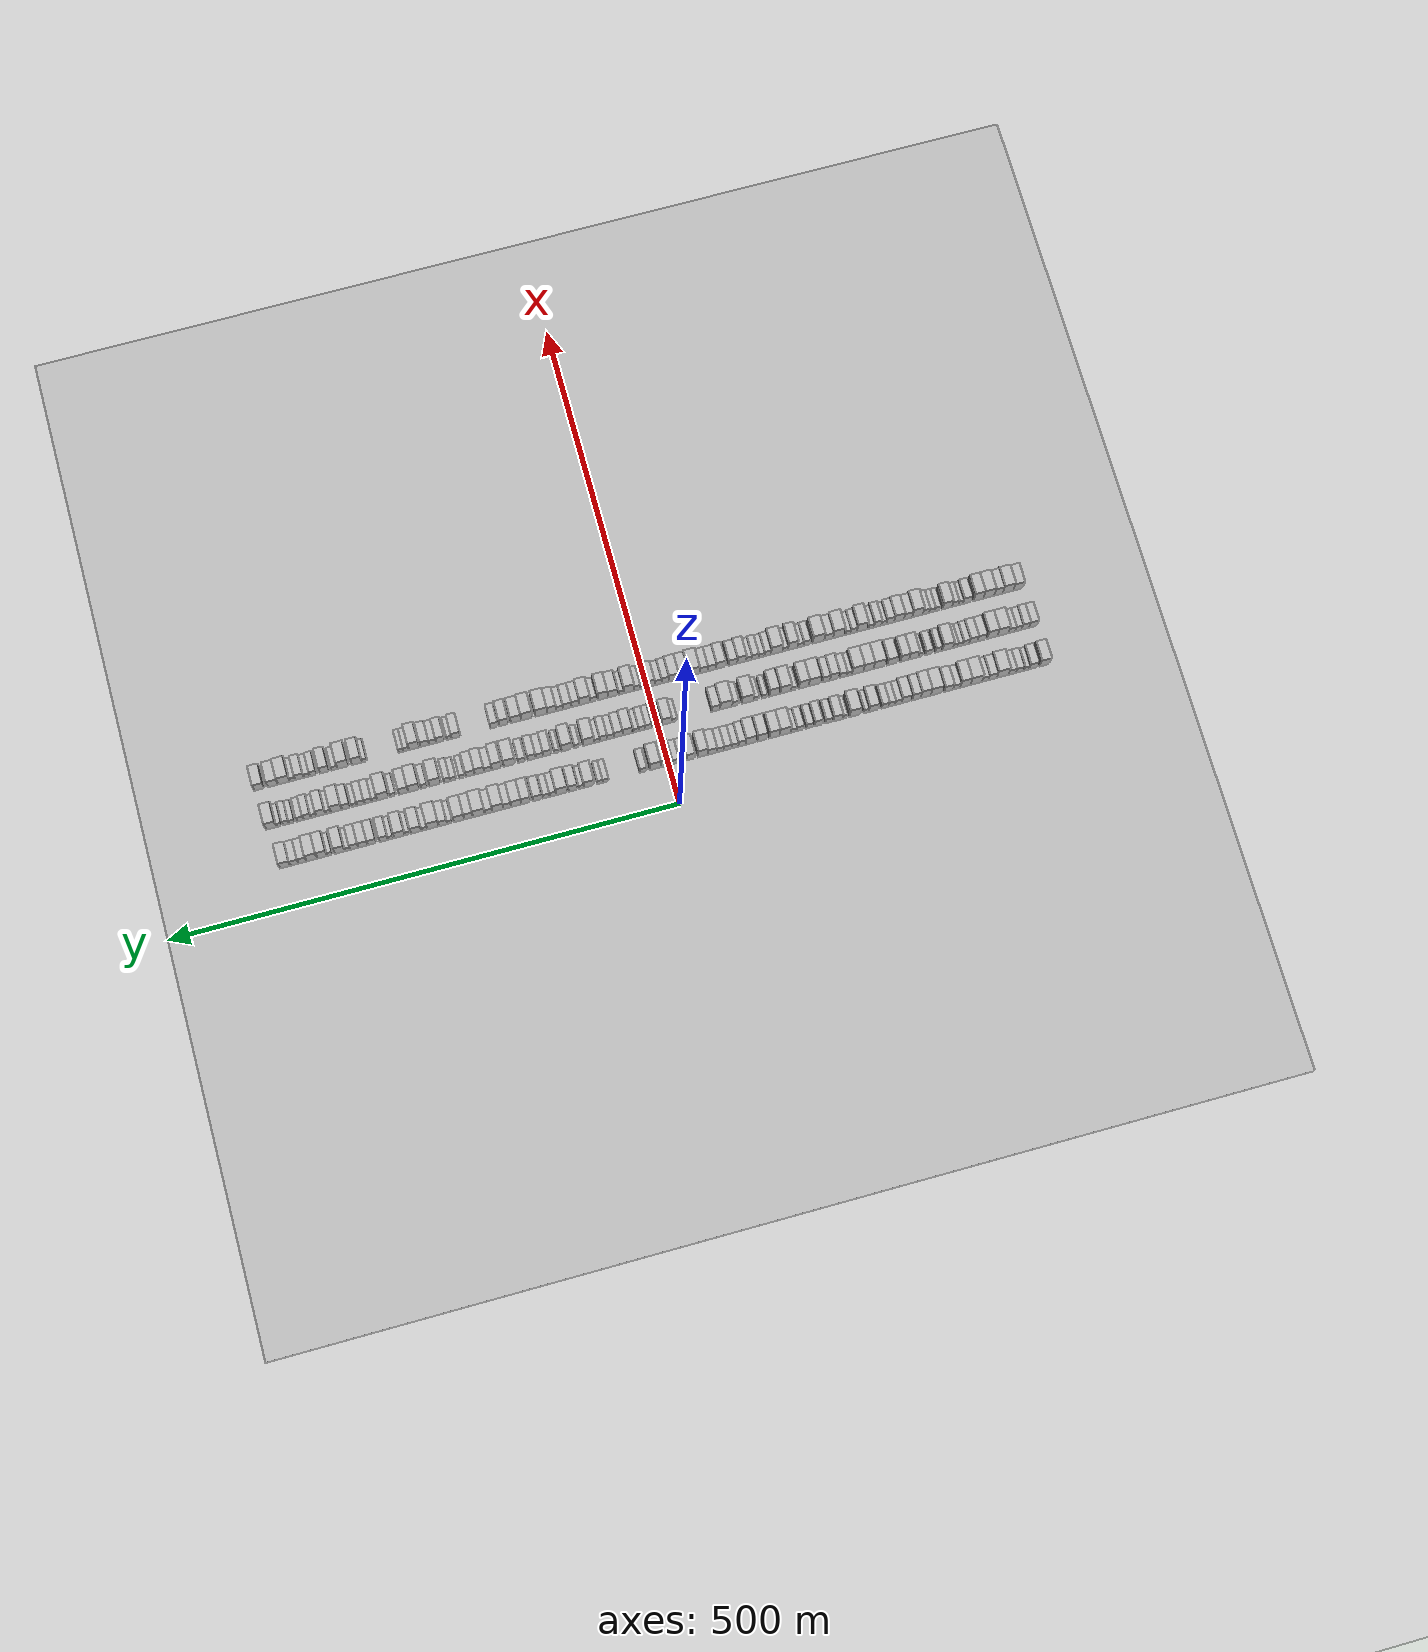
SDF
<?xml version="1.0" encoding="utf-8"?>

<sdf version="1.6">

   <world name="default">

      <gui fullscreen="0">

         <camera name="user_camera">

            <pose>-15 0 4.57585 0 0 0</pose>

            <view_controller>orbit</view_controller>

         </camera>

      </gui>

      <scene>

         <sky>

           <clouds>

             <speed>12</speed>

           </clouds>

         </sky>

         <ambient>0.4 0.4 0.4 1</ambient>

         <background>0.7 0.7 0.7 1</background>

         <shadows>1</shadows>

      </scene>

      <gravity>0 0 -9.8066</gravity>

      <magnetic_field>6e-06 2.3e-05 -4.2e-05</magnetic_field>

      <physics default="0" name="default_physics" type="ode">

         <ode>

            <solver>

               <type>quick</type>

               <iters>10</iters>

               <sor>1.0</sor>

               <use_dynamic_moi_rescaling>0</use_dynamic_moi_rescaling>

            </solver>

            <constraints>

               <cfm>0</cfm>

               <erp>0.2</erp>

               <contact_max_correcting_vel>100</contact_max_correcting_vel>

               <contact_surface_layer>0.001</contact_surface_layer>

            </constraints>

         </ode>

         <max_step_size>0.004</max_step_size>

         <real_time_factor>1</real_time_factor>

         <real_time_update_rate>250</real_time_update_rate>

      </physics>

      <light name="sun" type="directional">

         <cast_shadows>1</cast_shadows>

         <pose>0 0 10 0 0 0</pose>

         <diffuse>0.8 0.8 0.8 1</diffuse>

         <specular>0.2 0.2 0.2 1</specular>

         <attenuation>

            <range>1000</range>

            <constant>0.9</constant>

            <linear>0.01</linear>

            <quadratic>0.001</quadratic>

         </attenuation>

         <direction>-0.5 0.1 -0.9</direction>

      </light>

      <include>

         <name>ground_plane_1</name>

         <uri>model://HANNAS_ground_plane</uri>

         <pose>0 0 0  0 0 0</pose>

      </include>

      <include>

         <name>ground_plane_2</name>

         <uri>model://HANNAS_ground_plane</uri>

         <pose>100 0 0  0 0 0</pose>

      </include>

      <model name="building_1">

         <static>1</static>

         <pose frame="">50.0000 -375.0532 0 0.000000 0.000000 0.000000</pose>

         <link name="link">

            <pose frame="">0 0 10.50 0 0 0</pose>

            <collision name="collision">

               <geometry>

                  <box>

                     <size>20.0000 9.8936 21.0000</size>

                  </box>

               </geometry>

               <max_contacts>10</max_contacts>

               <surface>

                  <contact>

                     <ode/>

                  </contact>

                  <bounce/>

                  <friction>

                     <torsional>

                        <ode/>

                     </torsional>

                     <ode/>

                  </friction>

               </surface>

            </collision>

            <visual name="visual">

               <cast_shadows>0</cast_shadows>

               <geometry>

                  <box>

                     <size>20.0000 9.8936 21.0000</size>

                  </box>

               </geometry>

               <material>

                  <script>

                     <uri>model://HANNAS_wall/materials/scripts</uri>

                     <uri>model://HANNAS_wall/materials/textures</uri>

                     <name>vrc/HANNAS_wall</name>

                  </script>

               </material>

            </visual>

            <self_collide>0</self_collide>

            <enable_wind>0</enable_wind>

            <kinematic>0</kinematic>

         </link>

      </model>

      <model name="building_2">

         <static>1</static>

         <pose frame="">50.0000 -363.7577 0 0.000000 0.000000 0.000000</pose>

         <link name="link">

            <pose frame="">0 0 9.00 0 0 0</pose>

            <collision name="collision">

               <geometry>

                  <box>

                     <size>20.0000 8.6974 18.0000</size>

                  </box>

               </geometry>

               <max_contacts>10</max_contacts>

               <surface>

                  <contact>

                     <ode/>

                  </contact>

                  <bounce/>

                  <friction>

                     <torsional>

                        <ode/>

                     </torsional>

                     <ode/>

                  </friction>

               </surface>

            </collision>

            <visual name="visual">

               <cast_shadows>0</cast_shadows>

               <geometry>

                  <box>

                     <size>20.0000 8.6974 18.0000</size>

                  </box>

               </geometry>

               <material>

                  <script>

                     <uri>model://HANNAS_wall/materials/scripts</uri>

                     <uri>model://HANNAS_wall/materials/textures</uri>

                     <name>vrc/HANNAS_wall</name>

                  </script>

               </material>

            </visual>

            <self_collide>0</self_collide>

            <enable_wind>0</enable_wind>

            <kinematic>0</kinematic>

         </link>

      </model>

      <model name="building_3">

         <static>1</static>

         <pose frame="">50.0000 -356.9711 0 0.000000 0.000000 0.000000</pose>

         <link name="link">

            <pose frame="">0 0 6.00 0 0 0</pose>

            <collision name="collision">

               <geometry>

                  <box>

                     <size>20.0000 4.8758 12.0000</size>

                  </box>

               </geometry>

               <max_contacts>10</max_contacts>

               <surface>

                  <contact>

                     <ode/>

                  </contact>

                  <bounce/>

                  <friction>

                     <torsional>

                        <ode/>

                     </torsional>

                     <ode/>

                  </friction>

               </surface>

            </collision>

            <visual name="visual">

               <cast_shadows>0</cast_shadows>

               <geometry>

                  <box>

                     <size>20.0000 4.8758 12.0000</size>

                  </box>

               </geometry>

               <material>

                  <script>

                     <uri>model://HANNAS_wall/materials/scripts</uri>

                     <uri>model://HANNAS_wall/materials/textures</uri>

                     <name>vrc/HANNAS_wall</name>

                  </script>

               </material>

            </visual>

            <self_collide>0</self_collide>

            <enable_wind>0</enable_wind>

            <kinematic>0</kinematic>

         </link>

      </model>

      <model name="building_4">

         <static>1</static>

         <pose frame="">50.0000 -349.7861 0 0.000000 0.000000 0.000000</pose>

         <link name="link">

            <pose frame="">0 0 7.50 0 0 0</pose>

            <collision name="collision">

               <geometry>

                  <box>

                     <size>20.0000 7.4941 15.0000</size>

                  </box>

               </geometry>

               <max_contacts>10</max_contacts>

               <surface>

                  <contact>

                     <ode/>

                  </contact>

                  <bounce/>

                  <friction>

                     <torsional>

                        <ode/>

                     </torsional>

                     <ode/>

                  </friction>

               </surface>

            </collision>

            <visual name="visual">

               <cast_shadows>0</cast_shadows>

               <geometry>

                  <box>

                     <size>20.0000 7.4941 15.0000</size>

                  </box>

               </geometry>

               <material>

                  <script>

                     <uri>model://HANNAS_wall/materials/scripts</uri>

                     <uri>model://HANNAS_wall/materials/textures</uri>

                     <name>vrc/HANNAS_wall</name>

                  </script>

               </material>

            </visual>

            <self_collide>0</self_collide>

            <enable_wind>0</enable_wind>

            <kinematic>0</kinematic>

         </link>

      </model>

      <model name="building_5">

         <static>1</static>

         <pose frame="">50.0000 -342.3699 0 0.000000 0.000000 0.000000</pose>

         <link name="link">

            <pose frame="">0 0 7.50 0 0 0</pose>

            <collision name="collision">

               <geometry>

                  <box>

                     <size>20.0000 7.3385 15.0000</size>

                  </box>

               </geometry>

               <max_contacts>10</max_contacts>

               <surface>

                  <contact>

                     <ode/>

                  </contact>

                  <bounce/>

                  <friction>

                     <torsional>

                        <ode/>

                     </torsional>

                     <ode/>

                  </friction>

               </surface>

            </collision>

            <visual name="visual">

               <cast_shadows>0</cast_shadows>

               <geometry>

                  <box>

                     <size>20.0000 7.3385 15.0000</size>

                  </box>

               </geometry>

               <material>

                  <script>

                     <uri>model://HANNAS_wall/materials/scripts</uri>

                     <uri>model://HANNAS_wall/materials/textures</uri>

                     <name>vrc/HANNAS_wall</name>

                  </script>

               </material>

            </visual>

            <self_collide>0</self_collide>

            <enable_wind>0</enable_wind>

            <kinematic>0</kinematic>

         </link>

      </model>

      <model name="building_6">

         <static>1</static>

         <pose frame="">50.0000 -332.7374 0 0.000000 0.000000 0.000000</pose>

         <link name="link">

            <pose frame="">0 0 12.00 0 0 0</pose>

            <collision name="collision">

               <geometry>

                  <box>

                     <size>20.0000 11.9265 24.0000</size>

                  </box>

               </geometry>

               <max_contacts>10</max_contacts>

               <surface>

                  <contact>

                     <ode/>

                  </contact>

                  <bounce/>

                  <friction>

                     <torsional>

                        <ode/>

                     </torsional>

                     <ode/>

                  </friction>

               </surface>

            </collision>

            <visual name="visual">

               <cast_shadows>0</cast_shadows>

               <geometry>

                  <box>

                     <size>20.0000 11.9265 24.0000</size>

                  </box>

               </geometry>

               <material>

                  <script>

                     <uri>model://HANNAS_wall/materials/scripts</uri>

                     <uri>model://HANNAS_wall/materials/textures</uri>

                     <name>vrc/HANNAS_wall</name>

                  </script>

               </material>

            </visual>

            <self_collide>0</self_collide>

            <enable_wind>0</enable_wind>

            <kinematic>0</kinematic>

         </link>

      </model>

      <model name="building_7">

         <static>1</static>

         <pose frame="">50.0000 -322.6665 0 0.000000 0.000000 0.000000</pose>

         <link name="link">

            <pose frame="">0 0 9.00 0 0 0</pose>

            <collision name="collision">

               <geometry>

                  <box>

                     <size>20.0000 8.2152 18.0000</size>

                  </box>

               </geometry>

               <max_contacts>10</max_contacts>

               <surface>

                  <contact>

                     <ode/>

                  </contact>

                  <bounce/>

                  <friction>

                     <torsional>

                        <ode/>

                     </torsional>

                     <ode/>

                  </friction>

               </surface>

            </collision>

            <visual name="visual">

               <cast_shadows>0</cast_shadows>

               <geometry>

                  <box>

                     <size>20.0000 8.2152 18.0000</size>

                  </box>

               </geometry>

               <material>

                  <script>

                     <uri>model://HANNAS_wall/materials/scripts</uri>

                     <uri>model://HANNAS_wall/materials/textures</uri>

                     <name>vrc/HANNAS_wall</name>

                  </script>

               </material>

            </visual>

            <self_collide>0</self_collide>

            <enable_wind>0</enable_wind>

            <kinematic>0</kinematic>

         </link>

      </model>

      <model name="building_8">

         <static>1</static>

         <pose frame="">50.0000 -315.2555 0 0.000000 0.000000 0.000000</pose>

         <link name="link">

            <pose frame="">0 0 7.50 0 0 0</pose>

            <collision name="collision">

               <geometry>

                  <box>

                     <size>20.0000 6.6068 15.0000</size>

                  </box>

               </geometry>

               <max_contacts>10</max_contacts>

               <surface>

                  <contact>

                     <ode/>

                  </contact>

                  <bounce/>

                  <friction>

                     <torsional>

                        <ode/>

                     </torsional>

                     <ode/>

                  </friction>

               </surface>

            </collision>

            <visual name="visual">

               <cast_shadows>0</cast_shadows>

               <geometry>

                  <box>

                     <size>20.0000 6.6068 15.0000</size>

                  </box>

               </geometry>

               <material>

                  <script>

                     <uri>model://HANNAS_wall/materials/scripts</uri>

                     <uri>model://HANNAS_wall/materials/textures</uri>

                     <name>vrc/HANNAS_wall</name>

                  </script>

               </material>

            </visual>

            <self_collide>0</self_collide>

            <enable_wind>0</enable_wind>

            <kinematic>0</kinematic>

         </link>

      </model>

      <model name="building_9">

         <static>1</static>

         <pose frame="">50.0000 -306.0808 0 0.000000 0.000000 0.000000</pose>

         <link name="link">

            <pose frame="">0 0 12.00 0 0 0</pose>

            <collision name="collision">

               <geometry>

                  <box>

                     <size>20.0000 11.7427 24.0000</size>

                  </box>

               </geometry>

               <max_contacts>10</max_contacts>

               <surface>

                  <contact>

                     <ode/>

                  </contact>

                  <bounce/>

                  <friction>

                     <torsional>

                        <ode/>

                     </torsional>

                     <ode/>

                  </friction>

               </surface>

            </collision>

            <visual name="visual">

               <cast_shadows>0</cast_shadows>

               <geometry>

                  <box>

                     <size>20.0000 11.7427 24.0000</size>

                  </box>

               </geometry>

               <material>

                  <script>

                     <uri>model://HANNAS_wall/materials/scripts</uri>

                     <uri>model://HANNAS_wall/materials/textures</uri>

                     <name>vrc/HANNAS_wall</name>

                  </script>

               </material>

            </visual>

            <self_collide>0</self_collide>

            <enable_wind>0</enable_wind>

            <kinematic>0</kinematic>

         </link>

      </model>

      <model name="building_10">

         <static>1</static>

         <pose frame="">50.0000 -295.1318 0 0.000000 0.000000 0.000000</pose>

         <link name="link">

            <pose frame="">0 0 12.00 0 0 0</pose>

            <collision name="collision">

               <geometry>

                  <box>

                     <size>20.0000 10.1552 24.0000</size>

                  </box>

               </geometry>

               <max_contacts>10</max_contacts>

               <surface>

                  <contact>

                     <ode/>

                  </contact>

                  <bounce/>

                  <friction>

                     <torsional>

                        <ode/>

                     </torsional>

                     <ode/>

                  </friction>

               </surface>

            </collision>

            <visual name="visual">

               <cast_shadows>0</cast_shadows>

               <geometry>

                  <box>

                     <size>20.0000 10.1552 24.0000</size>

                  </box>

               </geometry>

               <material>

                  <script>

                     <uri>model://HANNAS_wall/materials/scripts</uri>

                     <uri>model://HANNAS_wall/materials/textures</uri>

                     <name>vrc/HANNAS_wall</name>

                  </script>

               </material>

            </visual>

            <self_collide>0</self_collide>

            <enable_wind>0</enable_wind>

            <kinematic>0</kinematic>

         </link>

      </model>

      <model name="building_11">

         <static>1</static>

         <pose frame="">50.0000 -286.5284 0 0.000000 0.000000 0.000000</pose>

         <link name="link">

            <pose frame="">0 0 7.50 0 0 0</pose>

            <collision name="collision">

               <geometry>

                  <box>

                     <size>20.0000 7.0517 15.0000</size>

                  </box>

               </geometry>

               <max_contacts>10</max_contacts>

               <surface>

                  <contact>

                     <ode/>

                  </contact>

                  <bounce/>

                  <friction>

                     <torsional>

                        <ode/>

                     </torsional>

                     <ode/>

                  </friction>

               </surface>

            </collision>

            <visual name="visual">

               <cast_shadows>0</cast_shadows>

               <geometry>

                  <box>

                     <size>20.0000 7.0517 15.0000</size>

                  </box>

               </geometry>

               <material>

                  <script>

                     <uri>model://HANNAS_wall/materials/scripts</uri>

                     <uri>model://HANNAS_wall/materials/textures</uri>

                     <name>vrc/HANNAS_wall</name>

                  </script>

               </material>

            </visual>

            <self_collide>0</self_collide>

            <enable_wind>0</enable_wind>

            <kinematic>0</kinematic>

         </link>

      </model>

      <model name="building_12">

         <static>1</static>

         <pose frame="">50.0000 -278.5229 0 0.000000 0.000000 0.000000</pose>

         <link name="link">

            <pose frame="">0 0 9.00 0 0 0</pose>

            <collision name="collision">

               <geometry>

                  <box>

                     <size>20.0000 8.9593 18.0000</size>

                  </box>

               </geometry>

               <max_contacts>10</max_contacts>

               <surface>

                  <contact>

                     <ode/>

                  </contact>

                  <bounce/>

                  <friction>

                     <torsional>

                        <ode/>

                     </torsional>

                     <ode/>

                  </friction>

               </surface>

            </collision>

            <visual name="visual">

               <cast_shadows>0</cast_shadows>

               <geometry>

                  <box>

                     <size>20.0000 8.9593 18.0000</size>

                  </box>

               </geometry>

               <material>

                  <script>

                     <uri>model://HANNAS_wall/materials/scripts</uri>

                     <uri>model://HANNAS_wall/materials/textures</uri>

                     <name>vrc/HANNAS_wall</name>

                  </script>

               </material>

            </visual>

            <self_collide>0</self_collide>

            <enable_wind>0</enable_wind>

            <kinematic>0</kinematic>

         </link>

      </model>

      <model name="building_13">

         <static>1</static>

         <pose frame="">50.0000 -266.1553 0 0.000000 0.000000 0.000000</pose>

         <link name="link">

            <pose frame="">0 0 12.00 0 0 0</pose>

            <collision name="collision">

               <geometry>

                  <box>

                     <size>20.0000 11.7759 24.0000</size>

                  </box>

               </geometry>

               <max_contacts>10</max_contacts>

               <surface>

                  <contact>

                     <ode/>

                  </contact>

                  <bounce/>

                  <friction>

                     <torsional>

                        <ode/>

                     </torsional>

                     <ode/>

                  </friction>

               </surface>

            </collision>

            <visual name="visual">

               <cast_shadows>0</cast_shadows>

               <geometry>

                  <box>

                     <size>20.0000 11.7759 24.0000</size>

                  </box>

               </geometry>

               <material>

                  <script>

                     <uri>model://HANNAS_wall/materials/scripts</uri>

                     <uri>model://HANNAS_wall/materials/textures</uri>

                     <name>vrc/HANNAS_wall</name>

                  </script>

               </material>

            </visual>

            <self_collide>0</self_collide>

            <enable_wind>0</enable_wind>

            <kinematic>0</kinematic>

         </link>

      </model>

      <model name="building_14">

         <static>1</static>

         <pose frame="">50.0000 -255.2726 0 0.000000 0.000000 0.000000</pose>

         <link name="link">

            <pose frame="">0 0 12.00 0 0 0</pose>

            <collision name="collision">

               <geometry>

                  <box>

                     <size>20.0000 9.9895 24.0000</size>

                  </box>

               </geometry>

               <max_contacts>10</max_contacts>

               <surface>

                  <contact>

                     <ode/>

                  </contact>

                  <bounce/>

                  <friction>

                     <torsional>

                        <ode/>

                     </torsional>

                     <ode/>

                  </friction>

               </surface>

            </collision>

            <visual name="visual">

               <cast_shadows>0</cast_shadows>

               <geometry>

                  <box>

                     <size>20.0000 9.9895 24.0000</size>

                  </box>

               </geometry>

               <material>

                  <script>

                     <uri>model://HANNAS_wall/materials/scripts</uri>

                     <uri>model://HANNAS_wall/materials/textures</uri>

                     <name>vrc/HANNAS_wall</name>

                  </script>

               </material>

            </visual>

            <self_collide>0</self_collide>

            <enable_wind>0</enable_wind>

            <kinematic>0</kinematic>

         </link>

      </model>

      <model name="building_15">

         <static>1</static>

         <pose frame="">50.0000 -246.0600 0 0.000000 0.000000 0.000000</pose>

         <link name="link">

            <pose frame="">0 0 10.50 0 0 0</pose>

            <collision name="collision">

               <geometry>

                  <box>

                     <size>20.0000 8.4355 21.0000</size>

                  </box>

               </geometry>

               <max_contacts>10</max_contacts>

               <surface>

                  <contact>

                     <ode/>

                  </contact>

                  <bounce/>

                  <friction>

                     <torsional>

                        <ode/>

                     </torsional>

                     <ode/>

                  </friction>

               </surface>

            </collision>

            <visual name="visual">

               <cast_shadows>0</cast_shadows>

               <geometry>

                  <box>

                     <size>20.0000 8.4355 21.0000</size>

                  </box>

               </geometry>

               <material>

                  <script>

                     <uri>model://HANNAS_wall/materials/scripts</uri>

                     <uri>model://HANNAS_wall/materials/textures</uri>

                     <name>vrc/HANNAS_wall</name>

                  </script>

               </material>

            </visual>

            <self_collide>0</self_collide>

            <enable_wind>0</enable_wind>

            <kinematic>0</kinematic>

         </link>

      </model>

      <model name="building_16">

         <static>1</static>

         <pose frame="">50.0000 -235.9735 0 0.000000 0.000000 0.000000</pose>

         <link name="link">

            <pose frame="">0 0 10.50 0 0 0</pose>

            <collision name="collision">

               <geometry>

                  <box>

                     <size>20.0000 9.7375 21.0000</size>

                  </box>

               </geometry>

               <max_contacts>10</max_contacts>

               <surface>

                  <contact>

                     <ode/>

                  </contact>

                  <bounce/>

                  <friction>

                     <torsional>

                        <ode/>

                     </torsional>

                     <ode/>

                  </friction>

               </surface>

            </collision>

            <visual name="visual">

               <cast_shadows>0</cast_shadows>

               <geometry>

                  <box>

                     <size>20.0000 9.7375 21.0000</size>

                  </box>

               </geometry>

               <material>

                  <script>

                     <uri>model://HANNAS_wall/materials/scripts</uri>

                     <uri>model://HANNAS_wall/materials/textures</uri>

                     <name>vrc/HANNAS_wall</name>

                  </script>

               </material>

            </visual>

            <self_collide>0</self_collide>

            <enable_wind>0</enable_wind>

            <kinematic>0</kinematic>

         </link>

      </model>

      <model name="building_17">

         <static>1</static>

         <pose frame="">50.0000 -227.8595 0 0.000000 0.000000 0.000000</pose>

         <link name="link">

            <pose frame="">0 0 7.50 0 0 0</pose>

            <collision name="collision">

               <geometry>

                  <box>

                     <size>20.0000 6.4905 15.0000</size>

                  </box>

               </geometry>

               <max_contacts>10</max_contacts>

               <surface>

                  <contact>

                     <ode/>

                  </contact>

                  <bounce/>

                  <friction>

                     <torsional>

                        <ode/>

                     </torsional>

                     <ode/>

                  </friction>

               </surface>

            </collision>

            <visual name="visual">

               <cast_shadows>0</cast_shadows>

               <geometry>

                  <box>

                     <size>20.0000 6.4905 15.0000</size>

                  </box>

               </geometry>

               <material>

                  <script>

                     <uri>model://HANNAS_wall/materials/scripts</uri>

                     <uri>model://HANNAS_wall/materials/textures</uri>

                     <name>vrc/HANNAS_wall</name>

                  </script>

               </material>

            </visual>

            <self_collide>0</self_collide>

            <enable_wind>0</enable_wind>

            <kinematic>0</kinematic>

         </link>

      </model>

      <model name="building_18">

         <static>1</static>

         <pose frame="">50.0000 -221.5160 0 0.000000 0.000000 0.000000</pose>

         <link name="link">

            <pose frame="">0 0 7.50 0 0 0</pose>

            <collision name="collision">

               <geometry>

                  <box>

                     <size>20.0000 6.1965 15.0000</size>

                  </box>

               </geometry>

               <max_contacts>10</max_contacts>

               <surface>

                  <contact>

                     <ode/>

                  </contact>

                  <bounce/>

                  <friction>

                     <torsional>

                        <ode/>

                     </torsional>

                     <ode/>

                  </friction>

               </surface>

            </collision>

            <visual name="visual">

               <cast_shadows>0</cast_shadows>

               <geometry>

                  <box>

                     <size>20.0000 6.1965 15.0000</size>

                  </box>

               </geometry>

               <material>

                  <script>

                     <uri>model://HANNAS_wall/materials/scripts</uri>

                     <uri>model://HANNAS_wall/materials/textures</uri>

                     <name>vrc/HANNAS_wall</name>

                  </script>

               </material>

            </visual>

            <self_collide>0</self_collide>

            <enable_wind>0</enable_wind>

            <kinematic>0</kinematic>

         </link>

      </model>

      <model name="building_19">

         <static>1</static>

         <pose frame="">50.0000 -214.8344 0 0.000000 0.000000 0.000000</pose>

         <link name="link">

            <pose frame="">0 0 7.50 0 0 0</pose>

            <collision name="collision">

               <geometry>

                  <box>

                     <size>20.0000 7.1667 15.0000</size>

                  </box>

               </geometry>

               <max_contacts>10</max_contacts>

               <surface>

                  <contact>

                     <ode/>

                  </contact>

                  <bounce/>

                  <friction>

                     <torsional>

                        <ode/>

                     </torsional>

                     <ode/>

                  </friction>

               </surface>

            </collision>

            <visual name="visual">

               <cast_shadows>0</cast_shadows>

               <geometry>

                  <box>

                     <size>20.0000 7.1667 15.0000</size>

                  </box>

               </geometry>

               <material>

                  <script>

                     <uri>model://HANNAS_wall/materials/scripts</uri>

                     <uri>model://HANNAS_wall/materials/textures</uri>

                     <name>vrc/HANNAS_wall</name>

                  </script>

               </material>

            </visual>

            <self_collide>0</self_collide>

            <enable_wind>0</enable_wind>

            <kinematic>0</kinematic>

         </link>

      </model>

      <model name="building_20">

         <static>1</static>

         <pose frame="">50.0000 -203.2203 0 0.000000 0.000000 0.000000</pose>

         <link name="link">

            <pose frame="">0 0 10.50 0 0 0</pose>

            <collision name="collision">

               <geometry>

                  <box>

                     <size>20.0000 10.0615 21.0000</size>

                  </box>

               </geometry>

               <max_contacts>10</max_contacts>

               <surface>

                  <contact>

                     <ode/>

                  </contact>

                  <bounce/>

                  <friction>

                     <torsional>

                        <ode/>

                     </torsional>

                     <ode/>

                  </friction>

               </surface>

            </collision>

            <visual name="visual">

               <cast_shadows>0</cast_shadows>

               <geometry>

                  <box>

                     <size>20.0000 10.0615 21.0000</size>

                  </box>

               </geometry>

               <material>

                  <script>

                     <uri>model://HANNAS_wall/materials/scripts</uri>

                     <uri>model://HANNAS_wall/materials/textures</uri>

                     <name>vrc/HANNAS_wall</name>

                  </script>

               </material>

            </visual>

            <self_collide>0</self_collide>

            <enable_wind>0</enable_wind>

            <kinematic>0</kinematic>

         </link>

      </model>

      <model name="building_21">

         <static>1</static>

         <pose frame="">50.0000 -195.7574 0 0.000000 0.000000 0.000000</pose>

         <link name="link">

            <pose frame="">0 0 6.00 0 0 0</pose>

            <collision name="collision">

               <geometry>

                  <box>

                     <size>20.0000 4.8642 12.0000</size>

                  </box>

               </geometry>

               <max_contacts>10</max_contacts>

               <surface>

                  <contact>

                     <ode/>

                  </contact>

                  <bounce/>

                  <friction>

                     <torsional>

                        <ode/>

                     </torsional>

                     <ode/>

                  </friction>

               </surface>

            </collision>

            <visual name="visual">

               <cast_shadows>0</cast_shadows>

               <geometry>

                  <box>

                     <size>20.0000 4.8642 12.0000</size>

                  </box>

               </geometry>

               <material>

                  <script>

                     <uri>model://HANNAS_wall/materials/scripts</uri>

                     <uri>model://HANNAS_wall/materials/textures</uri>

                     <name>vrc/HANNAS_wall</name>

                  </script>

               </material>

            </visual>

            <self_collide>0</self_collide>

            <enable_wind>0</enable_wind>

            <kinematic>0</kinematic>

         </link>

      </model>

      <model name="building_22">

         <static>1</static>

         <pose frame="">50.0000 -184.6123 0 0.000000 0.000000 0.000000</pose>

         <link name="link">

            <pose frame="">0 0 12.00 0 0 0</pose>

            <collision name="collision">

               <geometry>

                  <box>

                     <size>20.0000 11.4262 24.0000</size>

                  </box>

               </geometry>

               <max_contacts>10</max_contacts>

               <surface>

                  <contact>

                     <ode/>

                  </contact>

                  <bounce/>

                  <friction>

                     <torsional>

                        <ode/>

                     </torsional>

                     <ode/>

                  </friction>

               </surface>

            </collision>

            <visual name="visual">

               <cast_shadows>0</cast_shadows>

               <geometry>

                  <box>

                     <size>20.0000 11.4262 24.0000</size>

                  </box>

               </geometry>

               <material>

                  <script>

                     <uri>model://HANNAS_wall/materials/scripts</uri>

                     <uri>model://HANNAS_wall/materials/textures</uri>

                     <name>vrc/HANNAS_wall</name>

                  </script>

               </material>

            </visual>

            <self_collide>0</self_collide>

            <enable_wind>0</enable_wind>

            <kinematic>0</kinematic>

         </link>

      </model>

      <model name="building_23">

         <static>1</static>

         <pose frame="">50.0000 -174.4411 0 0.000000 0.000000 0.000000</pose>

         <link name="link">

            <pose frame="">0 0 6.00 0 0 0</pose>

            <collision name="collision">

               <geometry>

                  <box>

                     <size>20.0000 4.9161 12.0000</size>

                  </box>

               </geometry>

               <max_contacts>10</max_contacts>

               <surface>

                  <contact>

                     <ode/>

                  </contact>

                  <bounce/>

                  <friction>

                     <torsional>

                        <ode/>

                     </torsional>

                     <ode/>

                  </friction>

               </surface>

            </collision>

            <visual name="visual">

               <cast_shadows>0</cast_shadows>

               <geometry>

                  <box>

                     <size>20.0000 4.9161 12.0000</size>

                  </box>

               </geometry>

               <material>

                  <script>

                     <uri>model://HANNAS_wall/materials/scripts</uri>

                     <uri>model://HANNAS_wall/materials/textures</uri>

                     <name>vrc/HANNAS_wall</name>

                  </script>

               </material>

            </visual>

            <self_collide>0</self_collide>

            <enable_wind>0</enable_wind>

            <kinematic>0</kinematic>

         </link>

      </model>

      <model name="building_24">

         <static>1</static>

         <pose frame="">50.0000 -167.5438 0 0.000000 0.000000 0.000000</pose>

         <link name="link">

            <pose frame="">0 0 9.00 0 0 0</pose>

            <collision name="collision">

               <geometry>

                  <box>

                     <size>20.0000 8.8785 18.0000</size>

                  </box>

               </geometry>

               <max_contacts>10</max_contacts>

               <surface>

                  <contact>

                     <ode/>

                  </contact>

                  <bounce/>

                  <friction>

                     <torsional>

                        <ode/>

                     </torsional>

                     <ode/>

                  </friction>

               </surface>

            </collision>

            <visual name="visual">

               <cast_shadows>0</cast_shadows>

               <geometry>

                  <box>

                     <size>20.0000 8.8785 18.0000</size>

                  </box>

               </geometry>

               <material>

                  <script>

                     <uri>model://HANNAS_wall/materials/scripts</uri>

                     <uri>model://HANNAS_wall/materials/textures</uri>

                     <name>vrc/HANNAS_wall</name>

                  </script>

               </material>

            </visual>

            <self_collide>0</self_collide>

            <enable_wind>0</enable_wind>

            <kinematic>0</kinematic>

         </link>

      </model>

      <model name="building_25">

         <static>1</static>

         <pose frame="">50.0000 -158.5527 0 0.000000 0.000000 0.000000</pose>

         <link name="link">

            <pose frame="">0 0 7.50 0 0 0</pose>

            <collision name="collision">

               <geometry>

                  <box>

                     <size>20.0000 7.1037 15.0000</size>

                  </box>

               </geometry>

               <max_contacts>10</max_contacts>

               <surface>

                  <contact>

                     <ode/>

                  </contact>

                  <bounce/>

                  <friction>

                     <torsional>

                        <ode/>

                     </torsional>

                     <ode/>

                  </friction>

               </surface>

            </collision>

            <visual name="visual">

               <cast_shadows>0</cast_shadows>

               <geometry>

                  <box>

                     <size>20.0000 7.1037 15.0000</size>

                  </box>

               </geometry>

               <material>

                  <script>

                     <uri>model://HANNAS_wall/materials/scripts</uri>

                     <uri>model://HANNAS_wall/materials/textures</uri>

                     <name>vrc/HANNAS_wall</name>

                  </script>

               </material>

            </visual>

            <self_collide>0</self_collide>

            <enable_wind>0</enable_wind>

            <kinematic>0</kinematic>

         </link>

      </model>

      <model name="building_26">

         <static>1</static>

         <pose frame="">50.0000 -148.0391 0 0.000000 0.000000 0.000000</pose>

         <link name="link">

            <pose frame="">0 0 9.00 0 0 0</pose>

            <collision name="collision">

               <geometry>

                  <box>

                     <size>20.0000 7.9235 18.0000</size>

                  </box>

               </geometry>

               <max_contacts>10</max_contacts>

               <surface>

                  <contact>

                     <ode/>

                  </contact>

                  <bounce/>

                  <friction>

                     <torsional>

                        <ode/>

                     </torsional>

                     <ode/>

                  </friction>

               </surface>

            </collision>

            <visual name="visual">

               <cast_shadows>0</cast_shadows>

               <geometry>

                  <box>

                     <size>20.0000 7.9235 18.0000</size>

                  </box>

               </geometry>

               <material>

                  <script>

                     <uri>model://HANNAS_wall/materials/scripts</uri>

                     <uri>model://HANNAS_wall/materials/textures</uri>

                     <name>vrc/HANNAS_wall</name>

                  </script>

               </material>

            </visual>

            <self_collide>0</self_collide>

            <enable_wind>0</enable_wind>

            <kinematic>0</kinematic>

         </link>

      </model>

      <model name="building_27">

         <static>1</static>

         <pose frame="">50.0000 -139.3823 0 0.000000 0.000000 0.000000</pose>

         <link name="link">

            <pose frame="">0 0 7.50 0 0 0</pose>

            <collision name="collision">

               <geometry>

                  <box>

                     <size>20.0000 7.3902 15.0000</size>

                  </box>

               </geometry>

               <max_contacts>10</max_contacts>

               <surface>

                  <contact>

                     <ode/>

                  </contact>

                  <bounce/>

                  <friction>

                     <torsional>

                        <ode/>

                     </torsional>

                     <ode/>

                  </friction>

               </surface>

            </collision>

            <visual name="visual">

               <cast_shadows>0</cast_shadows>

               <geometry>

                  <box>

                     <size>20.0000 7.3902 15.0000</size>

                  </box>

               </geometry>

               <material>

                  <script>

                     <uri>model://HANNAS_wall/materials/scripts</uri>

                     <uri>model://HANNAS_wall/materials/textures</uri>

                     <name>vrc/HANNAS_wall</name>

                  </script>

               </material>

            </visual>

            <self_collide>0</self_collide>

            <enable_wind>0</enable_wind>

            <kinematic>0</kinematic>

         </link>

      </model>

      <model name="building_28">

         <static>1</static>

         <pose frame="">50.0000 -129.9961 0 0.000000 0.000000 0.000000</pose>

         <link name="link">

            <pose frame="">0 0 7.50 0 0 0</pose>

            <collision name="collision">

               <geometry>

                  <box>

                     <size>20.0000 7.3821 15.0000</size>

                  </box>

               </geometry>

               <max_contacts>10</max_contacts>

               <surface>

                  <contact>

                     <ode/>

                  </contact>

                  <bounce/>

                  <friction>

                     <torsional>

                        <ode/>

                     </torsional>

                     <ode/>

                  </friction>

               </surface>

            </collision>

            <visual name="visual">

               <cast_shadows>0</cast_shadows>

               <geometry>

                  <box>

                     <size>20.0000 7.3821 15.0000</size>

                  </box>

               </geometry>

               <material>

                  <script>

                     <uri>model://HANNAS_wall/materials/scripts</uri>

                     <uri>model://HANNAS_wall/materials/textures</uri>

                     <name>vrc/HANNAS_wall</name>

                  </script>

               </material>

            </visual>

            <self_collide>0</self_collide>

            <enable_wind>0</enable_wind>

            <kinematic>0</kinematic>

         </link>

      </model>

      <model name="building_29">

         <static>1</static>

         <pose frame="">50.0000 -123.3949 0 0.000000 0.000000 0.000000</pose>

         <link name="link">

            <pose frame="">0 0 6.00 0 0 0</pose>

            <collision name="collision">

               <geometry>

                  <box>

                     <size>20.0000 5.8202 12.0000</size>

                  </box>

               </geometry>

               <max_contacts>10</max_contacts>

               <surface>

                  <contact>

                     <ode/>

                  </contact>

                  <bounce/>

                  <friction>

                     <torsional>

                        <ode/>

                     </torsional>

                     <ode/>

                  </friction>

               </surface>

            </collision>

            <visual name="visual">

               <cast_shadows>0</cast_shadows>

               <geometry>

                  <box>

                     <size>20.0000 5.8202 12.0000</size>

                  </box>

               </geometry>

               <material>

                  <script>

                     <uri>model://HANNAS_wall/materials/scripts</uri>

                     <uri>model://HANNAS_wall/materials/textures</uri>

                     <name>vrc/HANNAS_wall</name>

                  </script>

               </material>

            </visual>

            <self_collide>0</self_collide>

            <enable_wind>0</enable_wind>

            <kinematic>0</kinematic>

         </link>

      </model>

      <model name="building_30">

         <static>1</static>

         <pose frame="">50.0000 -114.9173 0 0.000000 0.000000 0.000000</pose>

         <link name="link">

            <pose frame="">0 0 12.00 0 0 0</pose>

            <collision name="collision">

               <geometry>

                  <box>

                     <size>20.0000 11.1349 24.0000</size>

                  </box>

               </geometry>

               <max_contacts>10</max_contacts>

               <surface>

                  <contact>

                     <ode/>

                  </contact>

                  <bounce/>

                  <friction>

                     <torsional>

                        <ode/>

                     </torsional>

                     <ode/>

                  </friction>

               </surface>

            </collision>

            <visual name="visual">

               <cast_shadows>0</cast_shadows>

               <geometry>

                  <box>

                     <size>20.0000 11.1349 24.0000</size>

                  </box>

               </geometry>

               <material>

                  <script>

                     <uri>model://HANNAS_wall/materials/scripts</uri>

                     <uri>model://HANNAS_wall/materials/textures</uri>

                     <name>vrc/HANNAS_wall</name>

                  </script>

               </material>

            </visual>

            <self_collide>0</self_collide>

            <enable_wind>0</enable_wind>

            <kinematic>0</kinematic>

         </link>

      </model>

      <model name="building_31">

         <static>1</static>

         <pose frame="">50.0000 -104.2177 0 0.000000 0.000000 0.000000</pose>

         <link name="link">

            <pose frame="">0 0 12.00 0 0 0</pose>

            <collision name="collision">

               <geometry>

                  <box>

                     <size>20.0000 10.2643 24.0000</size>

                  </box>

               </geometry>

               <max_contacts>10</max_contacts>

               <surface>

                  <contact>

                     <ode/>

                  </contact>

                  <bounce/>

                  <friction>

                     <torsional>

                        <ode/>

                     </torsional>

                     <ode/>

                  </friction>

               </surface>

            </collision>

            <visual name="visual">

               <cast_shadows>0</cast_shadows>

               <geometry>

                  <box>

                     <size>20.0000 10.2643 24.0000</size>

                  </box>

               </geometry>

               <material>

                  <script>

                     <uri>model://HANNAS_wall/materials/scripts</uri>

                     <uri>model://HANNAS_wall/materials/textures</uri>

                     <name>vrc/HANNAS_wall</name>

                  </script>

               </material>

            </visual>

            <self_collide>0</self_collide>

            <enable_wind>0</enable_wind>

            <kinematic>0</kinematic>

         </link>

      </model>

      <model name="building_32">

         <static>1</static>

         <pose frame="">50.0000 -92.1554 0 0.000000 0.000000 0.000000</pose>

         <link name="link">

            <pose frame="">0 0 12.00 0 0 0</pose>

            <collision name="collision">

               <geometry>

                  <box>

                     <size>20.0000 9.8602 24.0000</size>

                  </box>

               </geometry>

               <max_contacts>10</max_contacts>

               <surface>

                  <contact>

                     <ode/>

                  </contact>

                  <bounce/>

                  <friction>

                     <torsional>

                        <ode/>

                     </torsional>

                     <ode/>

                  </friction>

               </surface>

            </collision>

            <visual name="visual">

               <cast_shadows>0</cast_shadows>

               <geometry>

                  <box>

                     <size>20.0000 9.8602 24.0000</size>

                  </box>

               </geometry>

               <material>

                  <script>

                     <uri>model://HANNAS_wall/materials/scripts</uri>

                     <uri>model://HANNAS_wall/materials/textures</uri>

                     <name>vrc/HANNAS_wall</name>

                  </script>

               </material>

            </visual>

            <self_collide>0</self_collide>

            <enable_wind>0</enable_wind>

            <kinematic>0</kinematic>

         </link>

      </model>

      <model name="building_33">

         <static>1</static>

         <pose frame="">50.0000 -80.8316 0 0.000000 0.000000 0.000000</pose>

         <link name="link">

            <pose frame="">0 0 12.00 0 0 0</pose>

            <collision name="collision">

               <geometry>

                  <box>

                     <size>20.0000 10.7874 24.0000</size>

                  </box>

               </geometry>

               <max_contacts>10</max_contacts>

               <surface>

                  <contact>

                     <ode/>

                  </contact>

                  <bounce/>

                  <friction>

                     <torsional>

                        <ode/>

                     </torsional>

                     <ode/>

                  </friction>

               </surface>

            </collision>

            <visual name="visual">

               <cast_shadows>0</cast_shadows>

               <geometry>

                  <box>

                     <size>20.0000 10.7874 24.0000</size>

                  </box>

               </geometry>

               <material>

                  <script>

                     <uri>model://HANNAS_wall/materials/scripts</uri>

                     <uri>model://HANNAS_wall/materials/textures</uri>

                     <name>vrc/HANNAS_wall</name>

                  </script>

               </material>

            </visual>

            <self_collide>0</self_collide>

            <enable_wind>0</enable_wind>

            <kinematic>0</kinematic>

         </link>

      </model>

      <model name="building_34">

         <static>1</static>

         <pose frame="">50.0000 -71.7479 0 0.000000 0.000000 0.000000</pose>

         <link name="link">

            <pose frame="">0 0 9.00 0 0 0</pose>

            <collision name="collision">

               <geometry>

                  <box>

                     <size>20.0000 7.3801 18.0000</size>

                  </box>

               </geometry>

               <max_contacts>10</max_contacts>

               <surface>

                  <contact>

                     <ode/>

                  </contact>

                  <bounce/>

                  <friction>

                     <torsional>

                        <ode/>

                     </torsional>

                     <ode/>

                  </friction>

               </surface>

            </collision>

            <visual name="visual">

               <cast_shadows>0</cast_shadows>

               <geometry>

                  <box>

                     <size>20.0000 7.3801 18.0000</size>

                  </box>

               </geometry>

               <material>

                  <script>

                     <uri>model://HANNAS_wall/materials/scripts</uri>

                     <uri>model://HANNAS_wall/materials/textures</uri>

                     <name>vrc/HANNAS_wall</name>

                  </script>

               </material>

            </visual>

            <self_collide>0</self_collide>

            <enable_wind>0</enable_wind>

            <kinematic>0</kinematic>

         </link>

      </model>

      <model name="building_35">

         <static>1</static>

         <pose frame="">50.0000 -64.7169 0 0.000000 0.000000 0.000000</pose>

         <link name="link">

            <pose frame="">0 0 7.50 0 0 0</pose>

            <collision name="collision">

               <geometry>

                  <box>

                     <size>20.0000 6.6818 15.0000</size>

                  </box>

               </geometry>

               <max_contacts>10</max_contacts>

               <surface>

                  <contact>

                     <ode/>

                  </contact>

                  <bounce/>

                  <friction>

                     <torsional>

                        <ode/>

                     </torsional>

                     <ode/>

                  </friction>

               </surface>

            </collision>

            <visual name="visual">

               <cast_shadows>0</cast_shadows>

               <geometry>

                  <box>

                     <size>20.0000 6.6818 15.0000</size>

                  </box>

               </geometry>

               <material>

                  <script>

                     <uri>model://HANNAS_wall/materials/scripts</uri>

                     <uri>model://HANNAS_wall/materials/textures</uri>

                     <name>vrc/HANNAS_wall</name>

                  </script>

               </material>

            </visual>

            <self_collide>0</self_collide>

            <enable_wind>0</enable_wind>

            <kinematic>0</kinematic>

         </link>

      </model>

      <model name="building_36">

         <static>1</static>

         <pose frame="">50.0000 -57.6515 0 0.000000 0.000000 0.000000</pose>

         <link name="link">

            <pose frame="">0 0 7.50 0 0 0</pose>

            <collision name="collision">

               <geometry>

                  <box>

                     <size>20.0000 7.4490 15.0000</size>

                  </box>

               </geometry>

               <max_contacts>10</max_contacts>

               <surface>

                  <contact>

                     <ode/>

                  </contact>

                  <bounce/>

                  <friction>

                     <torsional>

                        <ode/>

                     </torsional>

                     <ode/>

                  </friction>

               </surface>

            </collision>

            <visual name="visual">

               <cast_shadows>0</cast_shadows>

               <geometry>

                  <box>

                     <size>20.0000 7.4490 15.0000</size>

                  </box>

               </geometry>

               <material>

                  <script>

                     <uri>model://HANNAS_wall/materials/scripts</uri>

                     <uri>model://HANNAS_wall/materials/textures</uri>

                     <name>vrc/HANNAS_wall</name>

                  </script>

               </material>

            </visual>

            <self_collide>0</self_collide>

            <enable_wind>0</enable_wind>

            <kinematic>0</kinematic>

         </link>

      </model>

      <model name="building_37">

         <static>1</static>

         <pose frame="">50.0000 -50.4087 0 0.000000 0.000000 0.000000</pose>

         <link name="link">

            <pose frame="">0 0 7.50 0 0 0</pose>

            <collision name="collision">

               <geometry>

                  <box>

                     <size>20.0000 7.0367 15.0000</size>

                  </box>

               </geometry>

               <max_contacts>10</max_contacts>

               <surface>

                  <contact>

                     <ode/>

                  </contact>

                  <bounce/>

                  <friction>

                     <torsional>

                        <ode/>

                     </torsional>

                     <ode/>

                  </friction>

               </surface>

            </collision>

            <visual name="visual">

               <cast_shadows>0</cast_shadows>

               <geometry>

                  <box>

                     <size>20.0000 7.0367 15.0000</size>

                  </box>

               </geometry>

               <material>

                  <script>

                     <uri>model://HANNAS_wall/materials/scripts</uri>

                     <uri>model://HANNAS_wall/materials/textures</uri>

                     <name>vrc/HANNAS_wall</name>

                  </script>

               </material>

            </visual>

            <self_collide>0</self_collide>

            <enable_wind>0</enable_wind>

            <kinematic>0</kinematic>

         </link>

      </model>

      <model name="building_38">

         <static>1</static>

         <pose frame="">50.0000 -42.3947 0 0.000000 0.000000 0.000000</pose>

         <link name="link">

            <pose frame="">0 0 9.00 0 0 0</pose>

            <collision name="collision">

               <geometry>

                  <box>

                     <size>20.0000 8.9913 18.0000</size>

                  </box>

               </geometry>

               <max_contacts>10</max_contacts>

               <surface>

                  <contact>

                     <ode/>

                  </contact>

                  <bounce/>

                  <friction>

                     <torsional>

                        <ode/>

                     </torsional>

                     <ode/>

                  </friction>

               </surface>

            </collision>

            <visual name="visual">

               <cast_shadows>0</cast_shadows>

               <geometry>

                  <box>

                     <size>20.0000 8.9913 18.0000</size>

                  </box>

               </geometry>

               <material>

                  <script>

                     <uri>model://HANNAS_wall/materials/scripts</uri>

                     <uri>model://HANNAS_wall/materials/textures</uri>

                     <name>vrc/HANNAS_wall</name>

                  </script>

               </material>

            </visual>

            <self_collide>0</self_collide>

            <enable_wind>0</enable_wind>

            <kinematic>0</kinematic>

         </link>

      </model>

      <model name="building_39">

         <static>1</static>

         <pose frame="">50.0000 -32.9960 0 0.000000 0.000000 0.000000</pose>

         <link name="link">

            <pose frame="">0 0 12.00 0 0 0</pose>

            <collision name="collision">

               <geometry>

                  <box>

                     <size>20.0000 9.8060 24.0000</size>

                  </box>

               </geometry>

               <max_contacts>10</max_contacts>

               <surface>

                  <contact>

                     <ode/>

                  </contact>

                  <bounce/>

                  <friction>

                     <torsional>

                        <ode/>

                     </torsional>

                     <ode/>

                  </friction>

               </surface>

            </collision>

            <visual name="visual">

               <cast_shadows>0</cast_shadows>

               <geometry>

                  <box>

                     <size>20.0000 9.8060 24.0000</size>

                  </box>

               </geometry>

               <material>

                  <script>

                     <uri>model://HANNAS_wall/materials/scripts</uri>

                     <uri>model://HANNAS_wall/materials/textures</uri>

                     <name>vrc/HANNAS_wall</name>

                  </script>

               </material>

            </visual>

            <self_collide>0</self_collide>

            <enable_wind>0</enable_wind>

            <kinematic>0</kinematic>

         </link>

      </model>

      <model name="building_40">

         <static>1</static>

         <pose frame="">50.0000 -20.8168 0 0.000000 0.000000 0.000000</pose>

         <link name="link">

            <pose frame="">0 0 10.50 0 0 0</pose>

            <collision name="collision">

               <geometry>

                  <box>

                     <size>20.0000 8.5524 21.0000</size>

                  </box>

               </geometry>

               <max_contacts>10</max_contacts>

               <surface>

                  <contact>

                     <ode/>

                  </contact>

                  <bounce/>

                  <friction>

                     <torsional>

                        <ode/>

                     </torsional>

                     <ode/>

                  </friction>

               </surface>

            </collision>

            <visual name="visual">

               <cast_shadows>0</cast_shadows>

               <geometry>

                  <box>

                     <size>20.0000 8.5524 21.0000</size>

                  </box>

               </geometry>

               <material>

                  <script>

                     <uri>model://HANNAS_wall/materials/scripts</uri>

                     <uri>model://HANNAS_wall/materials/textures</uri>

                     <name>vrc/HANNAS_wall</name>

                  </script>

               </material>

            </visual>

            <self_collide>0</self_collide>

            <enable_wind>0</enable_wind>

            <kinematic>0</kinematic>

         </link>

      </model>

      <model name="building_41">

         <static>1</static>

         <pose frame="">50.0000 -12.8917 0 0.000000 0.000000 0.000000</pose>

         <link name="link">

            <pose frame="">0 0 7.50 0 0 0</pose>

            <collision name="collision">

               <geometry>

                  <box>

                     <size>20.0000 7.2978 15.0000</size>

                  </box>

               </geometry>

               <max_contacts>10</max_contacts>

               <surface>

                  <contact>

                     <ode/>

                  </contact>

                  <bounce/>

                  <friction>

                     <torsional>

                        <ode/>

                     </torsional>

                     <ode/>

                  </friction>

               </surface>

            </collision>

            <visual name="visual">

               <cast_shadows>0</cast_shadows>

               <geometry>

                  <box>

                     <size>20.0000 7.2978 15.0000</size>

                  </box>

               </geometry>

               <material>

                  <script>

                     <uri>model://HANNAS_wall/materials/scripts</uri>

                     <uri>model://HANNAS_wall/materials/textures</uri>

                     <name>vrc/HANNAS_wall</name>

                  </script>

               </material>

            </visual>

            <self_collide>0</self_collide>

            <enable_wind>0</enable_wind>

            <kinematic>0</kinematic>

         </link>

      </model>

      <model name="building_42">

         <static>1</static>

         <pose frame="">50.0000 -5.9338 0 0.000000 0.000000 0.000000</pose>

         <link name="link">

            <pose frame="">0 0 7.50 0 0 0</pose>

            <collision name="collision">

               <geometry>

                  <box>

                     <size>20.0000 6.6179 15.0000</size>

                  </box>

               </geometry>

               <max_contacts>10</max_contacts>

               <surface>

                  <contact>

                     <ode/>

                  </contact>

                  <bounce/>

                  <friction>

                     <torsional>

                        <ode/>

                     </torsional>

                     <ode/>

                  </friction>

               </surface>

            </collision>

            <visual name="visual">

               <cast_shadows>0</cast_shadows>

               <geometry>

                  <box>

                     <size>20.0000 6.6179 15.0000</size>

                  </box>

               </geometry>

               <material>

                  <script>

                     <uri>model://HANNAS_wall/materials/scripts</uri>

                     <uri>model://HANNAS_wall/materials/textures</uri>

                     <name>vrc/HANNAS_wall</name>

                  </script>

               </material>

            </visual>

            <self_collide>0</self_collide>

            <enable_wind>0</enable_wind>

            <kinematic>0</kinematic>

         </link>

      </model>

      <model name="building_43">

         <static>1</static>

         <pose frame="">50.0000 3.6945 0 0.000000 0.000000 0.000000</pose>

         <link name="link">

            <pose frame="">0 0 12.00 0 0 0</pose>

            <collision name="collision">

               <geometry>

                  <box>

                     <size>20.0000 10.6386 24.0000</size>

                  </box>

               </geometry>

               <max_contacts>10</max_contacts>

               <surface>

                  <contact>

                     <ode/>

                  </contact>

                  <bounce/>

                  <friction>

                     <torsional>

                        <ode/>

                     </torsional>

                     <ode/>

                  </friction>

               </surface>

            </collision>

            <visual name="visual">

               <cast_shadows>0</cast_shadows>

               <geometry>

                  <box>

                     <size>20.0000 10.6386 24.0000</size>

                  </box>

               </geometry>

               <material>

                  <script>

                     <uri>model://HANNAS_wall/materials/scripts</uri>

                     <uri>model://HANNAS_wall/materials/textures</uri>

                     <name>vrc/HANNAS_wall</name>

                  </script>

               </material>

            </visual>

            <self_collide>0</self_collide>

            <enable_wind>0</enable_wind>

            <kinematic>0</kinematic>

         </link>

      </model>

      <model name="building_44">

         <static>1</static>

         <pose frame="">50.0000 14.3136 0 0.000000 0.000000 0.000000</pose>

         <link name="link">

            <pose frame="">0 0 12.00 0 0 0</pose>

            <collision name="collision">

               <geometry>

                  <box>

                     <size>20.0000 10.5998 24.0000</size>

                  </box>

               </geometry>

               <max_contacts>10</max_contacts>

               <surface>

                  <contact>

                     <ode/>

                  </contact>

                  <bounce/>

                  <friction>

                     <torsional>

                        <ode/>

                     </torsional>

                     <ode/>

                  </friction>

               </surface>

            </collision>

            <visual name="visual">

               <cast_shadows>0</cast_shadows>

               <geometry>

                  <box>

                     <size>20.0000 10.5998 24.0000</size>

                  </box>

               </geometry>

               <material>

                  <script>

                     <uri>model://HANNAS_wall/materials/scripts</uri>

                     <uri>model://HANNAS_wall/materials/textures</uri>

                     <name>vrc/HANNAS_wall</name>

                  </script>

               </material>

            </visual>

            <self_collide>0</self_collide>

            <enable_wind>0</enable_wind>

            <kinematic>0</kinematic>

         </link>

      </model>

      <model name="building_45">

         <static>1</static>

         <pose frame="">50.0000 26.1371 0 0.000000 0.000000 0.000000</pose>

         <link name="link">

            <pose frame="">0 0 7.50 0 0 0</pose>

            <collision name="collision">

               <geometry>

                  <box>

                     <size>20.0000 7.0471 15.0000</size>

                  </box>

               </geometry>

               <max_contacts>10</max_contacts>

               <surface>

                  <contact>

                     <ode/>

                  </contact>

                  <bounce/>

                  <friction>

                     <torsional>

                        <ode/>

                     </torsional>

                     <ode/>

                  </friction>

               </surface>

            </collision>

            <visual name="visual">

               <cast_shadows>0</cast_shadows>

               <geometry>

                  <box>

                     <size>20.0000 7.0471 15.0000</size>

                  </box>

               </geometry>

               <material>

                  <script>

                     <uri>model://HANNAS_wall/materials/scripts</uri>

                     <uri>model://HANNAS_wall/materials/textures</uri>

                     <name>vrc/HANNAS_wall</name>

                  </script>

               </material>

            </visual>

            <self_collide>0</self_collide>

            <enable_wind>0</enable_wind>

            <kinematic>0</kinematic>

         </link>

      </model>

      <model name="building_46">

         <static>1</static>

         <pose frame="">50.0000 63.4230 0 0.000000 0.000000 0.000000</pose>

         <link name="link">

            <pose frame="">0 0 6.00 0 0 0</pose>

            <collision name="collision">

               <geometry>

                  <box>

                     <size>20.0000 5.8416 12.0000</size>

                  </box>

               </geometry>

               <max_contacts>10</max_contacts>

               <surface>

                  <contact>

                     <ode/>

                  </contact>

                  <bounce/>

                  <friction>

                     <torsional>

                        <ode/>

                     </torsional>

                     <ode/>

                  </friction>

               </surface>

            </collision>

            <visual name="visual">

               <cast_shadows>0</cast_shadows>

               <geometry>

                  <box>

                     <size>20.0000 5.8416 12.0000</size>

                  </box>

               </geometry>

               <material>

                  <script>

                     <uri>model://HANNAS_wall/materials/scripts</uri>

                     <uri>model://HANNAS_wall/materials/textures</uri>

                     <name>vrc/HANNAS_wall</name>

                  </script>

               </material>

            </visual>

            <self_collide>0</self_collide>

            <enable_wind>0</enable_wind>

            <kinematic>0</kinematic>

         </link>

      </model>

      <model name="building_47">

         <static>1</static>

         <pose frame="">50.0000 68.9528 0 0.000000 0.000000 0.000000</pose>

         <link name="link">

            <pose frame="">0 0 6.00 0 0 0</pose>

            <collision name="collision">

               <geometry>

                  <box>

                     <size>20.0000 5.2181 12.0000</size>

                  </box>

               </geometry>

               <max_contacts>10</max_contacts>

               <surface>

                  <contact>

                     <ode/>

                  </contact>

                  <bounce/>

                  <friction>

                     <torsional>

                        <ode/>

                     </torsional>

                     <ode/>

                  </friction>

               </surface>

            </collision>

            <visual name="visual">

               <cast_shadows>0</cast_shadows>

               <geometry>

                  <box>

                     <size>20.0000 5.2181 12.0000</size>

                  </box>

               </geometry>

               <material>

                  <script>

                     <uri>model://HANNAS_wall/materials/scripts</uri>

                     <uri>model://HANNAS_wall/materials/textures</uri>

                     <name>vrc/HANNAS_wall</name>

                  </script>

               </material>

            </visual>

            <self_collide>0</self_collide>

            <enable_wind>0</enable_wind>

            <kinematic>0</kinematic>

         </link>

      </model>

      <model name="building_48">

         <static>1</static>

         <pose frame="">50.0000 79.7441 0 0.000000 0.000000 0.000000</pose>

         <link name="link">

            <pose frame="">0 0 10.50 0 0 0</pose>

            <collision name="collision">

               <geometry>

                  <box>

                     <size>20.0000 10.3643 21.0000</size>

                  </box>

               </geometry>

               <max_contacts>10</max_contacts>

               <surface>

                  <contact>

                     <ode/>

                  </contact>

                  <bounce/>

                  <friction>

                     <torsional>

                        <ode/>

                     </torsional>

                     <ode/>

                  </friction>

               </surface>

            </collision>

            <visual name="visual">

               <cast_shadows>0</cast_shadows>

               <geometry>

                  <box>

                     <size>20.0000 10.3643 21.0000</size>

                  </box>

               </geometry>

               <material>

                  <script>

                     <uri>model://HANNAS_wall/materials/scripts</uri>

                     <uri>model://HANNAS_wall/materials/textures</uri>

                     <name>vrc/HANNAS_wall</name>

                  </script>

               </material>

            </visual>

            <self_collide>0</self_collide>

            <enable_wind>0</enable_wind>

            <kinematic>0</kinematic>

         </link>

      </model>

      <model name="building_49">

         <static>1</static>

         <pose frame="">50.0000 87.4712 0 0.000000 0.000000 0.000000</pose>

         <link name="link">

            <pose frame="">0 0 6.00 0 0 0</pose>

            <collision name="collision">

               <geometry>

                  <box>

                     <size>20.0000 5.0900 12.0000</size>

                  </box>

               </geometry>

               <max_contacts>10</max_contacts>

               <surface>

                  <contact>

                     <ode/>

                  </contact>

                  <bounce/>

                  <friction>

                     <torsional>

                        <ode/>

                     </torsional>

                     <ode/>

                  </friction>

               </surface>

            </collision>

            <visual name="visual">

               <cast_shadows>0</cast_shadows>

               <geometry>

                  <box>

                     <size>20.0000 5.0900 12.0000</size>

                  </box>

               </geometry>

               <material>

                  <script>

                     <uri>model://HANNAS_wall/materials/scripts</uri>

                     <uri>model://HANNAS_wall/materials/textures</uri>

                     <name>vrc/HANNAS_wall</name>

                  </script>

               </material>

            </visual>

            <self_collide>0</self_collide>

            <enable_wind>0</enable_wind>

            <kinematic>0</kinematic>

         </link>

      </model>

      <model name="building_50">

         <static>1</static>

         <pose frame="">50.0000 95.4310 0 0.000000 0.000000 0.000000</pose>

         <link name="link">

            <pose frame="">0 0 10.50 0 0 0</pose>

            <collision name="collision">

               <geometry>

                  <box>

                     <size>20.0000 8.8296 21.0000</size>

                  </box>

               </geometry>

               <max_contacts>10</max_contacts>

               <surface>

                  <contact>

                     <ode/>

                  </contact>

                  <bounce/>

                  <friction>

                     <torsional>

                        <ode/>

                     </torsional>

                     <ode/>

                  </friction>

               </surface>

            </collision>

            <visual name="visual">

               <cast_shadows>0</cast_shadows>

               <geometry>

                  <box>

                     <size>20.0000 8.8296 21.0000</size>

                  </box>

               </geometry>

               <material>

                  <script>

                     <uri>model://HANNAS_wall/materials/scripts</uri>

                     <uri>model://HANNAS_wall/materials/textures</uri>

                     <name>vrc/HANNAS_wall</name>

                  </script>

               </material>

            </visual>

            <self_collide>0</self_collide>

            <enable_wind>0</enable_wind>

            <kinematic>0</kinematic>

         </link>

      </model>

      <model name="building_51">

         <static>1</static>

         <pose frame="">50.0000 106.6038 0 0.000000 0.000000 0.000000</pose>

         <link name="link">

            <pose frame="">0 0 12.00 0 0 0</pose>

            <collision name="collision">

               <geometry>

                  <box>

                     <size>20.0000 11.5159 24.0000</size>

                  </box>

               </geometry>

               <max_contacts>10</max_contacts>

               <surface>

                  <contact>

                     <ode/>

                  </contact>

                  <bounce/>

                  <friction>

                     <torsional>

                        <ode/>

                     </torsional>

                     <ode/>

                  </friction>

               </surface>

            </collision>

            <visual name="visual">

               <cast_shadows>0</cast_shadows>

               <geometry>

                  <box>

                     <size>20.0000 11.5159 24.0000</size>

                  </box>

               </geometry>

               <material>

                  <script>

                     <uri>model://HANNAS_wall/materials/scripts</uri>

                     <uri>model://HANNAS_wall/materials/textures</uri>

                     <name>vrc/HANNAS_wall</name>

                  </script>

               </material>

            </visual>

            <self_collide>0</self_collide>

            <enable_wind>0</enable_wind>

            <kinematic>0</kinematic>

         </link>

      </model>

      <model name="building_52">

         <static>1</static>

         <pose frame="">50.0000 115.4481 0 0.000000 0.000000 0.000000</pose>

         <link name="link">

            <pose frame="">0 0 7.50 0 0 0</pose>

            <collision name="collision">

               <geometry>

                  <box>

                     <size>20.0000 6.1727 15.0000</size>

                  </box>

               </geometry>

               <max_contacts>10</max_contacts>

               <surface>

                  <contact>

                     <ode/>

                  </contact>

                  <bounce/>

                  <friction>

                     <torsional>

                        <ode/>

                     </torsional>

                     <ode/>

                  </friction>

               </surface>

            </collision>

            <visual name="visual">

               <cast_shadows>0</cast_shadows>

               <geometry>

                  <box>

                     <size>20.0000 6.1727 15.0000</size>

                  </box>

               </geometry>

               <material>

                  <script>

                     <uri>model://HANNAS_wall/materials/scripts</uri>

                     <uri>model://HANNAS_wall/materials/textures</uri>

                     <name>vrc/HANNAS_wall</name>

                  </script>

               </material>

            </visual>

            <self_collide>0</self_collide>

            <enable_wind>0</enable_wind>

            <kinematic>0</kinematic>

         </link>

      </model>

      <model name="building_53">

         <static>1</static>

         <pose frame="">50.0000 121.8401 0 0.000000 0.000000 0.000000</pose>

         <link name="link">

            <pose frame="">0 0 7.50 0 0 0</pose>

            <collision name="collision">

               <geometry>

                  <box>

                     <size>20.0000 6.6113 15.0000</size>

                  </box>

               </geometry>

               <max_contacts>10</max_contacts>

               <surface>

                  <contact>

                     <ode/>

                  </contact>

                  <bounce/>

                  <friction>

                     <torsional>

                        <ode/>

                     </torsional>

                     <ode/>

                  </friction>

               </surface>

            </collision>

            <visual name="visual">

               <cast_shadows>0</cast_shadows>

               <geometry>

                  <box>

                     <size>20.0000 6.6113 15.0000</size>

                  </box>

               </geometry>

               <material>

                  <script>

                     <uri>model://HANNAS_wall/materials/scripts</uri>

                     <uri>model://HANNAS_wall/materials/textures</uri>

                     <name>vrc/HANNAS_wall</name>

                  </script>

               </material>

            </visual>

            <self_collide>0</self_collide>

            <enable_wind>0</enable_wind>

            <kinematic>0</kinematic>

         </link>

      </model>

      <model name="building_54">

         <static>1</static>

         <pose frame="">50.0000 130.5948 0 0.000000 0.000000 0.000000</pose>

         <link name="link">

            <pose frame="">0 0 9.00 0 0 0</pose>

            <collision name="collision">

               <geometry>

                  <box>

                     <size>20.0000 8.8981 18.0000</size>

                  </box>

               </geometry>

               <max_contacts>10</max_contacts>

               <surface>

                  <contact>

                     <ode/>

                  </contact>

                  <bounce/>

                  <friction>

                     <torsional>

                        <ode/>

                     </torsional>

                     <ode/>

                  </friction>

               </surface>

            </collision>

            <visual name="visual">

               <cast_shadows>0</cast_shadows>

               <geometry>

                  <box>

                     <size>20.0000 8.8981 18.0000</size>

                  </box>

               </geometry>

               <material>

                  <script>

                     <uri>model://HANNAS_wall/materials/scripts</uri>

                     <uri>model://HANNAS_wall/materials/textures</uri>

                     <name>vrc/HANNAS_wall</name>

                  </script>

               </material>

            </visual>

            <self_collide>0</self_collide>

            <enable_wind>0</enable_wind>

            <kinematic>0</kinematic>

         </link>

      </model>

      <model name="building_55">

         <static>1</static>

         <pose frame="">50.0000 141.7372 0 0.000000 0.000000 0.000000</pose>

         <link name="link">

            <pose frame="">0 0 10.50 0 0 0</pose>

            <collision name="collision">

               <geometry>

                  <box>

                     <size>20.0000 9.3868 21.0000</size>

                  </box>

               </geometry>

               <max_contacts>10</max_contacts>

               <surface>

                  <contact>

                     <ode/>

                  </contact>

                  <bounce/>

                  <friction>

                     <torsional>

                        <ode/>

                     </torsional>

                     <ode/>

                  </friction>

               </surface>

            </collision>

            <visual name="visual">

               <cast_shadows>0</cast_shadows>

               <geometry>

                  <box>

                     <size>20.0000 9.3868 21.0000</size>

                  </box>

               </geometry>

               <material>

                  <script>

                     <uri>model://HANNAS_wall/materials/scripts</uri>

                     <uri>model://HANNAS_wall/materials/textures</uri>

                     <name>vrc/HANNAS_wall</name>

                  </script>

               </material>

            </visual>

            <self_collide>0</self_collide>

            <enable_wind>0</enable_wind>

            <kinematic>0</kinematic>

         </link>

      </model>

      <model name="building_56">

         <static>1</static>

         <pose frame="">50.0000 151.5212 0 0.000000 0.000000 0.000000</pose>

         <link name="link">

            <pose frame="">0 0 10.50 0 0 0</pose>

            <collision name="collision">

               <geometry>

                  <box>

                     <size>20.0000 10.1810 21.0000</size>

                  </box>

               </geometry>

               <max_contacts>10</max_contacts>

               <surface>

                  <contact>

                     <ode/>

                  </contact>

                  <bounce/>

                  <friction>

                     <torsional>

                        <ode/>

                     </torsional>

                     <ode/>

                  </friction>

               </surface>

            </collision>

            <visual name="visual">

               <cast_shadows>0</cast_shadows>

               <geometry>

                  <box>

                     <size>20.0000 10.1810 21.0000</size>

                  </box>

               </geometry>

               <material>

                  <script>

                     <uri>model://HANNAS_wall/materials/scripts</uri>

                     <uri>model://HANNAS_wall/materials/textures</uri>

                     <name>vrc/HANNAS_wall</name>

                  </script>

               </material>

            </visual>

            <self_collide>0</self_collide>

            <enable_wind>0</enable_wind>

            <kinematic>0</kinematic>

         </link>

      </model>

      <model name="building_57">

         <static>1</static>

         <pose frame="">50.0000 160.2827 0 0.000000 0.000000 0.000000</pose>

         <link name="link">

            <pose frame="">0 0 9.00 0 0 0</pose>

            <collision name="collision">

               <geometry>

                  <box>

                     <size>20.0000 7.3421 18.0000</size>

                  </box>

               </geometry>

               <max_contacts>10</max_contacts>

               <surface>

                  <contact>

                     <ode/>

                  </contact>

                  <bounce/>

                  <friction>

                     <torsional>

                        <ode/>

                     </torsional>

                     <ode/>

                  </friction>

               </surface>

            </collision>

            <visual name="visual">

               <cast_shadows>0</cast_shadows>

               <geometry>

                  <box>

                     <size>20.0000 7.3421 18.0000</size>

                  </box>

               </geometry>

               <material>

                  <script>

                     <uri>model://HANNAS_wall/materials/scripts</uri>

                     <uri>model://HANNAS_wall/materials/textures</uri>

                     <name>vrc/HANNAS_wall</name>

                  </script>

               </material>

            </visual>

            <self_collide>0</self_collide>

            <enable_wind>0</enable_wind>

            <kinematic>0</kinematic>

         </link>

      </model>

      <model name="building_58">

         <static>1</static>

         <pose frame="">50.0000 169.3815 0 0.000000 0.000000 0.000000</pose>

         <link name="link">

            <pose frame="">0 0 12.00 0 0 0</pose>

            <collision name="collision">

               <geometry>

                  <box>

                     <size>20.0000 10.8555 24.0000</size>

                  </box>

               </geometry>

               <max_contacts>10</max_contacts>

               <surface>

                  <contact>

                     <ode/>

                  </contact>

                  <bounce/>

                  <friction>

                     <torsional>

                        <ode/>

                     </torsional>

                     <ode/>

                  </friction>

               </surface>

            </collision>

            <visual name="visual">

               <cast_shadows>0</cast_shadows>

               <geometry>

                  <box>

                     <size>20.0000 10.8555 24.0000</size>

                  </box>

               </geometry>

               <material>

                  <script>

                     <uri>model://HANNAS_wall/materials/scripts</uri>

                     <uri>model://HANNAS_wall/materials/textures</uri>

                     <name>vrc/HANNAS_wall</name>

                  </script>

               </material>

            </visual>

            <self_collide>0</self_collide>

            <enable_wind>0</enable_wind>

            <kinematic>0</kinematic>

         </link>

      </model>

      <model name="building_59">

         <static>1</static>

         <pose frame="">50.0000 178.4970 0 0.000000 0.000000 0.000000</pose>

         <link name="link">

            <pose frame="">0 0 7.50 0 0 0</pose>

            <collision name="collision">

               <geometry>

                  <box>

                     <size>20.0000 7.3755 15.0000</size>

                  </box>

               </geometry>

               <max_contacts>10</max_contacts>

               <surface>

                  <contact>

                     <ode/>

                  </contact>

                  <bounce/>

                  <friction>

                     <torsional>

                        <ode/>

                     </torsional>

                     <ode/>

                  </friction>

               </surface>

            </collision>

            <visual name="visual">

               <cast_shadows>0</cast_shadows>

               <geometry>

                  <box>

                     <size>20.0000 7.3755 15.0000</size>

                  </box>

               </geometry>

               <material>

                  <script>

                     <uri>model://HANNAS_wall/materials/scripts</uri>

                     <uri>model://HANNAS_wall/materials/textures</uri>

                     <name>vrc/HANNAS_wall</name>

                  </script>

               </material>

            </visual>

            <self_collide>0</self_collide>

            <enable_wind>0</enable_wind>

            <kinematic>0</kinematic>

         </link>

      </model>

      <model name="building_60">

         <static>1</static>

         <pose frame="">50.0000 188.0534 0 0.000000 0.000000 0.000000</pose>

         <link name="link">

            <pose frame="">0 0 12.00 0 0 0</pose>

            <collision name="collision">

               <geometry>

                  <box>

                     <size>20.0000 11.7372 24.0000</size>

                  </box>

               </geometry>

               <max_contacts>10</max_contacts>

               <surface>

                  <contact>

                     <ode/>

                  </contact>

                  <bounce/>

                  <friction>

                     <torsional>

                        <ode/>

                     </torsional>

                     <ode/>

                  </friction>

               </surface>

            </collision>

            <visual name="visual">

               <cast_shadows>0</cast_shadows>

               <geometry>

                  <box>

                     <size>20.0000 11.7372 24.0000</size>

                  </box>

               </geometry>

               <material>

                  <script>

                     <uri>model://HANNAS_wall/materials/scripts</uri>

                     <uri>model://HANNAS_wall/materials/textures</uri>

                     <name>vrc/HANNAS_wall</name>

                  </script>

               </material>

            </visual>

            <self_collide>0</self_collide>

            <enable_wind>0</enable_wind>

            <kinematic>0</kinematic>

         </link>

      </model>

      <model name="building_61">

         <static>1</static>

         <pose frame="">50.0000 198.1415 0 0.000000 0.000000 0.000000</pose>

         <link name="link">

            <pose frame="">0 0 10.50 0 0 0</pose>

            <collision name="collision">

               <geometry>

                  <box>

                     <size>20.0000 8.4388 21.0000</size>

                  </box>

               </geometry>

               <max_contacts>10</max_contacts>

               <surface>

                  <contact>

                     <ode/>

                  </contact>

                  <bounce/>

                  <friction>

                     <torsional>

                        <ode/>

                     </torsional>

                     <ode/>

                  </friction>

               </surface>

            </collision>

            <visual name="visual">

               <cast_shadows>0</cast_shadows>

               <geometry>

                  <box>

                     <size>20.0000 8.4388 21.0000</size>

                  </box>

               </geometry>

               <material>

                  <script>

                     <uri>model://HANNAS_wall/materials/scripts</uri>

                     <uri>model://HANNAS_wall/materials/textures</uri>

                     <name>vrc/HANNAS_wall</name>

                  </script>

               </material>

            </visual>

            <self_collide>0</self_collide>

            <enable_wind>0</enable_wind>

            <kinematic>0</kinematic>

         </link>

      </model>

      <model name="building_62">

         <static>1</static>

         <pose frame="">50.0000 207.5864 0 0.000000 0.000000 0.000000</pose>

         <link name="link">

            <pose frame="">0 0 10.50 0 0 0</pose>

            <collision name="collision">

               <geometry>

                  <box>

                     <size>20.0000 10.4510 21.0000</size>

                  </box>

               </geometry>

               <max_contacts>10</max_contacts>

               <surface>

                  <contact>

                     <ode/>

                  </contact>

                  <bounce/>

                  <friction>

                     <torsional>

                        <ode/>

                     </torsional>

                     <ode/>

                  </friction>

               </surface>

            </collision>

            <visual name="visual">

               <cast_shadows>0</cast_shadows>

               <geometry>

                  <box>

                     <size>20.0000 10.4510 21.0000</size>

                  </box>

               </geometry>

               <material>

                  <script>

                     <uri>model://HANNAS_wall/materials/scripts</uri>

                     <uri>model://HANNAS_wall/materials/textures</uri>

                     <name>vrc/HANNAS_wall</name>

                  </script>

               </material>

            </visual>

            <self_collide>0</self_collide>

            <enable_wind>0</enable_wind>

            <kinematic>0</kinematic>

         </link>

      </model>

      <model name="building_63">

         <static>1</static>

         <pose frame="">50.0000 216.4677 0 0.000000 0.000000 0.000000</pose>

         <link name="link">

            <pose frame="">0 0 6.00 0 0 0</pose>

            <collision name="collision">

               <geometry>

                  <box>

                     <size>20.0000 5.3117 12.0000</size>

                  </box>

               </geometry>

               <max_contacts>10</max_contacts>

               <surface>

                  <contact>

                     <ode/>

                  </contact>

                  <bounce/>

                  <friction>

                     <torsional>

                        <ode/>

                     </torsional>

                     <ode/>

                  </friction>

               </surface>

            </collision>

            <visual name="visual">

               <cast_shadows>0</cast_shadows>

               <geometry>

                  <box>

                     <size>20.0000 5.3117 12.0000</size>

                  </box>

               </geometry>

               <material>

                  <script>

                     <uri>model://HANNAS_wall/materials/scripts</uri>

                     <uri>model://HANNAS_wall/materials/textures</uri>

                     <name>vrc/HANNAS_wall</name>

                  </script>

               </material>

            </visual>

            <self_collide>0</self_collide>

            <enable_wind>0</enable_wind>

            <kinematic>0</kinematic>

         </link>

      </model>

      <model name="building_64">

         <static>1</static>

         <pose frame="">50.0000 223.2005 0 0.000000 0.000000 0.000000</pose>

         <link name="link">

            <pose frame="">0 0 9.00 0 0 0</pose>

            <collision name="collision">

               <geometry>

                  <box>

                     <size>20.0000 8.1540 18.0000</size>

                  </box>

               </geometry>

               <max_contacts>10</max_contacts>

               <surface>

                  <contact>

                     <ode/>

                  </contact>

                  <bounce/>

                  <friction>

                     <torsional>

                        <ode/>

                     </torsional>

                     <ode/>

                  </friction>

               </surface>

            </collision>

            <visual name="visual">

               <cast_shadows>0</cast_shadows>

               <geometry>

                  <box>

                     <size>20.0000 8.1540 18.0000</size>

                  </box>

               </geometry>

               <material>

                  <script>

                     <uri>model://HANNAS_wall/materials/scripts</uri>

                     <uri>model://HANNAS_wall/materials/textures</uri>

                     <name>vrc/HANNAS_wall</name>

                  </script>

               </material>

            </visual>

            <self_collide>0</self_collide>

            <enable_wind>0</enable_wind>

            <kinematic>0</kinematic>

         </link>

      </model>

      <model name="building_65">

         <static>1</static>

         <pose frame="">50.0000 232.9876 0 0.000000 0.000000 0.000000</pose>

         <link name="link">

            <pose frame="">0 0 12.00 0 0 0</pose>

            <collision name="collision">

               <geometry>

                  <box>

                     <size>20.0000 11.4201 24.0000</size>

                  </box>

               </geometry>

               <max_contacts>10</max_contacts>

               <surface>

                  <contact>

                     <ode/>

                  </contact>

                  <bounce/>

                  <friction>

                     <torsional>

                        <ode/>

                     </torsional>

                     <ode/>

                  </friction>

               </surface>

            </collision>

            <visual name="visual">

               <cast_shadows>0</cast_shadows>

               <geometry>

                  <box>

                     <size>20.0000 11.4201 24.0000</size>

                  </box>

               </geometry>

               <material>

                  <script>

                     <uri>model://HANNAS_wall/materials/scripts</uri>

                     <uri>model://HANNAS_wall/materials/textures</uri>

                     <name>vrc/HANNAS_wall</name>

                  </script>

               </material>

            </visual>

            <self_collide>0</self_collide>

            <enable_wind>0</enable_wind>

            <kinematic>0</kinematic>

         </link>

      </model>

      <model name="building_66">

         <static>1</static>

         <pose frame="">50.0000 241.5061 0 0.000000 0.000000 0.000000</pose>

         <link name="link">

            <pose frame="">0 0 6.00 0 0 0</pose>

            <collision name="collision">

               <geometry>

                  <box>

                     <size>20.0000 5.6169 12.0000</size>

                  </box>

               </geometry>

               <max_contacts>10</max_contacts>

               <surface>

                  <contact>

                     <ode/>

                  </contact>

                  <bounce/>

                  <friction>

                     <torsional>

                        <ode/>

                     </torsional>

                     <ode/>

                  </friction>

               </surface>

            </collision>

            <visual name="visual">

               <cast_shadows>0</cast_shadows>

               <geometry>

                  <box>

                     <size>20.0000 5.6169 12.0000</size>

                  </box>

               </geometry>

               <material>

                  <script>

                     <uri>model://HANNAS_wall/materials/scripts</uri>

                     <uri>model://HANNAS_wall/materials/textures</uri>

                     <name>vrc/HANNAS_wall</name>

                  </script>

               </material>

            </visual>

            <self_collide>0</self_collide>

            <enable_wind>0</enable_wind>

            <kinematic>0</kinematic>

         </link>

      </model>

      <model name="building_67">

         <static>1</static>

         <pose frame="">50.0000 249.4682 0 0.000000 0.000000 0.000000</pose>

         <link name="link">

            <pose frame="">0 0 10.50 0 0 0</pose>

            <collision name="collision">

               <geometry>

                  <box>

                     <size>20.0000 10.3072 21.0000</size>

                  </box>

               </geometry>

               <max_contacts>10</max_contacts>

               <surface>

                  <contact>

                     <ode/>

                  </contact>

                  <bounce/>

                  <friction>

                     <torsional>

                        <ode/>

                     </torsional>

                     <ode/>

                  </friction>

               </surface>

            </collision>

            <visual name="visual">

               <cast_shadows>0</cast_shadows>

               <geometry>

                  <box>

                     <size>20.0000 10.3072 21.0000</size>

                  </box>

               </geometry>

               <material>

                  <script>

                     <uri>model://HANNAS_wall/materials/scripts</uri>

                     <uri>model://HANNAS_wall/materials/textures</uri>

                     <name>vrc/HANNAS_wall</name>

                  </script>

               </material>

            </visual>

            <self_collide>0</self_collide>

            <enable_wind>0</enable_wind>

            <kinematic>0</kinematic>

         </link>

      </model>

      <model name="building_68">

         <static>1</static>

         <pose frame="">50.0000 258.0373 0 0.000000 0.000000 0.000000</pose>

         <link name="link">

            <pose frame="">0 0 6.00 0 0 0</pose>

            <collision name="collision">

               <geometry>

                  <box>

                     <size>20.0000 4.8310 12.0000</size>

                  </box>

               </geometry>

               <max_contacts>10</max_contacts>

               <surface>

                  <contact>

                     <ode/>

                  </contact>

                  <bounce/>

                  <friction>

                     <torsional>

                        <ode/>

                     </torsional>

                     <ode/>

                  </friction>

               </surface>

            </collision>

            <visual name="visual">

               <cast_shadows>0</cast_shadows>

               <geometry>

                  <box>

                     <size>20.0000 4.8310 12.0000</size>

                  </box>

               </geometry>

               <material>

                  <script>

                     <uri>model://HANNAS_wall/materials/scripts</uri>

                     <uri>model://HANNAS_wall/materials/textures</uri>

                     <name>vrc/HANNAS_wall</name>

                  </script>

               </material>

            </visual>

            <self_collide>0</self_collide>

            <enable_wind>0</enable_wind>

            <kinematic>0</kinematic>

         </link>

      </model>

      <model name="building_69">

         <static>1</static>

         <pose frame="">50.0000 265.6337 0 0.000000 0.000000 0.000000</pose>

         <link name="link">

            <pose frame="">0 0 10.50 0 0 0</pose>

            <collision name="collision">

               <geometry>

                  <box>

                     <size>20.0000 10.3618 21.0000</size>

                  </box>

               </geometry>

               <max_contacts>10</max_contacts>

               <surface>

                  <contact>

                     <ode/>

                  </contact>

                  <bounce/>

                  <friction>

                     <torsional>

                        <ode/>

                     </torsional>

                     <ode/>

                  </friction>

               </surface>

            </collision>

            <visual name="visual">

               <cast_shadows>0</cast_shadows>

               <geometry>

                  <box>

                     <size>20.0000 10.3618 21.0000</size>

                  </box>

               </geometry>

               <material>

                  <script>

                     <uri>model://HANNAS_wall/materials/scripts</uri>

                     <uri>model://HANNAS_wall/materials/textures</uri>

                     <name>vrc/HANNAS_wall</name>

                  </script>

               </material>

            </visual>

            <self_collide>0</self_collide>

            <enable_wind>0</enable_wind>

            <kinematic>0</kinematic>

         </link>

      </model>

      <model name="building_70">

         <static>1</static>

         <pose frame="">50.0000 274.2960 0 0.000000 0.000000 0.000000</pose>

         <link name="link">

            <pose frame="">0 0 6.00 0 0 0</pose>

            <collision name="collision">

               <geometry>

                  <box>

                     <size>20.0000 4.9629 12.0000</size>

                  </box>

               </geometry>

               <max_contacts>10</max_contacts>

               <surface>

                  <contact>

                     <ode/>

                  </contact>

                  <bounce/>

                  <friction>

                     <torsional>

                        <ode/>

                     </torsional>

                     <ode/>

                  </friction>

               </surface>

            </collision>

            <visual name="visual">

               <cast_shadows>0</cast_shadows>

               <geometry>

                  <box>

                     <size>20.0000 4.9629 12.0000</size>

                  </box>

               </geometry>

               <material>

                  <script>

                     <uri>model://HANNAS_wall/materials/scripts</uri>

                     <uri>model://HANNAS_wall/materials/textures</uri>

                     <name>vrc/HANNAS_wall</name>

                  </script>

               </material>

            </visual>

            <self_collide>0</self_collide>

            <enable_wind>0</enable_wind>

            <kinematic>0</kinematic>

         </link>

      </model>

      <model name="building_71">

         <static>1</static>

         <pose frame="">50.0000 280.9626 0 0.000000 0.000000 0.000000</pose>

         <link name="link">

            <pose frame="">0 0 9.00 0 0 0</pose>

            <collision name="collision">

               <geometry>

                  <box>

                     <size>20.0000 8.3702 18.0000</size>

                  </box>

               </geometry>

               <max_contacts>10</max_contacts>

               <surface>

                  <contact>

                     <ode/>

                  </contact>

                  <bounce/>

                  <friction>

                     <torsional>

                        <ode/>

                     </torsional>

                     <ode/>

                  </friction>

               </surface>

            </collision>

            <visual name="visual">

               <cast_shadows>0</cast_shadows>

               <geometry>

                  <box>

                     <size>20.0000 8.3702 18.0000</size>

                  </box>

               </geometry>

               <material>

                  <script>

                     <uri>model://HANNAS_wall/materials/scripts</uri>

                     <uri>model://HANNAS_wall/materials/textures</uri>

                     <name>vrc/HANNAS_wall</name>

                  </script>

               </material>

            </visual>

            <self_collide>0</self_collide>

            <enable_wind>0</enable_wind>

            <kinematic>0</kinematic>

         </link>

      </model>

      <model name="building_72">

         <static>1</static>

         <pose frame="">50.0000 292.4372 0 0.000000 0.000000 0.000000</pose>

         <link name="link">

            <pose frame="">0 0 9.00 0 0 0</pose>

            <collision name="collision">

               <geometry>

                  <box>

                     <size>20.0000 8.5790 18.0000</size>

                  </box>

               </geometry>

               <max_contacts>10</max_contacts>

               <surface>

                  <contact>

                     <ode/>

                  </contact>

                  <bounce/>

                  <friction>

                     <torsional>

                        <ode/>

                     </torsional>

                     <ode/>

                  </friction>

               </surface>

            </collision>

            <visual name="visual">

               <cast_shadows>0</cast_shadows>

               <geometry>

                  <box>

                     <size>20.0000 8.5790 18.0000</size>

                  </box>

               </geometry>

               <material>

                  <script>

                     <uri>model://HANNAS_wall/materials/scripts</uri>

                     <uri>model://HANNAS_wall/materials/textures</uri>

                     <name>vrc/HANNAS_wall</name>

                  </script>

               </material>

            </visual>

            <self_collide>0</self_collide>

            <enable_wind>0</enable_wind>

            <kinematic>0</kinematic>

         </link>

      </model>

      <model name="building_73">

         <static>1</static>

         <pose frame="">50.0000 301.2231 0 0.000000 0.000000 0.000000</pose>

         <link name="link">

            <pose frame="">0 0 9.00 0 0 0</pose>

            <collision name="collision">

               <geometry>

                  <box>

                     <size>20.0000 8.9927 18.0000</size>

                  </box>

               </geometry>

               <max_contacts>10</max_contacts>

               <surface>

                  <contact>

                     <ode/>

                  </contact>

                  <bounce/>

                  <friction>

                     <torsional>

                        <ode/>

                     </torsional>

                     <ode/>

                  </friction>

               </surface>

            </collision>

            <visual name="visual">

               <cast_shadows>0</cast_shadows>

               <geometry>

                  <box>

                     <size>20.0000 8.9927 18.0000</size>

                  </box>

               </geometry>

               <material>

                  <script>

                     <uri>model://HANNAS_wall/materials/scripts</uri>

                     <uri>model://HANNAS_wall/materials/textures</uri>

                     <name>vrc/HANNAS_wall</name>

                  </script>

               </material>

            </visual>

            <self_collide>0</self_collide>

            <enable_wind>0</enable_wind>

            <kinematic>0</kinematic>

         </link>

      </model>

      <model name="building_74">

         <static>1</static>

         <pose frame="">50.0000 309.7520 0 0.000000 0.000000 0.000000</pose>

         <link name="link">

            <pose frame="">0 0 9.00 0 0 0</pose>

            <collision name="collision">

               <geometry>

                  <box>

                     <size>20.0000 8.0651 18.0000</size>

                  </box>

               </geometry>

               <max_contacts>10</max_contacts>

               <surface>

                  <contact>

                     <ode/>

                  </contact>

                  <bounce/>

                  <friction>

                     <torsional>

                        <ode/>

                     </torsional>

                     <ode/>

                  </friction>

               </surface>

            </collision>

            <visual name="visual">

               <cast_shadows>0</cast_shadows>

               <geometry>

                  <box>

                     <size>20.0000 8.0651 18.0000</size>

                  </box>

               </geometry>

               <material>

                  <script>

                     <uri>model://HANNAS_wall/materials/scripts</uri>

                     <uri>model://HANNAS_wall/materials/textures</uri>

                     <name>vrc/HANNAS_wall</name>

                  </script>

               </material>

            </visual>

            <self_collide>0</self_collide>

            <enable_wind>0</enable_wind>

            <kinematic>0</kinematic>

         </link>

      </model>

      <model name="building_75">

         <static>1</static>

         <pose frame="">50.0000 316.2865 0 0.000000 0.000000 0.000000</pose>

         <link name="link">

            <pose frame="">0 0 6.00 0 0 0</pose>

            <collision name="collision">

               <geometry>

                  <box>

                     <size>20.0000 5.0039 12.0000</size>

                  </box>

               </geometry>

               <max_contacts>10</max_contacts>

               <surface>

                  <contact>

                     <ode/>

                  </contact>

                  <bounce/>

                  <friction>

                     <torsional>

                        <ode/>

                     </torsional>

                     <ode/>

                  </friction>

               </surface>

            </collision>

            <visual name="visual">

               <cast_shadows>0</cast_shadows>

               <geometry>

                  <box>

                     <size>20.0000 5.0039 12.0000</size>

                  </box>

               </geometry>

               <material>

                  <script>

                     <uri>model://HANNAS_wall/materials/scripts</uri>

                     <uri>model://HANNAS_wall/materials/textures</uri>

                     <name>vrc/HANNAS_wall</name>

                  </script>

               </material>

            </visual>

            <self_collide>0</self_collide>

            <enable_wind>0</enable_wind>

            <kinematic>0</kinematic>

         </link>

      </model>

      <model name="building_76">

         <static>1</static>

         <pose frame="">50.0000 323.8845 0 0.000000 0.000000 0.000000</pose>

         <link name="link">

            <pose frame="">0 0 12.00 0 0 0</pose>

            <collision name="collision">

               <geometry>

                  <box>

                     <size>20.0000 10.1921 24.0000</size>

                  </box>

               </geometry>

               <max_contacts>10</max_contacts>

               <surface>

                  <contact>

                     <ode/>

                  </contact>

                  <bounce/>

                  <friction>

                     <torsional>

                        <ode/>

                     </torsional>

                     <ode/>

                  </friction>

               </surface>

            </collision>

            <visual name="visual">

               <cast_shadows>0</cast_shadows>

               <geometry>

                  <box>

                     <size>20.0000 10.1921 24.0000</size>

                  </box>

               </geometry>

               <material>

                  <script>

                     <uri>model://HANNAS_wall/materials/scripts</uri>

                     <uri>model://HANNAS_wall/materials/textures</uri>

                     <name>vrc/HANNAS_wall</name>

                  </script>

               </material>

            </visual>

            <self_collide>0</self_collide>

            <enable_wind>0</enable_wind>

            <kinematic>0</kinematic>

         </link>

      </model>

      <model name="building_77">

         <static>1</static>

         <pose frame="">50.0000 333.5135 0 0.000000 0.000000 0.000000</pose>

         <link name="link">

            <pose frame="">0 0 6.00 0 0 0</pose>

            <collision name="collision">

               <geometry>

                  <box>

                     <size>20.0000 5.0658 12.0000</size>

                  </box>

               </geometry>

               <max_contacts>10</max_contacts>

               <surface>

                  <contact>

                     <ode/>

                  </contact>

                  <bounce/>

                  <friction>

                     <torsional>

                        <ode/>

                     </torsional>

                     <ode/>

                  </friction>

               </surface>

            </collision>

            <visual name="visual">

               <cast_shadows>0</cast_shadows>

               <geometry>

                  <box>

                     <size>20.0000 5.0658 12.0000</size>

                  </box>

               </geometry>

               <material>

                  <script>

                     <uri>model://HANNAS_wall/materials/scripts</uri>

                     <uri>model://HANNAS_wall/materials/textures</uri>

                     <name>vrc/HANNAS_wall</name>

                  </script>

               </material>

            </visual>

            <self_collide>0</self_collide>

            <enable_wind>0</enable_wind>

            <kinematic>0</kinematic>

         </link>

      </model>

      <model name="building_78">

         <static>1</static>

         <pose frame="">50.0000 340.8929 0 0.000000 0.000000 0.000000</pose>

         <link name="link">

            <pose frame="">0 0 12.00 0 0 0</pose>

            <collision name="collision">

               <geometry>

                  <box>

                     <size>20.0000 9.6931 24.0000</size>

                  </box>

               </geometry>

               <max_contacts>10</max_contacts>

               <surface>

                  <contact>

                     <ode/>

                  </contact>

                  <bounce/>

                  <friction>

                     <torsional>

                        <ode/>

                     </torsional>

                     <ode/>

                  </friction>

               </surface>

            </collision>

            <visual name="visual">

               <cast_shadows>0</cast_shadows>

               <geometry>

                  <box>

                     <size>20.0000 9.6931 24.0000</size>

                  </box>

               </geometry>

               <material>

                  <script>

                     <uri>model://HANNAS_wall/materials/scripts</uri>

                     <uri>model://HANNAS_wall/materials/textures</uri>

                     <name>vrc/HANNAS_wall</name>

                  </script>

               </material>

            </visual>

            <self_collide>0</self_collide>

            <enable_wind>0</enable_wind>

            <kinematic>0</kinematic>

         </link>

      </model>

      <model name="building_79">

         <static>1</static>

         <pose frame="">50.0000 351.0187 0 0.000000 0.000000 0.000000</pose>

         <link name="link">

            <pose frame="">0 0 12.00 0 0 0</pose>

            <collision name="collision">

               <geometry>

                  <box>

                     <size>20.0000 10.5584 24.0000</size>

                  </box>

               </geometry>

               <max_contacts>10</max_contacts>

               <surface>

                  <contact>

                     <ode/>

                  </contact>

                  <bounce/>

                  <friction>

                     <torsional>

                        <ode/>

                     </torsional>

                     <ode/>

                  </friction>

               </surface>

            </collision>

            <visual name="visual">

               <cast_shadows>0</cast_shadows>

               <geometry>

                  <box>

                     <size>20.0000 10.5584 24.0000</size>

                  </box>

               </geometry>

               <material>

                  <script>

                     <uri>model://HANNAS_wall/materials/scripts</uri>

                     <uri>model://HANNAS_wall/materials/textures</uri>

                     <name>vrc/HANNAS_wall</name>

                  </script>

               </material>

            </visual>

            <self_collide>0</self_collide>

            <enable_wind>0</enable_wind>

            <kinematic>0</kinematic>

         </link>

      </model>

      <model name="building_80">

         <static>1</static>

         <pose frame="">50.0000 360.1405 0 0.000000 0.000000 0.000000</pose>

         <link name="link">

            <pose frame="">0 0 9.00 0 0 0</pose>

            <collision name="collision">

               <geometry>

                  <box>

                     <size>20.0000 7.6852 18.0000</size>

                  </box>

               </geometry>

               <max_contacts>10</max_contacts>

               <surface>

                  <contact>

                     <ode/>

                  </contact>

                  <bounce/>

                  <friction>

                     <torsional>

                        <ode/>

                     </torsional>

                     <ode/>

                  </friction>

               </surface>

            </collision>

            <visual name="visual">

               <cast_shadows>0</cast_shadows>

               <geometry>

                  <box>

                     <size>20.0000 7.6852 18.0000</size>

                  </box>

               </geometry>

               <material>

                  <script>

                     <uri>model://HANNAS_wall/materials/scripts</uri>

                     <uri>model://HANNAS_wall/materials/textures</uri>

                     <name>vrc/HANNAS_wall</name>

                  </script>

               </material>

            </visual>

            <self_collide>0</self_collide>

            <enable_wind>0</enable_wind>

            <kinematic>0</kinematic>

         </link>

      </model>

      <model name="building_81">

         <static>1</static>

         <pose frame="">50.0000 367.9223 0 0.000000 0.000000 0.000000</pose>

         <link name="link">

            <pose frame="">0 0 9.00 0 0 0</pose>

            <collision name="collision">

               <geometry>

                  <box>

                     <size>20.0000 7.8785 18.0000</size>

                  </box>

               </geometry>

               <max_contacts>10</max_contacts>

               <surface>

                  <contact>

                     <ode/>

                  </contact>

                  <bounce/>

                  <friction>

                     <torsional>

                        <ode/>

                     </torsional>

                     <ode/>

                  </friction>

               </surface>

            </collision>

            <visual name="visual">

               <cast_shadows>0</cast_shadows>

               <geometry>

                  <box>

                     <size>20.0000 7.8785 18.0000</size>

                  </box>

               </geometry>

               <material>

                  <script>

                     <uri>model://HANNAS_wall/materials/scripts</uri>

                     <uri>model://HANNAS_wall/materials/textures</uri>

                     <name>vrc/HANNAS_wall</name>

                  </script>

               </material>

            </visual>

            <self_collide>0</self_collide>

            <enable_wind>0</enable_wind>

            <kinematic>0</kinematic>

         </link>

      </model>

      <model name="building_82">

         <static>1</static>

         <pose frame="">50.0000 377.0366 0 0.000000 0.000000 0.000000</pose>

         <link name="link">

            <pose frame="">0 0 10.50 0 0 0</pose>

            <collision name="collision">

               <geometry>

                  <box>

                     <size>20.0000 10.3501 21.0000</size>

                  </box>

               </geometry>

               <max_contacts>10</max_contacts>

               <surface>

                  <contact>

                     <ode/>

                  </contact>

                  <bounce/>

                  <friction>

                     <torsional>

                        <ode/>

                     </torsional>

                     <ode/>

                  </friction>

               </surface>

            </collision>

            <visual name="visual">

               <cast_shadows>0</cast_shadows>

               <geometry>

                  <box>

                     <size>20.0000 10.3501 21.0000</size>

                  </box>

               </geometry>

               <material>

                  <script>

                     <uri>model://HANNAS_wall/materials/scripts</uri>

                     <uri>model://HANNAS_wall/materials/textures</uri>

                     <name>vrc/HANNAS_wall</name>

                  </script>

               </material>

            </visual>

            <self_collide>0</self_collide>

            <enable_wind>0</enable_wind>

            <kinematic>0</kinematic>

         </link>

      </model>

      <model name="building_83">

         <static>1</static>

         <pose frame="">90.0000 -375.9981 0 0.000000 0.000000 0.000000</pose>

         <link name="link">

            <pose frame="">0 0 9.00 0 0 0</pose>

            <collision name="collision">

               <geometry>

                  <box>

                     <size>20.0000 8.0039 18.0000</size>

                  </box>

               </geometry>

               <max_contacts>10</max_contacts>

               <surface>

                  <contact>

                     <ode/>

                  </contact>

                  <bounce/>

                  <friction>

                     <torsional>

                        <ode/>

                     </torsional>

                     <ode/>

                  </friction>

               </surface>

            </collision>

            <visual name="visual">

               <cast_shadows>0</cast_shadows>

               <geometry>

                  <box>

                     <size>20.0000 8.0039 18.0000</size>

                  </box>

               </geometry>

               <material>

                  <script>

                     <uri>model://HANNAS_wall/materials/scripts</uri>

                     <uri>model://HANNAS_wall/materials/textures</uri>

                     <name>vrc/HANNAS_wall</name>

                  </script>

               </material>

            </visual>

            <self_collide>0</self_collide>

            <enable_wind>0</enable_wind>

            <kinematic>0</kinematic>

         </link>

      </model>

      <model name="building_84">

         <static>1</static>

         <pose frame="">90.0000 -368.2565 0 0.000000 0.000000 0.000000</pose>

         <link name="link">

            <pose frame="">0 0 9.00 0 0 0</pose>

            <collision name="collision">

               <geometry>

                  <box>

                     <size>20.0000 7.4793 18.0000</size>

                  </box>

               </geometry>

               <max_contacts>10</max_contacts>

               <surface>

                  <contact>

                     <ode/>

                  </contact>

                  <bounce/>

                  <friction>

                     <torsional>

                        <ode/>

                     </torsional>

                     <ode/>

                  </friction>

               </surface>

            </collision>

            <visual name="visual">

               <cast_shadows>0</cast_shadows>

               <geometry>

                  <box>

                     <size>20.0000 7.4793 18.0000</size>

                  </box>

               </geometry>

               <material>

                  <script>

                     <uri>model://HANNAS_wall/materials/scripts</uri>

                     <uri>model://HANNAS_wall/materials/textures</uri>

                     <name>vrc/HANNAS_wall</name>

                  </script>

               </material>

            </visual>

            <self_collide>0</self_collide>

            <enable_wind>0</enable_wind>

            <kinematic>0</kinematic>

         </link>

      </model>

      <model name="building_85">

         <static>1</static>

         <pose frame="">90.0000 -361.2216 0 0.000000 0.000000 0.000000</pose>

         <link name="link">

            <pose frame="">0 0 7.50 0 0 0</pose>

            <collision name="collision">

               <geometry>

                  <box>

                     <size>20.0000 6.5905 15.0000</size>

                  </box>

               </geometry>

               <max_contacts>10</max_contacts>

               <surface>

                  <contact>

                     <ode/>

                  </contact>

                  <bounce/>

                  <friction>

                     <torsional>

                        <ode/>

                     </torsional>

                     <ode/>

                  </friction>

               </surface>

            </collision>

            <visual name="visual">

               <cast_shadows>0</cast_shadows>

               <geometry>

                  <box>

                     <size>20.0000 6.5905 15.0000</size>

                  </box>

               </geometry>

               <material>

                  <script>

                     <uri>model://HANNAS_wall/materials/scripts</uri>

                     <uri>model://HANNAS_wall/materials/textures</uri>

                     <name>vrc/HANNAS_wall</name>

                  </script>

               </material>

            </visual>

            <self_collide>0</self_collide>

            <enable_wind>0</enable_wind>

            <kinematic>0</kinematic>

         </link>

      </model>

      <model name="building_86">

         <static>1</static>

         <pose frame="">90.0000 -354.4271 0 0.000000 0.000000 0.000000</pose>

         <link name="link">

            <pose frame="">0 0 7.50 0 0 0</pose>

            <collision name="collision">

               <geometry>

                  <box>

                     <size>20.0000 6.9986 15.0000</size>

                  </box>

               </geometry>

               <max_contacts>10</max_contacts>

               <surface>

                  <contact>

                     <ode/>

                  </contact>

                  <bounce/>

                  <friction>

                     <torsional>

                        <ode/>

                     </torsional>

                     <ode/>

                  </friction>

               </surface>

            </collision>

            <visual name="visual">

               <cast_shadows>0</cast_shadows>

               <geometry>

                  <box>

                     <size>20.0000 6.9986 15.0000</size>

                  </box>

               </geometry>

               <material>

                  <script>

                     <uri>model://HANNAS_wall/materials/scripts</uri>

                     <uri>model://HANNAS_wall/materials/textures</uri>

                     <name>vrc/HANNAS_wall</name>

                  </script>

               </material>

            </visual>

            <self_collide>0</self_collide>

            <enable_wind>0</enable_wind>

            <kinematic>0</kinematic>

         </link>

      </model>

      <model name="building_87">

         <static>1</static>

         <pose frame="">90.0000 -345.3123 0 0.000000 0.000000 0.000000</pose>

         <link name="link">

            <pose frame="">0 0 12.00 0 0 0</pose>

            <collision name="collision">

               <geometry>

                  <box>

                     <size>20.0000 11.2309 24.0000</size>

                  </box>

               </geometry>

               <max_contacts>10</max_contacts>

               <surface>

                  <contact>

                     <ode/>

                  </contact>

                  <bounce/>

                  <friction>

                     <torsional>

                        <ode/>

                     </torsional>

                     <ode/>

                  </friction>

               </surface>

            </collision>

            <visual name="visual">

               <cast_shadows>0</cast_shadows>

               <geometry>

                  <box>

                     <size>20.0000 11.2309 24.0000</size>

                  </box>

               </geometry>

               <material>

                  <script>

                     <uri>model://HANNAS_wall/materials/scripts</uri>

                     <uri>model://HANNAS_wall/materials/textures</uri>

                     <name>vrc/HANNAS_wall</name>

                  </script>

               </material>

            </visual>

            <self_collide>0</self_collide>

            <enable_wind>0</enable_wind>

            <kinematic>0</kinematic>

         </link>

      </model>

      <model name="building_88">

         <static>1</static>

         <pose frame="">90.0000 -334.4737 0 0.000000 0.000000 0.000000</pose>

         <link name="link">

            <pose frame="">0 0 12.00 0 0 0</pose>

            <collision name="collision">

               <geometry>

                  <box>

                     <size>20.0000 10.4464 24.0000</size>

                  </box>

               </geometry>

               <max_contacts>10</max_contacts>

               <surface>

                  <contact>

                     <ode/>

                  </contact>

                  <bounce/>

                  <friction>

                     <torsional>

                        <ode/>

                     </torsional>

                     <ode/>

                  </friction>

               </surface>

            </collision>

            <visual name="visual">

               <cast_shadows>0</cast_shadows>

               <geometry>

                  <box>

                     <size>20.0000 10.4464 24.0000</size>

                  </box>

               </geometry>

               <material>

                  <script>

                     <uri>model://HANNAS_wall/materials/scripts</uri>

                     <uri>model://HANNAS_wall/materials/textures</uri>

                     <name>vrc/HANNAS_wall</name>

                  </script>

               </material>

            </visual>

            <self_collide>0</self_collide>

            <enable_wind>0</enable_wind>

            <kinematic>0</kinematic>

         </link>

      </model>

      <model name="building_89">

         <static>1</static>

         <pose frame="">90.0000 -323.9047 0 0.000000 0.000000 0.000000</pose>

         <link name="link">

            <pose frame="">0 0 9.00 0 0 0</pose>

            <collision name="collision">

               <geometry>

                  <box>

                     <size>20.0000 8.6915 18.0000</size>

                  </box>

               </geometry>

               <max_contacts>10</max_contacts>

               <surface>

                  <contact>

                     <ode/>

                  </contact>

                  <bounce/>

                  <friction>

                     <torsional>

                        <ode/>

                     </torsional>

                     <ode/>

                  </friction>

               </surface>

            </collision>

            <visual name="visual">

               <cast_shadows>0</cast_shadows>

               <geometry>

                  <box>

                     <size>20.0000 8.6915 18.0000</size>

                  </box>

               </geometry>

               <material>

                  <script>

                     <uri>model://HANNAS_wall/materials/scripts</uri>

                     <uri>model://HANNAS_wall/materials/textures</uri>

                     <name>vrc/HANNAS_wall</name>

                  </script>

               </material>

            </visual>

            <self_collide>0</self_collide>

            <enable_wind>0</enable_wind>

            <kinematic>0</kinematic>

         </link>

      </model>

      <model name="building_90">

         <static>1</static>

         <pose frame="">90.0000 -315.4207 0 0.000000 0.000000 0.000000</pose>

         <link name="link">

            <pose frame="">0 0 9.00 0 0 0</pose>

            <collision name="collision">

               <geometry>

                  <box>

                     <size>20.0000 8.2767 18.0000</size>

                  </box>

               </geometry>

               <max_contacts>10</max_contacts>

               <surface>

                  <contact>

                     <ode/>

                  </contact>

                  <bounce/>

                  <friction>

                     <torsional>

                        <ode/>

                     </torsional>

                     <ode/>

                  </friction>

               </surface>

            </collision>

            <visual name="visual">

               <cast_shadows>0</cast_shadows>

               <geometry>

                  <box>

                     <size>20.0000 8.2767 18.0000</size>

                  </box>

               </geometry>

               <material>

                  <script>

                     <uri>model://HANNAS_wall/materials/scripts</uri>

                     <uri>model://HANNAS_wall/materials/textures</uri>

                     <name>vrc/HANNAS_wall</name>

                  </script>

               </material>

            </visual>

            <self_collide>0</self_collide>

            <enable_wind>0</enable_wind>

            <kinematic>0</kinematic>

         </link>

      </model>

      <model name="building_91">

         <static>1</static>

         <pose frame="">90.0000 -308.0879 0 0.000000 0.000000 0.000000</pose>

         <link name="link">

            <pose frame="">0 0 7.50 0 0 0</pose>

            <collision name="collision">

               <geometry>

                  <box>

                     <size>20.0000 6.3890 15.0000</size>

                  </box>

               </geometry>

               <max_contacts>10</max_contacts>

               <surface>

                  <contact>

                     <ode/>

                  </contact>

                  <bounce/>

                  <friction>

                     <torsional>

                        <ode/>

                     </torsional>

                     <ode/>

                  </friction>

               </surface>

            </collision>

            <visual name="visual">

               <cast_shadows>0</cast_shadows>

               <geometry>

                  <box>

                     <size>20.0000 6.3890 15.0000</size>

                  </box>

               </geometry>

               <material>

                  <script>

                     <uri>model://HANNAS_wall/materials/scripts</uri>

                     <uri>model://HANNAS_wall/materials/textures</uri>

                     <name>vrc/HANNAS_wall</name>

                  </script>

               </material>

            </visual>

            <self_collide>0</self_collide>

            <enable_wind>0</enable_wind>

            <kinematic>0</kinematic>

         </link>

      </model>

      <model name="building_92">

         <static>1</static>

         <pose frame="">90.0000 -302.3494 0 0.000000 0.000000 0.000000</pose>

         <link name="link">

            <pose frame="">0 0 6.00 0 0 0</pose>

            <collision name="collision">

               <geometry>

                  <box>

                     <size>20.0000 5.0879 12.0000</size>

                  </box>

               </geometry>

               <max_contacts>10</max_contacts>

               <surface>

                  <contact>

                     <ode/>

                  </contact>

                  <bounce/>

                  <friction>

                     <torsional>

                        <ode/>

                     </torsional>

                     <ode/>

                  </friction>

               </surface>

            </collision>

            <visual name="visual">

               <cast_shadows>0</cast_shadows>

               <geometry>

                  <box>

                     <size>20.0000 5.0879 12.0000</size>

                  </box>

               </geometry>

               <material>

                  <script>

                     <uri>model://HANNAS_wall/materials/scripts</uri>

                     <uri>model://HANNAS_wall/materials/textures</uri>

                     <name>vrc/HANNAS_wall</name>

                  </script>

               </material>

            </visual>

            <self_collide>0</self_collide>

            <enable_wind>0</enable_wind>

            <kinematic>0</kinematic>

         </link>

      </model>

      <model name="building_93">

         <static>1</static>

         <pose frame="">90.0000 -297.3240 0 0.000000 0.000000 0.000000</pose>

         <link name="link">

            <pose frame="">0 0 6.00 0 0 0</pose>

            <collision name="collision">

               <geometry>

                  <box>

                     <size>20.0000 4.9629 12.0000</size>

                  </box>

               </geometry>

               <max_contacts>10</max_contacts>

               <surface>

                  <contact>

                     <ode/>

                  </contact>

                  <bounce/>

                  <friction>

                     <torsional>

                        <ode/>

                     </torsional>

                     <ode/>

                  </friction>

               </surface>

            </collision>

            <visual name="visual">

               <cast_shadows>0</cast_shadows>

               <geometry>

                  <box>

                     <size>20.0000 4.9629 12.0000</size>

                  </box>

               </geometry>

               <material>

                  <script>

                     <uri>model://HANNAS_wall/materials/scripts</uri>

                     <uri>model://HANNAS_wall/materials/textures</uri>

                     <name>vrc/HANNAS_wall</name>

                  </script>

               </material>

            </visual>

            <self_collide>0</self_collide>

            <enable_wind>0</enable_wind>

            <kinematic>0</kinematic>

         </link>

      </model>

      <model name="building_94">

         <static>1</static>

         <pose frame="">90.0000 -289.5939 0 0.000000 0.000000 0.000000</pose>

         <link name="link">

            <pose frame="">0 0 10.50 0 0 0</pose>

            <collision name="collision">

               <geometry>

                  <box>

                     <size>20.0000 10.4972 21.0000</size>

                  </box>

               </geometry>

               <max_contacts>10</max_contacts>

               <surface>

                  <contact>

                     <ode/>

                  </contact>

                  <bounce/>

                  <friction>

                     <torsional>

                        <ode/>

                     </torsional>

                     <ode/>

                  </friction>

               </surface>

            </collision>

            <visual name="visual">

               <cast_shadows>0</cast_shadows>

               <geometry>

                  <box>

                     <size>20.0000 10.4972 21.0000</size>

                  </box>

               </geometry>

               <material>

                  <script>

                     <uri>model://HANNAS_wall/materials/scripts</uri>

                     <uri>model://HANNAS_wall/materials/textures</uri>

                     <name>vrc/HANNAS_wall</name>

                  </script>

               </material>

            </visual>

            <self_collide>0</self_collide>

            <enable_wind>0</enable_wind>

            <kinematic>0</kinematic>

         </link>

      </model>

      <model name="building_95">

         <static>1</static>

         <pose frame="">90.0000 -280.2260 0 0.000000 0.000000 0.000000</pose>

         <link name="link">

            <pose frame="">0 0 7.50 0 0 0</pose>

            <collision name="collision">

               <geometry>

                  <box>

                     <size>20.0000 6.2388 15.0000</size>

                  </box>

               </geometry>

               <max_contacts>10</max_contacts>

               <surface>

                  <contact>

                     <ode/>

                  </contact>

                  <bounce/>

                  <friction>

                     <torsional>

                        <ode/>

                     </torsional>

                     <ode/>

                  </friction>

               </surface>

            </collision>

            <visual name="visual">

               <cast_shadows>0</cast_shadows>

               <geometry>

                  <box>

                     <size>20.0000 6.2388 15.0000</size>

                  </box>

               </geometry>

               <material>

                  <script>

                     <uri>model://HANNAS_wall/materials/scripts</uri>

                     <uri>model://HANNAS_wall/materials/textures</uri>

                     <name>vrc/HANNAS_wall</name>

                  </script>

               </material>

            </visual>

            <self_collide>0</self_collide>

            <enable_wind>0</enable_wind>

            <kinematic>0</kinematic>

         </link>

      </model>

      <model name="building_96">

         <static>1</static>

         <pose frame="">90.0000 -270.5159 0 0.000000 0.000000 0.000000</pose>

         <link name="link">

            <pose frame="">0 0 7.50 0 0 0</pose>

            <collision name="collision">

               <geometry>

                  <box>

                     <size>20.0000 7.1814 15.0000</size>

                  </box>

               </geometry>

               <max_contacts>10</max_contacts>

               <surface>

                  <contact>

                     <ode/>

                  </contact>

                  <bounce/>

                  <friction>

                     <torsional>

                        <ode/>

                     </torsional>

                     <ode/>

                  </friction>

               </surface>

            </collision>

            <visual name="visual">

               <cast_shadows>0</cast_shadows>

               <geometry>

                  <box>

                     <size>20.0000 7.1814 15.0000</size>

                  </box>

               </geometry>

               <material>

                  <script>

                     <uri>model://HANNAS_wall/materials/scripts</uri>

                     <uri>model://HANNAS_wall/materials/textures</uri>

                     <name>vrc/HANNAS_wall</name>

                  </script>

               </material>

            </visual>

            <self_collide>0</self_collide>

            <enable_wind>0</enable_wind>

            <kinematic>0</kinematic>

         </link>

      </model>

      <model name="building_97">

         <static>1</static>

         <pose frame="">90.0000 -262.5241 0 0.000000 0.000000 0.000000</pose>

         <link name="link">

            <pose frame="">0 0 6.00 0 0 0</pose>

            <collision name="collision">

               <geometry>

                  <box>

                     <size>20.0000 4.8022 12.0000</size>

                  </box>

               </geometry>

               <max_contacts>10</max_contacts>

               <surface>

                  <contact>

                     <ode/>

                  </contact>

                  <bounce/>

                  <friction>

                     <torsional>

                        <ode/>

                     </torsional>

                     <ode/>

                  </friction>

               </surface>

            </collision>

            <visual name="visual">

               <cast_shadows>0</cast_shadows>

               <geometry>

                  <box>

                     <size>20.0000 4.8022 12.0000</size>

                  </box>

               </geometry>

               <material>

                  <script>

                     <uri>model://HANNAS_wall/materials/scripts</uri>

                     <uri>model://HANNAS_wall/materials/textures</uri>

                     <name>vrc/HANNAS_wall</name>

                  </script>

               </material>

            </visual>

            <self_collide>0</self_collide>

            <enable_wind>0</enable_wind>

            <kinematic>0</kinematic>

         </link>

      </model>

      <model name="building_98">

         <static>1</static>

         <pose frame="">90.0000 -255.4423 0 0.000000 0.000000 0.000000</pose>

         <link name="link">

            <pose frame="">0 0 10.50 0 0 0</pose>

            <collision name="collision">

               <geometry>

                  <box>

                     <size>20.0000 9.3615 21.0000</size>

                  </box>

               </geometry>

               <max_contacts>10</max_contacts>

               <surface>

                  <contact>

                     <ode/>

                  </contact>

                  <bounce/>

                  <friction>

                     <torsional>

                        <ode/>

                     </torsional>

                     <ode/>

                  </friction>

               </surface>

            </collision>

            <visual name="visual">

               <cast_shadows>0</cast_shadows>

               <geometry>

                  <box>

                     <size>20.0000 9.3615 21.0000</size>

                  </box>

               </geometry>

               <material>

                  <script>

                     <uri>model://HANNAS_wall/materials/scripts</uri>

                     <uri>model://HANNAS_wall/materials/textures</uri>

                     <name>vrc/HANNAS_wall</name>

                  </script>

               </material>

            </visual>

            <self_collide>0</self_collide>

            <enable_wind>0</enable_wind>

            <kinematic>0</kinematic>

         </link>

      </model>

      <model name="building_99">

         <static>1</static>

         <pose frame="">90.0000 -246.3172 0 0.000000 0.000000 0.000000</pose>

         <link name="link">

            <pose frame="">0 0 10.50 0 0 0</pose>

            <collision name="collision">

               <geometry>

                  <box>

                     <size>20.0000 8.8886 21.0000</size>

                  </box>

               </geometry>

               <max_contacts>10</max_contacts>

               <surface>

                  <contact>

                     <ode/>

                  </contact>

                  <bounce/>

                  <friction>

                     <torsional>

                        <ode/>

                     </torsional>

                     <ode/>

                  </friction>

               </surface>

            </collision>

            <visual name="visual">

               <cast_shadows>0</cast_shadows>

               <geometry>

                  <box>

                     <size>20.0000 8.8886 21.0000</size>

                  </box>

               </geometry>

               <material>

                  <script>

                     <uri>model://HANNAS_wall/materials/scripts</uri>

                     <uri>model://HANNAS_wall/materials/textures</uri>

                     <name>vrc/HANNAS_wall</name>

                  </script>

               </material>

            </visual>

            <self_collide>0</self_collide>

            <enable_wind>0</enable_wind>

            <kinematic>0</kinematic>

         </link>

      </model>

      <model name="building_100">

         <static>1</static>

         <pose frame="">90.0000 -233.7819 0 0.000000 0.000000 0.000000</pose>

         <link name="link">

            <pose frame="">0 0 10.50 0 0 0</pose>

            <collision name="collision">

               <geometry>

                  <box>

                     <size>20.0000 10.1820 21.0000</size>

                  </box>

               </geometry>

               <max_contacts>10</max_contacts>

               <surface>

                  <contact>

                     <ode/>

                  </contact>

                  <bounce/>

                  <friction>

                     <torsional>

                        <ode/>

                     </torsional>

                     <ode/>

                  </friction>

               </surface>

            </collision>

            <visual name="visual">

               <cast_shadows>0</cast_shadows>

               <geometry>

                  <box>

                     <size>20.0000 10.1820 21.0000</size>

                  </box>

               </geometry>

               <material>

                  <script>

                     <uri>model://HANNAS_wall/materials/scripts</uri>

                     <uri>model://HANNAS_wall/materials/textures</uri>

                     <name>vrc/HANNAS_wall</name>

                  </script>

               </material>

            </visual>

            <self_collide>0</self_collide>

            <enable_wind>0</enable_wind>

            <kinematic>0</kinematic>

         </link>

      </model>

      <model name="building_101">

         <static>1</static>

         <pose frame="">90.0000 -220.8205 0 0.000000 0.000000 0.000000</pose>

         <link name="link">

            <pose frame="">0 0 12.00 0 0 0</pose>

            <collision name="collision">

               <geometry>

                  <box>

                     <size>20.0000 11.7408 24.0000</size>

                  </box>

               </geometry>

               <max_contacts>10</max_contacts>

               <surface>

                  <contact>

                     <ode/>

                  </contact>

                  <bounce/>

                  <friction>

                     <torsional>

                        <ode/>

                     </torsional>

                     <ode/>

                  </friction>

               </surface>

            </collision>

            <visual name="visual">

               <cast_shadows>0</cast_shadows>

               <geometry>

                  <box>

                     <size>20.0000 11.7408 24.0000</size>

                  </box>

               </geometry>

               <material>

                  <script>

                     <uri>model://HANNAS_wall/materials/scripts</uri>

                     <uri>model://HANNAS_wall/materials/textures</uri>

                     <name>vrc/HANNAS_wall</name>

                  </script>

               </material>

            </visual>

            <self_collide>0</self_collide>

            <enable_wind>0</enable_wind>

            <kinematic>0</kinematic>

         </link>

      </model>

      <model name="building_102">

         <static>1</static>

         <pose frame="">90.0000 -209.8123 0 0.000000 0.000000 0.000000</pose>

         <link name="link">

            <pose frame="">0 0 12.00 0 0 0</pose>

            <collision name="collision">

               <geometry>

                  <box>

                     <size>20.0000 10.2757 24.0000</size>

                  </box>

               </geometry>

               <max_contacts>10</max_contacts>

               <surface>

                  <contact>

                     <ode/>

                  </contact>

                  <bounce/>

                  <friction>

                     <torsional>

                        <ode/>

                     </torsional>

                     <ode/>

                  </friction>

               </surface>

            </collision>

            <visual name="visual">

               <cast_shadows>0</cast_shadows>

               <geometry>

                  <box>

                     <size>20.0000 10.2757 24.0000</size>

                  </box>

               </geometry>

               <material>

                  <script>

                     <uri>model://HANNAS_wall/materials/scripts</uri>

                     <uri>model://HANNAS_wall/materials/textures</uri>

                     <name>vrc/HANNAS_wall</name>

                  </script>

               </material>

            </visual>

            <self_collide>0</self_collide>

            <enable_wind>0</enable_wind>

            <kinematic>0</kinematic>

         </link>

      </model>

      <model name="building_103">

         <static>1</static>

         <pose frame="">90.0000 -198.9760 0 0.000000 0.000000 0.000000</pose>

         <link name="link">

            <pose frame="">0 0 12.00 0 0 0</pose>

            <collision name="collision">

               <geometry>

                  <box>

                     <size>20.0000 11.3968 24.0000</size>

                  </box>

               </geometry>

               <max_contacts>10</max_contacts>

               <surface>

                  <contact>

                     <ode/>

                  </contact>

                  <bounce/>

                  <friction>

                     <torsional>

                        <ode/>

                     </torsional>

                     <ode/>

                  </friction>

               </surface>

            </collision>

            <visual name="visual">

               <cast_shadows>0</cast_shadows>

               <geometry>

                  <box>

                     <size>20.0000 11.3968 24.0000</size>

                  </box>

               </geometry>

               <material>

                  <script>

                     <uri>model://HANNAS_wall/materials/scripts</uri>

                     <uri>model://HANNAS_wall/materials/textures</uri>

                     <name>vrc/HANNAS_wall</name>

                  </script>

               </material>

            </visual>

            <self_collide>0</self_collide>

            <enable_wind>0</enable_wind>

            <kinematic>0</kinematic>

         </link>

      </model>

      <model name="building_104">

         <static>1</static>

         <pose frame="">90.0000 -190.6241 0 0.000000 0.000000 0.000000</pose>

         <link name="link">

            <pose frame="">0 0 6.00 0 0 0</pose>

            <collision name="collision">

               <geometry>

                  <box>

                     <size>20.0000 5.3072 12.0000</size>

                  </box>

               </geometry>

               <max_contacts>10</max_contacts>

               <surface>

                  <contact>

                     <ode/>

                  </contact>

                  <bounce/>

                  <friction>

                     <torsional>

                        <ode/>

                     </torsional>

                     <ode/>

                  </friction>

               </surface>

            </collision>

            <visual name="visual">

               <cast_shadows>0</cast_shadows>

               <geometry>

                  <box>

                     <size>20.0000 5.3072 12.0000</size>

                  </box>

               </geometry>

               <material>

                  <script>

                     <uri>model://HANNAS_wall/materials/scripts</uri>

                     <uri>model://HANNAS_wall/materials/textures</uri>

                     <name>vrc/HANNAS_wall</name>

                  </script>

               </material>

            </visual>

            <self_collide>0</self_collide>

            <enable_wind>0</enable_wind>

            <kinematic>0</kinematic>

         </link>

      </model>

      <model name="building_105">

         <static>1</static>

         <pose frame="">90.0000 -184.4886 0 0.000000 0.000000 0.000000</pose>

         <link name="link">

            <pose frame="">0 0 7.50 0 0 0</pose>

            <collision name="collision">

               <geometry>

                  <box>

                     <size>20.0000 6.9638 15.0000</size>

                  </box>

               </geometry>

               <max_contacts>10</max_contacts>

               <surface>

                  <contact>

                     <ode/>

                  </contact>

                  <bounce/>

                  <friction>

                     <torsional>

                        <ode/>

                     </torsional>

                     <ode/>

                  </friction>

               </surface>

            </collision>

            <visual name="visual">

               <cast_shadows>0</cast_shadows>

               <geometry>

                  <box>

                     <size>20.0000 6.9638 15.0000</size>

                  </box>

               </geometry>

               <material>

                  <script>

                     <uri>model://HANNAS_wall/materials/scripts</uri>

                     <uri>model://HANNAS_wall/materials/textures</uri>

                     <name>vrc/HANNAS_wall</name>

                  </script>

               </material>

            </visual>

            <self_collide>0</self_collide>

            <enable_wind>0</enable_wind>

            <kinematic>0</kinematic>

         </link>

      </model>

      <model name="building_106">

         <static>1</static>

         <pose frame="">90.0000 -175.5746 0 0.000000 0.000000 0.000000</pose>

         <link name="link">

            <pose frame="">0 0 10.50 0 0 0</pose>

            <collision name="collision">

               <geometry>

                  <box>

                     <size>20.0000 8.8642 21.0000</size>

                  </box>

               </geometry>

               <max_contacts>10</max_contacts>

               <surface>

                  <contact>

                     <ode/>

                  </contact>

                  <bounce/>

                  <friction>

                     <torsional>

                        <ode/>

                     </torsional>

                     <ode/>

                  </friction>

               </surface>

            </collision>

            <visual name="visual">

               <cast_shadows>0</cast_shadows>

               <geometry>

                  <box>

                     <size>20.0000 8.8642 21.0000</size>

                  </box>

               </geometry>

               <material>

                  <script>

                     <uri>model://HANNAS_wall/materials/scripts</uri>

                     <uri>model://HANNAS_wall/materials/textures</uri>

                     <name>vrc/HANNAS_wall</name>

                  </script>

               </material>

            </visual>

            <self_collide>0</self_collide>

            <enable_wind>0</enable_wind>

            <kinematic>0</kinematic>

         </link>

      </model>

      <model name="building_107">

         <static>1</static>

         <pose frame="">90.0000 -167.4348 0 0.000000 0.000000 0.000000</pose>

         <link name="link">

            <pose frame="">0 0 9.00 0 0 0</pose>

            <collision name="collision">

               <geometry>

                  <box>

                     <size>20.0000 7.4155 18.0000</size>

                  </box>

               </geometry>

               <max_contacts>10</max_contacts>

               <surface>

                  <contact>

                     <ode/>

                  </contact>

                  <bounce/>

                  <friction>

                     <torsional>

                        <ode/>

                     </torsional>

                     <ode/>

                  </friction>

               </surface>

            </collision>

            <visual name="visual">

               <cast_shadows>0</cast_shadows>

               <geometry>

                  <box>

                     <size>20.0000 7.4155 18.0000</size>

                  </box>

               </geometry>

               <material>

                  <script>

                     <uri>model://HANNAS_wall/materials/scripts</uri>

                     <uri>model://HANNAS_wall/materials/textures</uri>

                     <name>vrc/HANNAS_wall</name>

                  </script>

               </material>

            </visual>

            <self_collide>0</self_collide>

            <enable_wind>0</enable_wind>

            <kinematic>0</kinematic>

         </link>

      </model>

      <model name="building_108">

         <static>1</static>

         <pose frame="">90.0000 -155.7981 0 0.000000 0.000000 0.000000</pose>

         <link name="link">

            <pose frame="">0 0 12.00 0 0 0</pose>

            <collision name="collision">

               <geometry>

                  <box>

                     <size>20.0000 11.8578 24.0000</size>

                  </box>

               </geometry>

               <max_contacts>10</max_contacts>

               <surface>

                  <contact>

                     <ode/>

                  </contact>

                  <bounce/>

                  <friction>

                     <torsional>

                        <ode/>

                     </torsional>

                     <ode/>

                  </friction>

               </surface>

            </collision>

            <visual name="visual">

               <cast_shadows>0</cast_shadows>

               <geometry>

                  <box>

                     <size>20.0000 11.8578 24.0000</size>

                  </box>

               </geometry>

               <material>

                  <script>

                     <uri>model://HANNAS_wall/materials/scripts</uri>

                     <uri>model://HANNAS_wall/materials/textures</uri>

                     <name>vrc/HANNAS_wall</name>

                  </script>

               </material>

            </visual>

            <self_collide>0</self_collide>

            <enable_wind>0</enable_wind>

            <kinematic>0</kinematic>

         </link>

      </model>

      <model name="building_109">

         <static>1</static>

         <pose frame="">90.0000 -144.8576 0 0.000000 0.000000 0.000000</pose>

         <link name="link">

            <pose frame="">0 0 12.00 0 0 0</pose>

            <collision name="collision">

               <geometry>

                  <box>

                     <size>20.0000 10.0231 24.0000</size>

                  </box>

               </geometry>

               <max_contacts>10</max_contacts>

               <surface>

                  <contact>

                     <ode/>

                  </contact>

                  <bounce/>

                  <friction>

                     <torsional>

                        <ode/>

                     </torsional>

                     <ode/>

                  </friction>

               </surface>

            </collision>

            <visual name="visual">

               <cast_shadows>0</cast_shadows>

               <geometry>

                  <box>

                     <size>20.0000 10.0231 24.0000</size>

                  </box>

               </geometry>

               <material>

                  <script>

                     <uri>model://HANNAS_wall/materials/scripts</uri>

                     <uri>model://HANNAS_wall/materials/textures</uri>

                     <name>vrc/HANNAS_wall</name>

                  </script>

               </material>

            </visual>

            <self_collide>0</self_collide>

            <enable_wind>0</enable_wind>

            <kinematic>0</kinematic>

         </link>

      </model>

      <model name="building_110">

         <static>1</static>

         <pose frame="">90.0000 -135.0016 0 0.000000 0.000000 0.000000</pose>

         <link name="link">

            <pose frame="">0 0 6.00 0 0 0</pose>

            <collision name="collision">

               <geometry>

                  <box>

                     <size>20.0000 5.6889 12.0000</size>

                  </box>

               </geometry>

               <max_contacts>10</max_contacts>

               <surface>

                  <contact>

                     <ode/>

                  </contact>

                  <bounce/>

                  <friction>

                     <torsional>

                        <ode/>

                     </torsional>

                     <ode/>

                  </friction>

               </surface>

            </collision>

            <visual name="visual">

               <cast_shadows>0</cast_shadows>

               <geometry>

                  <box>

                     <size>20.0000 5.6889 12.0000</size>

                  </box>

               </geometry>

               <material>

                  <script>

                     <uri>model://HANNAS_wall/materials/scripts</uri>

                     <uri>model://HANNAS_wall/materials/textures</uri>

                     <name>vrc/HANNAS_wall</name>

                  </script>

               </material>

            </visual>

            <self_collide>0</self_collide>

            <enable_wind>0</enable_wind>

            <kinematic>0</kinematic>

         </link>

      </model>

      <model name="building_111">

         <static>1</static>

         <pose frame="">90.0000 -126.7747 0 0.000000 0.000000 0.000000</pose>

         <link name="link">

            <pose frame="">0 0 12.00 0 0 0</pose>

            <collision name="collision">

               <geometry>

                  <box>

                     <size>20.0000 10.7650 24.0000</size>

                  </box>

               </geometry>

               <max_contacts>10</max_contacts>

               <surface>

                  <contact>

                     <ode/>

                  </contact>

                  <bounce/>

                  <friction>

                     <torsional>

                        <ode/>

                     </torsional>

                     <ode/>

                  </friction>

               </surface>

            </collision>

            <visual name="visual">

               <cast_shadows>0</cast_shadows>

               <geometry>

                  <box>

                     <size>20.0000 10.7650 24.0000</size>

                  </box>

               </geometry>

               <material>

                  <script>

                     <uri>model://HANNAS_wall/materials/scripts</uri>

                     <uri>model://HANNAS_wall/materials/textures</uri>

                     <name>vrc/HANNAS_wall</name>

                  </script>

               </material>

            </visual>

            <self_collide>0</self_collide>

            <enable_wind>0</enable_wind>

            <kinematic>0</kinematic>

         </link>

      </model>

      <model name="building_112">

         <static>1</static>

         <pose frame="">90.0000 -115.3993 0 0.000000 0.000000 0.000000</pose>

         <link name="link">

            <pose frame="">0 0 12.00 0 0 0</pose>

            <collision name="collision">

               <geometry>

                  <box>

                     <size>20.0000 9.9857 24.0000</size>

                  </box>

               </geometry>

               <max_contacts>10</max_contacts>

               <surface>

                  <contact>

                     <ode/>

                  </contact>

                  <bounce/>

                  <friction>

                     <torsional>

                        <ode/>

                     </torsional>

                     <ode/>

                  </friction>

               </surface>

            </collision>

            <visual name="visual">

               <cast_shadows>0</cast_shadows>

               <geometry>

                  <box>

                     <size>20.0000 9.9857 24.0000</size>

                  </box>

               </geometry>

               <material>

                  <script>

                     <uri>model://HANNAS_wall/materials/scripts</uri>

                     <uri>model://HANNAS_wall/materials/textures</uri>

                     <name>vrc/HANNAS_wall</name>

                  </script>

               </material>

            </visual>

            <self_collide>0</self_collide>

            <enable_wind>0</enable_wind>

            <kinematic>0</kinematic>

         </link>

      </model>

      <model name="building_113">

         <static>1</static>

         <pose frame="">90.0000 -105.7879 0 0.000000 0.000000 0.000000</pose>

         <link name="link">

            <pose frame="">0 0 6.00 0 0 0</pose>

            <collision name="collision">

               <geometry>

                  <box>

                     <size>20.0000 5.2371 12.0000</size>

                  </box>

               </geometry>

               <max_contacts>10</max_contacts>

               <surface>

                  <contact>

                     <ode/>

                  </contact>

                  <bounce/>

                  <friction>

                     <torsional>

                        <ode/>

                     </torsional>

                     <ode/>

                  </friction>

               </surface>

            </collision>

            <visual name="visual">

               <cast_shadows>0</cast_shadows>

               <geometry>

                  <box>

                     <size>20.0000 5.2371 12.0000</size>

                  </box>

               </geometry>

               <material>

                  <script>

                     <uri>model://HANNAS_wall/materials/scripts</uri>

                     <uri>model://HANNAS_wall/materials/textures</uri>

                     <name>vrc/HANNAS_wall</name>

                  </script>

               </material>

            </visual>

            <self_collide>0</self_collide>

            <enable_wind>0</enable_wind>

            <kinematic>0</kinematic>

         </link>

      </model>

      <model name="building_114">

         <static>1</static>

         <pose frame="">90.0000 -97.4152 0 0.000000 0.000000 0.000000</pose>

         <link name="link">

            <pose frame="">0 0 6.00 0 0 0</pose>

            <collision name="collision">

               <geometry>

                  <box>

                     <size>20.0000 5.5084 12.0000</size>

                  </box>

               </geometry>

               <max_contacts>10</max_contacts>

               <surface>

                  <contact>

                     <ode/>

                  </contact>

                  <bounce/>

                  <friction>

                     <torsional>

                        <ode/>

                     </torsional>

                     <ode/>

                  </friction>

               </surface>

            </collision>

            <visual name="visual">

               <cast_shadows>0</cast_shadows>

               <geometry>

                  <box>

                     <size>20.0000 5.5084 12.0000</size>

                  </box>

               </geometry>

               <material>

                  <script>

                     <uri>model://HANNAS_wall/materials/scripts</uri>

                     <uri>model://HANNAS_wall/materials/textures</uri>

                     <name>vrc/HANNAS_wall</name>

                  </script>

               </material>

            </visual>

            <self_collide>0</self_collide>

            <enable_wind>0</enable_wind>

            <kinematic>0</kinematic>

         </link>

      </model>

      <model name="building_115">

         <static>1</static>

         <pose frame="">90.0000 -88.8334 0 0.000000 0.000000 0.000000</pose>

         <link name="link">

            <pose frame="">0 0 12.00 0 0 0</pose>

            <collision name="collision">

               <geometry>

                  <box>

                     <size>20.0000 11.6552 24.0000</size>

                  </box>

               </geometry>

               <max_contacts>10</max_contacts>

               <surface>

                  <contact>

                     <ode/>

                  </contact>

                  <bounce/>

                  <friction>

                     <torsional>

                        <ode/>

                     </torsional>

                     <ode/>

                  </friction>

               </surface>

            </collision>

            <visual name="visual">

               <cast_shadows>0</cast_shadows>

               <geometry>

                  <box>

                     <size>20.0000 11.6552 24.0000</size>

                  </box>

               </geometry>

               <material>

                  <script>

                     <uri>model://HANNAS_wall/materials/scripts</uri>

                     <uri>model://HANNAS_wall/materials/textures</uri>

                     <name>vrc/HANNAS_wall</name>

                  </script>

               </material>

            </visual>

            <self_collide>0</self_collide>

            <enable_wind>0</enable_wind>

            <kinematic>0</kinematic>

         </link>

      </model>

      <model name="building_116">

         <static>1</static>

         <pose frame="">90.0000 -76.6361 0 0.000000 0.000000 0.000000</pose>

         <link name="link">

            <pose frame="">0 0 7.50 0 0 0</pose>

            <collision name="collision">

               <geometry>

                  <box>

                     <size>20.0000 6.7393 15.0000</size>

                  </box>

               </geometry>

               <max_contacts>10</max_contacts>

               <surface>

                  <contact>

                     <ode/>

                  </contact>

                  <bounce/>

                  <friction>

                     <torsional>

                        <ode/>

                     </torsional>

                     <ode/>

                  </friction>

               </surface>

            </collision>

            <visual name="visual">

               <cast_shadows>0</cast_shadows>

               <geometry>

                  <box>

                     <size>20.0000 6.7393 15.0000</size>

                  </box>

               </geometry>

               <material>

                  <script>

                     <uri>model://HANNAS_wall/materials/scripts</uri>

                     <uri>model://HANNAS_wall/materials/textures</uri>

                     <name>vrc/HANNAS_wall</name>

                  </script>

               </material>

            </visual>

            <self_collide>0</self_collide>

            <enable_wind>0</enable_wind>

            <kinematic>0</kinematic>

         </link>

      </model>

      <model name="building_117">

         <static>1</static>

         <pose frame="">90.0000 -67.2768 0 0.000000 0.000000 0.000000</pose>

         <link name="link">

            <pose frame="">0 0 12.00 0 0 0</pose>

            <collision name="collision">

               <geometry>

                  <box>

                     <size>20.0000 11.9793 24.0000</size>

                  </box>

               </geometry>

               <max_contacts>10</max_contacts>

               <surface>

                  <contact>

                     <ode/>

                  </contact>

                  <bounce/>

                  <friction>

                     <torsional>

                        <ode/>

                     </torsional>

                     <ode/>

                  </friction>

               </surface>

            </collision>

            <visual name="visual">

               <cast_shadows>0</cast_shadows>

               <geometry>

                  <box>

                     <size>20.0000 11.9793 24.0000</size>

                  </box>

               </geometry>

               <material>

                  <script>

                     <uri>model://HANNAS_wall/materials/scripts</uri>

                     <uri>model://HANNAS_wall/materials/textures</uri>

                     <name>vrc/HANNAS_wall</name>

                  </script>

               </material>

            </visual>

            <self_collide>0</self_collide>

            <enable_wind>0</enable_wind>

            <kinematic>0</kinematic>

         </link>

      </model>

      <model name="building_118">

         <static>1</static>

         <pose frame="">90.0000 -56.9865 0 0.000000 0.000000 0.000000</pose>

         <link name="link">

            <pose frame="">0 0 9.00 0 0 0</pose>

            <collision name="collision">

               <geometry>

                  <box>

                     <size>20.0000 8.6012 18.0000</size>

                  </box>

               </geometry>

               <max_contacts>10</max_contacts>

               <surface>

                  <contact>

                     <ode/>

                  </contact>

                  <bounce/>

                  <friction>

                     <torsional>

                        <ode/>

                     </torsional>

                     <ode/>

                  </friction>

               </surface>

            </collision>

            <visual name="visual">

               <cast_shadows>0</cast_shadows>

               <geometry>

                  <box>

                     <size>20.0000 8.6012 18.0000</size>

                  </box>

               </geometry>

               <material>

                  <script>

                     <uri>model://HANNAS_wall/materials/scripts</uri>

                     <uri>model://HANNAS_wall/materials/textures</uri>

                     <name>vrc/HANNAS_wall</name>

                  </script>

               </material>

            </visual>

            <self_collide>0</self_collide>

            <enable_wind>0</enable_wind>

            <kinematic>0</kinematic>

         </link>

      </model>

      <model name="building_119">

         <static>1</static>

         <pose frame="">90.0000 -15.6695 0 0.000000 0.000000 0.000000</pose>

         <link name="link">

            <pose frame="">0 0 6.00 0 0 0</pose>

            <collision name="collision">

               <geometry>

                  <box>

                     <size>20.0000 5.3443 12.0000</size>

                  </box>

               </geometry>

               <max_contacts>10</max_contacts>

               <surface>

                  <contact>

                     <ode/>

                  </contact>

                  <bounce/>

                  <friction>

                     <torsional>

                        <ode/>

                     </torsional>

                     <ode/>

                  </friction>

               </surface>

            </collision>

            <visual name="visual">

               <cast_shadows>0</cast_shadows>

               <geometry>

                  <box>

                     <size>20.0000 5.3443 12.0000</size>

                  </box>

               </geometry>

               <material>

                  <script>

                     <uri>model://HANNAS_wall/materials/scripts</uri>

                     <uri>model://HANNAS_wall/materials/textures</uri>

                     <name>vrc/HANNAS_wall</name>

                  </script>

               </material>

            </visual>

            <self_collide>0</self_collide>

            <enable_wind>0</enable_wind>

            <kinematic>0</kinematic>

         </link>

      </model>

      <model name="building_120">

         <static>1</static>

         <pose frame="">90.0000 -8.1820 0 0.000000 0.000000 0.000000</pose>

         <link name="link">

            <pose frame="">0 0 10.50 0 0 0</pose>

            <collision name="collision">

               <geometry>

                  <box>

                     <size>20.0000 9.6308 21.0000</size>

                  </box>

               </geometry>

               <max_contacts>10</max_contacts>

               <surface>

                  <contact>

                     <ode/>

                  </contact>

                  <bounce/>

                  <friction>

                     <torsional>

                        <ode/>

                     </torsional>

                     <ode/>

                  </friction>

               </surface>

            </collision>

            <visual name="visual">

               <cast_shadows>0</cast_shadows>

               <geometry>

                  <box>

                     <size>20.0000 9.6308 21.0000</size>

                  </box>

               </geometry>

               <material>

                  <script>

                     <uri>model://HANNAS_wall/materials/scripts</uri>

                     <uri>model://HANNAS_wall/materials/textures</uri>

                     <name>vrc/HANNAS_wall</name>

                  </script>

               </material>

            </visual>

            <self_collide>0</self_collide>

            <enable_wind>0</enable_wind>

            <kinematic>0</kinematic>

         </link>

      </model>

      <model name="building_121">

         <static>1</static>

         <pose frame="">90.0000 2.7217 0 0.000000 0.000000 0.000000</pose>

         <link name="link">

            <pose frame="">0 0 9.00 0 0 0</pose>

            <collision name="collision">

               <geometry>

                  <box>

                     <size>20.0000 8.1767 18.0000</size>

                  </box>

               </geometry>

               <max_contacts>10</max_contacts>

               <surface>

                  <contact>

                     <ode/>

                  </contact>

                  <bounce/>

                  <friction>

                     <torsional>

                        <ode/>

                     </torsional>

                     <ode/>

                  </friction>

               </surface>

            </collision>

            <visual name="visual">

               <cast_shadows>0</cast_shadows>

               <geometry>

                  <box>

                     <size>20.0000 8.1767 18.0000</size>

                  </box>

               </geometry>

               <material>

                  <script>

                     <uri>model://HANNAS_wall/materials/scripts</uri>

                     <uri>model://HANNAS_wall/materials/textures</uri>

                     <name>vrc/HANNAS_wall</name>

                  </script>

               </material>

            </visual>

            <self_collide>0</self_collide>

            <enable_wind>0</enable_wind>

            <kinematic>0</kinematic>

         </link>

      </model>

      <model name="building_122">

         <static>1</static>

         <pose frame="">90.0000 9.9872 0 0.000000 0.000000 0.000000</pose>

         <link name="link">

            <pose frame="">0 0 7.50 0 0 0</pose>

            <collision name="collision">

               <geometry>

                  <box>

                     <size>20.0000 6.3544 15.0000</size>

                  </box>

               </geometry>

               <max_contacts>10</max_contacts>

               <surface>

                  <contact>

                     <ode/>

                  </contact>

                  <bounce/>

                  <friction>

                     <torsional>

                        <ode/>

                     </torsional>

                     <ode/>

                  </friction>

               </surface>

            </collision>

            <visual name="visual">

               <cast_shadows>0</cast_shadows>

               <geometry>

                  <box>

                     <size>20.0000 6.3544 15.0000</size>

                  </box>

               </geometry>

               <material>

                  <script>

                     <uri>model://HANNAS_wall/materials/scripts</uri>

                     <uri>model://HANNAS_wall/materials/textures</uri>

                     <name>vrc/HANNAS_wall</name>

                  </script>

               </material>

            </visual>

            <self_collide>0</self_collide>

            <enable_wind>0</enable_wind>

            <kinematic>0</kinematic>

         </link>

      </model>

      <model name="building_123">

         <static>1</static>

         <pose frame="">90.0000 16.5528 0 0.000000 0.000000 0.000000</pose>

         <link name="link">

            <pose frame="">0 0 7.50 0 0 0</pose>

            <collision name="collision">

               <geometry>

                  <box>

                     <size>20.0000 6.7767 15.0000</size>

                  </box>

               </geometry>

               <max_contacts>10</max_contacts>

               <surface>

                  <contact>

                     <ode/>

                  </contact>

                  <bounce/>

                  <friction>

                     <torsional>

                        <ode/>

                     </torsional>

                     <ode/>

                  </friction>

               </surface>

            </collision>

            <visual name="visual">

               <cast_shadows>0</cast_shadows>

               <geometry>

                  <box>

                     <size>20.0000 6.7767 15.0000</size>

                  </box>

               </geometry>

               <material>

                  <script>

                     <uri>model://HANNAS_wall/materials/scripts</uri>

                     <uri>model://HANNAS_wall/materials/textures</uri>

                     <name>vrc/HANNAS_wall</name>

                  </script>

               </material>

            </visual>

            <self_collide>0</self_collide>

            <enable_wind>0</enable_wind>

            <kinematic>0</kinematic>

         </link>

      </model>

      <model name="building_124">

         <static>1</static>

         <pose frame="">90.0000 22.4808 0 0.000000 0.000000 0.000000</pose>

         <link name="link">

            <pose frame="">0 0 6.00 0 0 0</pose>

            <collision name="collision">

               <geometry>

                  <box>

                     <size>20.0000 5.0795 12.0000</size>

                  </box>

               </geometry>

               <max_contacts>10</max_contacts>

               <surface>

                  <contact>

                     <ode/>

                  </contact>

                  <bounce/>

                  <friction>

                     <torsional>

                        <ode/>

                     </torsional>

                     <ode/>

                  </friction>

               </surface>

            </collision>

            <visual name="visual">

               <cast_shadows>0</cast_shadows>

               <geometry>

                  <box>

                     <size>20.0000 5.0795 12.0000</size>

                  </box>

               </geometry>

               <material>

                  <script>

                     <uri>model://HANNAS_wall/materials/scripts</uri>

                     <uri>model://HANNAS_wall/materials/textures</uri>

                     <name>vrc/HANNAS_wall</name>

                  </script>

               </material>

            </visual>

            <self_collide>0</self_collide>

            <enable_wind>0</enable_wind>

            <kinematic>0</kinematic>

         </link>

      </model>

      <model name="building_125">

         <static>1</static>

         <pose frame="">90.0000 30.8896 0 0.000000 0.000000 0.000000</pose>

         <link name="link">

            <pose frame="">0 0 10.50 0 0 0</pose>

            <collision name="collision">

               <geometry>

                  <box>

                     <size>20.0000 9.7381 21.0000</size>

                  </box>

               </geometry>

               <max_contacts>10</max_contacts>

               <surface>

                  <contact>

                     <ode/>

                  </contact>

                  <bounce/>

                  <friction>

                     <torsional>

                        <ode/>

                     </torsional>

                     <ode/>

                  </friction>

               </surface>

            </collision>

            <visual name="visual">

               <cast_shadows>0</cast_shadows>

               <geometry>

                  <box>

                     <size>20.0000 9.7381 21.0000</size>

                  </box>

               </geometry>

               <material>

                  <script>

                     <uri>model://HANNAS_wall/materials/scripts</uri>

                     <uri>model://HANNAS_wall/materials/textures</uri>

                     <name>vrc/HANNAS_wall</name>

                  </script>

               </material>

            </visual>

            <self_collide>0</self_collide>

            <enable_wind>0</enable_wind>

            <kinematic>0</kinematic>

         </link>

      </model>

      <model name="building_126">

         <static>1</static>

         <pose frame="">90.0000 39.9982 0 0.000000 0.000000 0.000000</pose>

         <link name="link">

            <pose frame="">0 0 9.00 0 0 0</pose>

            <collision name="collision">

               <geometry>

                  <box>

                     <size>20.0000 8.4792 18.0000</size>

                  </box>

               </geometry>

               <max_contacts>10</max_contacts>

               <surface>

                  <contact>

                     <ode/>

                  </contact>

                  <bounce/>

                  <friction>

                     <torsional>

                        <ode/>

                     </torsional>

                     <ode/>

                  </friction>

               </surface>

            </collision>

            <visual name="visual">

               <cast_shadows>0</cast_shadows>

               <geometry>

                  <box>

                     <size>20.0000 8.4792 18.0000</size>

                  </box>

               </geometry>

               <material>

                  <script>

                     <uri>model://HANNAS_wall/materials/scripts</uri>

                     <uri>model://HANNAS_wall/materials/textures</uri>

                     <name>vrc/HANNAS_wall</name>

                  </script>

               </material>

            </visual>

            <self_collide>0</self_collide>

            <enable_wind>0</enable_wind>

            <kinematic>0</kinematic>

         </link>

      </model>

      <model name="building_127">

         <static>1</static>

         <pose frame="">90.0000 47.6532 0 0.000000 0.000000 0.000000</pose>

         <link name="link">

            <pose frame="">0 0 7.50 0 0 0</pose>

            <collision name="collision">

               <geometry>

                  <box>

                     <size>20.0000 6.8307 15.0000</size>

                  </box>

               </geometry>

               <max_contacts>10</max_contacts>

               <surface>

                  <contact>

                     <ode/>

                  </contact>

                  <bounce/>

                  <friction>

                     <torsional>

                        <ode/>

                     </torsional>

                     <ode/>

                  </friction>

               </surface>

            </collision>

            <visual name="visual">

               <cast_shadows>0</cast_shadows>

               <geometry>

                  <box>

                     <size>20.0000 6.8307 15.0000</size>

                  </box>

               </geometry>

               <material>

                  <script>

                     <uri>model://HANNAS_wall/materials/scripts</uri>

                     <uri>model://HANNAS_wall/materials/textures</uri>

                     <name>vrc/HANNAS_wall</name>

                  </script>

               </material>

            </visual>

            <self_collide>0</self_collide>

            <enable_wind>0</enable_wind>

            <kinematic>0</kinematic>

         </link>

      </model>

      <model name="building_128">

         <static>1</static>

         <pose frame="">90.0000 54.7514 0 0.000000 0.000000 0.000000</pose>

         <link name="link">

            <pose frame="">0 0 9.00 0 0 0</pose>

            <collision name="collision">

               <geometry>

                  <box>

                     <size>20.0000 7.3659 18.0000</size>

                  </box>

               </geometry>

               <max_contacts>10</max_contacts>

               <surface>

                  <contact>

                     <ode/>

                  </contact>

                  <bounce/>

                  <friction>

                     <torsional>

                        <ode/>

                     </torsional>

                     <ode/>

                  </friction>

               </surface>

            </collision>

            <visual name="visual">

               <cast_shadows>0</cast_shadows>

               <geometry>

                  <box>

                     <size>20.0000 7.3659 18.0000</size>

                  </box>

               </geometry>

               <material>

                  <script>

                     <uri>model://HANNAS_wall/materials/scripts</uri>

                     <uri>model://HANNAS_wall/materials/textures</uri>

                     <name>vrc/HANNAS_wall</name>

                  </script>

               </material>

            </visual>

            <self_collide>0</self_collide>

            <enable_wind>0</enable_wind>

            <kinematic>0</kinematic>

         </link>

      </model>

      <model name="building_129">

         <static>1</static>

         <pose frame="">90.0000 61.2409 0 0.000000 0.000000 0.000000</pose>

         <link name="link">

            <pose frame="">0 0 6.00 0 0 0</pose>

            <collision name="collision">

               <geometry>

                  <box>

                     <size>20.0000 5.6130 12.0000</size>

                  </box>

               </geometry>

               <max_contacts>10</max_contacts>

               <surface>

                  <contact>

                     <ode/>

                  </contact>

                  <bounce/>

                  <friction>

                     <torsional>

                        <ode/>

                     </torsional>

                     <ode/>

                  </friction>

               </surface>

            </collision>

            <visual name="visual">

               <cast_shadows>0</cast_shadows>

               <geometry>

                  <box>

                     <size>20.0000 5.6130 12.0000</size>

                  </box>

               </geometry>

               <material>

                  <script>

                     <uri>model://HANNAS_wall/materials/scripts</uri>

                     <uri>model://HANNAS_wall/materials/textures</uri>

                     <name>vrc/HANNAS_wall</name>

                  </script>

               </material>

            </visual>

            <self_collide>0</self_collide>

            <enable_wind>0</enable_wind>

            <kinematic>0</kinematic>

         </link>

      </model>

      <model name="building_130">

         <static>1</static>

         <pose frame="">90.0000 69.5506 0 0.000000 0.000000 0.000000</pose>

         <link name="link">

            <pose frame="">0 0 12.00 0 0 0</pose>

            <collision name="collision">

               <geometry>

                  <box>

                     <size>20.0000 11.0065 24.0000</size>

                  </box>

               </geometry>

               <max_contacts>10</max_contacts>

               <surface>

                  <contact>

                     <ode/>

                  </contact>

                  <bounce/>

                  <friction>

                     <torsional>

                        <ode/>

                     </torsional>

                     <ode/>

                  </friction>

               </surface>

            </collision>

            <visual name="visual">

               <cast_shadows>0</cast_shadows>

               <geometry>

                  <box>

                     <size>20.0000 11.0065 24.0000</size>

                  </box>

               </geometry>

               <material>

                  <script>

                     <uri>model://HANNAS_wall/materials/scripts</uri>

                     <uri>model://HANNAS_wall/materials/textures</uri>

                     <name>vrc/HANNAS_wall</name>

                  </script>

               </material>

            </visual>

            <self_collide>0</self_collide>

            <enable_wind>0</enable_wind>

            <kinematic>0</kinematic>

         </link>

      </model>

      <model name="building_131">

         <static>1</static>

         <pose frame="">90.0000 80.8199 0 0.000000 0.000000 0.000000</pose>

         <link name="link">

            <pose frame="">0 0 6.00 0 0 0</pose>

            <collision name="collision">

               <geometry>

                  <box>

                     <size>20.0000 5.5319 12.0000</size>

                  </box>

               </geometry>

               <max_contacts>10</max_contacts>

               <surface>

                  <contact>

                     <ode/>

                  </contact>

                  <bounce/>

                  <friction>

                     <torsional>

                        <ode/>

                     </torsional>

                     <ode/>

                  </friction>

               </surface>

            </collision>

            <visual name="visual">

               <cast_shadows>0</cast_shadows>

               <geometry>

                  <box>

                     <size>20.0000 5.5319 12.0000</size>

                  </box>

               </geometry>

               <material>

                  <script>

                     <uri>model://HANNAS_wall/materials/scripts</uri>

                     <uri>model://HANNAS_wall/materials/textures</uri>

                     <name>vrc/HANNAS_wall</name>

                  </script>

               </material>

            </visual>

            <self_collide>0</self_collide>

            <enable_wind>0</enable_wind>

            <kinematic>0</kinematic>

         </link>

      </model>

      <model name="building_132">

         <static>1</static>

         <pose frame="">90.0000 90.9459 0 0.000000 0.000000 0.000000</pose>

         <link name="link">

            <pose frame="">0 0 12.00 0 0 0</pose>

            <collision name="collision">

               <geometry>

                  <box>

                     <size>20.0000 10.7201 24.0000</size>

                  </box>

               </geometry>

               <max_contacts>10</max_contacts>

               <surface>

                  <contact>

                     <ode/>

                  </contact>

                  <bounce/>

                  <friction>

                     <torsional>

                        <ode/>

                     </torsional>

                     <ode/>

                  </friction>

               </surface>

            </collision>

            <visual name="visual">

               <cast_shadows>0</cast_shadows>

               <geometry>

                  <box>

                     <size>20.0000 10.7201 24.0000</size>

                  </box>

               </geometry>

               <material>

                  <script>

                     <uri>model://HANNAS_wall/materials/scripts</uri>

                     <uri>model://HANNAS_wall/materials/textures</uri>

                     <name>vrc/HANNAS_wall</name>

                  </script>

               </material>

            </visual>

            <self_collide>0</self_collide>

            <enable_wind>0</enable_wind>

            <kinematic>0</kinematic>

         </link>

      </model>

      <model name="building_133">

         <static>1</static>

         <pose frame="">90.0000 100.7903 0 0.000000 0.000000 0.000000</pose>

         <link name="link">

            <pose frame="">0 0 6.00 0 0 0</pose>

            <collision name="collision">

               <geometry>

                  <box>

                     <size>20.0000 4.9687 12.0000</size>

                  </box>

               </geometry>

               <max_contacts>10</max_contacts>

               <surface>

                  <contact>

                     <ode/>

                  </contact>

                  <bounce/>

                  <friction>

                     <torsional>

                        <ode/>

                     </torsional>

                     <ode/>

                  </friction>

               </surface>

            </collision>

            <visual name="visual">

               <cast_shadows>0</cast_shadows>

               <geometry>

                  <box>

                     <size>20.0000 4.9687 12.0000</size>

                  </box>

               </geometry>

               <material>

                  <script>

                     <uri>model://HANNAS_wall/materials/scripts</uri>

                     <uri>model://HANNAS_wall/materials/textures</uri>

                     <name>vrc/HANNAS_wall</name>

                  </script>

               </material>

            </visual>

            <self_collide>0</self_collide>

            <enable_wind>0</enable_wind>

            <kinematic>0</kinematic>

         </link>

      </model>

      <model name="building_134">

         <static>1</static>

         <pose frame="">90.0000 110.3267 0 0.000000 0.000000 0.000000</pose>

         <link name="link">

            <pose frame="">0 0 9.00 0 0 0</pose>

            <collision name="collision">

               <geometry>

                  <box>

                     <size>20.0000 8.1042 18.0000</size>

                  </box>

               </geometry>

               <max_contacts>10</max_contacts>

               <surface>

                  <contact>

                     <ode/>

                  </contact>

                  <bounce/>

                  <friction>

                     <torsional>

                        <ode/>

                     </torsional>

                     <ode/>

                  </friction>

               </surface>

            </collision>

            <visual name="visual">

               <cast_shadows>0</cast_shadows>

               <geometry>

                  <box>

                     <size>20.0000 8.1042 18.0000</size>

                  </box>

               </geometry>

               <material>

                  <script>

                     <uri>model://HANNAS_wall/materials/scripts</uri>

                     <uri>model://HANNAS_wall/materials/textures</uri>

                     <name>vrc/HANNAS_wall</name>

                  </script>

               </material>

            </visual>

            <self_collide>0</self_collide>

            <enable_wind>0</enable_wind>

            <kinematic>0</kinematic>

         </link>

      </model>

      <model name="building_135">

         <static>1</static>

         <pose frame="">90.0000 118.0983 0 0.000000 0.000000 0.000000</pose>

         <link name="link">

            <pose frame="">0 0 7.50 0 0 0</pose>

            <collision name="collision">

               <geometry>

                  <box>

                     <size>20.0000 7.4389 15.0000</size>

                  </box>

               </geometry>

               <max_contacts>10</max_contacts>

               <surface>

                  <contact>

                     <ode/>

                  </contact>

                  <bounce/>

                  <friction>

                     <torsional>

                        <ode/>

                     </torsional>

                     <ode/>

                  </friction>

               </surface>

            </collision>

            <visual name="visual">

               <cast_shadows>0</cast_shadows>

               <geometry>

                  <box>

                     <size>20.0000 7.4389 15.0000</size>

                  </box>

               </geometry>

               <material>

                  <script>

                     <uri>model://HANNAS_wall/materials/scripts</uri>

                     <uri>model://HANNAS_wall/materials/textures</uri>

                     <name>vrc/HANNAS_wall</name>

                  </script>

               </material>

            </visual>

            <self_collide>0</self_collide>

            <enable_wind>0</enable_wind>

            <kinematic>0</kinematic>

         </link>

      </model>

      <model name="building_136">

         <static>1</static>

         <pose frame="">90.0000 125.7730 0 0.000000 0.000000 0.000000</pose>

         <link name="link">

            <pose frame="">0 0 9.00 0 0 0</pose>

            <collision name="collision">

               <geometry>

                  <box>

                     <size>20.0000 7.9103 18.0000</size>

                  </box>

               </geometry>

               <max_contacts>10</max_contacts>

               <surface>

                  <contact>

                     <ode/>

                  </contact>

                  <bounce/>

                  <friction>

                     <torsional>

                        <ode/>

                     </torsional>

                     <ode/>

                  </friction>

               </surface>

            </collision>

            <visual name="visual">

               <cast_shadows>0</cast_shadows>

               <geometry>

                  <box>

                     <size>20.0000 7.9103 18.0000</size>

                  </box>

               </geometry>

               <material>

                  <script>

                     <uri>model://HANNAS_wall/materials/scripts</uri>

                     <uri>model://HANNAS_wall/materials/textures</uri>

                     <name>vrc/HANNAS_wall</name>

                  </script>

               </material>

            </visual>

            <self_collide>0</self_collide>

            <enable_wind>0</enable_wind>

            <kinematic>0</kinematic>

         </link>

      </model>

      <model name="building_137">

         <static>1</static>

         <pose frame="">90.0000 135.3579 0 0.000000 0.000000 0.000000</pose>

         <link name="link">

            <pose frame="">0 0 7.50 0 0 0</pose>

            <collision name="collision">

               <geometry>

                  <box>

                     <size>20.0000 7.2595 15.0000</size>

                  </box>

               </geometry>

               <max_contacts>10</max_contacts>

               <surface>

                  <contact>

                     <ode/>

                  </contact>

                  <bounce/>

                  <friction>

                     <torsional>

                        <ode/>

                     </torsional>

                     <ode/>

                  </friction>

               </surface>

            </collision>

            <visual name="visual">

               <cast_shadows>0</cast_shadows>

               <geometry>

                  <box>

                     <size>20.0000 7.2595 15.0000</size>

                  </box>

               </geometry>

               <material>

                  <script>

                     <uri>model://HANNAS_wall/materials/scripts</uri>

                     <uri>model://HANNAS_wall/materials/textures</uri>

                     <name>vrc/HANNAS_wall</name>

                  </script>

               </material>

            </visual>

            <self_collide>0</self_collide>

            <enable_wind>0</enable_wind>

            <kinematic>0</kinematic>

         </link>

      </model>

      <model name="building_138">

         <static>1</static>

         <pose frame="">90.0000 147.7021 0 0.000000 0.000000 0.000000</pose>

         <link name="link">

            <pose frame="">0 0 12.00 0 0 0</pose>

            <collision name="collision">

               <geometry>

                  <box>

                     <size>20.0000 11.4290 24.0000</size>

                  </box>

               </geometry>

               <max_contacts>10</max_contacts>

               <surface>

                  <contact>

                     <ode/>

                  </contact>

                  <bounce/>

                  <friction>

                     <torsional>

                        <ode/>

                     </torsional>

                     <ode/>

                  </friction>

               </surface>

            </collision>

            <visual name="visual">

               <cast_shadows>0</cast_shadows>

               <geometry>

                  <box>

                     <size>20.0000 11.4290 24.0000</size>

                  </box>

               </geometry>

               <material>

                  <script>

                     <uri>model://HANNAS_wall/materials/scripts</uri>

                     <uri>model://HANNAS_wall/materials/textures</uri>

                     <name>vrc/HANNAS_wall</name>

                  </script>

               </material>

            </visual>

            <self_collide>0</self_collide>

            <enable_wind>0</enable_wind>

            <kinematic>0</kinematic>

         </link>

      </model>

      <model name="building_139">

         <static>1</static>

         <pose frame="">90.0000 160.2400 0 0.000000 0.000000 0.000000</pose>

         <link name="link">

            <pose frame="">0 0 12.00 0 0 0</pose>

            <collision name="collision">

               <geometry>

                  <box>

                     <size>20.0000 9.6467 24.0000</size>

                  </box>

               </geometry>

               <max_contacts>10</max_contacts>

               <surface>

                  <contact>

                     <ode/>

                  </contact>

                  <bounce/>

                  <friction>

                     <torsional>

                        <ode/>

                     </torsional>

                     <ode/>

                  </friction>

               </surface>

            </collision>

            <visual name="visual">

               <cast_shadows>0</cast_shadows>

               <geometry>

                  <box>

                     <size>20.0000 9.6467 24.0000</size>

                  </box>

               </geometry>

               <material>

                  <script>

                     <uri>model://HANNAS_wall/materials/scripts</uri>

                     <uri>model://HANNAS_wall/materials/textures</uri>

                     <name>vrc/HANNAS_wall</name>

                  </script>

               </material>

            </visual>

            <self_collide>0</self_collide>

            <enable_wind>0</enable_wind>

            <kinematic>0</kinematic>

         </link>

      </model>

      <model name="building_140">

         <static>1</static>

         <pose frame="">90.0000 168.7885 0 0.000000 0.000000 0.000000</pose>

         <link name="link">

            <pose frame="">0 0 7.50 0 0 0</pose>

            <collision name="collision">

               <geometry>

                  <box>

                     <size>20.0000 7.4503 15.0000</size>

                  </box>

               </geometry>

               <max_contacts>10</max_contacts>

               <surface>

                  <contact>

                     <ode/>

                  </contact>

                  <bounce/>

                  <friction>

                     <torsional>

                        <ode/>

                     </torsional>

                     <ode/>

                  </friction>

               </surface>

            </collision>

            <visual name="visual">

               <cast_shadows>0</cast_shadows>

               <geometry>

                  <box>

                     <size>20.0000 7.4503 15.0000</size>

                  </box>

               </geometry>

               <material>

                  <script>

                     <uri>model://HANNAS_wall/materials/scripts</uri>

                     <uri>model://HANNAS_wall/materials/textures</uri>

                     <name>vrc/HANNAS_wall</name>

                  </script>

               </material>

            </visual>

            <self_collide>0</self_collide>

            <enable_wind>0</enable_wind>

            <kinematic>0</kinematic>

         </link>

      </model>

      <model name="building_141">

         <static>1</static>

         <pose frame="">90.0000 177.1736 0 0.000000 0.000000 0.000000</pose>

         <link name="link">

            <pose frame="">0 0 10.50 0 0 0</pose>

            <collision name="collision">

               <geometry>

                  <box>

                     <size>20.0000 9.3198 21.0000</size>

                  </box>

               </geometry>

               <max_contacts>10</max_contacts>

               <surface>

                  <contact>

                     <ode/>

                  </contact>

                  <bounce/>

                  <friction>

                     <torsional>

                        <ode/>

                     </torsional>

                     <ode/>

                  </friction>

               </surface>

            </collision>

            <visual name="visual">

               <cast_shadows>0</cast_shadows>

               <geometry>

                  <box>

                     <size>20.0000 9.3198 21.0000</size>

                  </box>

               </geometry>

               <material>

                  <script>

                     <uri>model://HANNAS_wall/materials/scripts</uri>

                     <uri>model://HANNAS_wall/materials/textures</uri>

                     <name>vrc/HANNAS_wall</name>

                  </script>

               </material>

            </visual>

            <self_collide>0</self_collide>

            <enable_wind>0</enable_wind>

            <kinematic>0</kinematic>

         </link>

      </model>

      <model name="building_142">

         <static>1</static>

         <pose frame="">90.0000 186.2280 0 0.000000 0.000000 0.000000</pose>

         <link name="link">

            <pose frame="">0 0 9.00 0 0 0</pose>

            <collision name="collision">

               <geometry>

                  <box>

                     <size>20.0000 8.7892 18.0000</size>

                  </box>

               </geometry>

               <max_contacts>10</max_contacts>

               <surface>

                  <contact>

                     <ode/>

                  </contact>

                  <bounce/>

                  <friction>

                     <torsional>

                        <ode/>

                     </torsional>

                     <ode/>

                  </friction>

               </surface>

            </collision>

            <visual name="visual">

               <cast_shadows>0</cast_shadows>

               <geometry>

                  <box>

                     <size>20.0000 8.7892 18.0000</size>

                  </box>

               </geometry>

               <material>

                  <script>

                     <uri>model://HANNAS_wall/materials/scripts</uri>

                     <uri>model://HANNAS_wall/materials/textures</uri>

                     <name>vrc/HANNAS_wall</name>

                  </script>

               </material>

            </visual>

            <self_collide>0</self_collide>

            <enable_wind>0</enable_wind>

            <kinematic>0</kinematic>

         </link>

      </model>

      <model name="building_143">

         <static>1</static>

         <pose frame="">90.0000 194.3245 0 0.000000 0.000000 0.000000</pose>

         <link name="link">

            <pose frame="">0 0 6.00 0 0 0</pose>

            <collision name="collision">

               <geometry>

                  <box>

                     <size>20.0000 5.4039 12.0000</size>

                  </box>

               </geometry>

               <max_contacts>10</max_contacts>

               <surface>

                  <contact>

                     <ode/>

                  </contact>

                  <bounce/>

                  <friction>

                     <torsional>

                        <ode/>

                     </torsional>

                     <ode/>

                  </friction>

               </surface>

            </collision>

            <visual name="visual">

               <cast_shadows>0</cast_shadows>

               <geometry>

                  <box>

                     <size>20.0000 5.4039 12.0000</size>

                  </box>

               </geometry>

               <material>

                  <script>

                     <uri>model://HANNAS_wall/materials/scripts</uri>

                     <uri>model://HANNAS_wall/materials/textures</uri>

                     <name>vrc/HANNAS_wall</name>

                  </script>

               </material>

            </visual>

            <self_collide>0</self_collide>

            <enable_wind>0</enable_wind>

            <kinematic>0</kinematic>

         </link>

      </model>

      <model name="building_144">

         <static>1</static>

         <pose frame="">90.0000 202.9818 0 0.000000 0.000000 0.000000</pose>

         <link name="link">

            <pose frame="">0 0 6.00 0 0 0</pose>

            <collision name="collision">

               <geometry>

                  <box>

                     <size>20.0000 5.9106 12.0000</size>

                  </box>

               </geometry>

               <max_contacts>10</max_contacts>

               <surface>

                  <contact>

                     <ode/>

                  </contact>

                  <bounce/>

                  <friction>

                     <torsional>

                        <ode/>

                     </torsional>

                     <ode/>

                  </friction>

               </surface>

            </collision>

            <visual name="visual">

               <cast_shadows>0</cast_shadows>

               <geometry>

                  <box>

                     <size>20.0000 5.9106 12.0000</size>

                  </box>

               </geometry>

               <material>

                  <script>

                     <uri>model://HANNAS_wall/materials/scripts</uri>

                     <uri>model://HANNAS_wall/materials/textures</uri>

                     <name>vrc/HANNAS_wall</name>

                  </script>

               </material>

            </visual>

            <self_collide>0</self_collide>

            <enable_wind>0</enable_wind>

            <kinematic>0</kinematic>

         </link>

      </model>

      <model name="building_145">

         <static>1</static>

         <pose frame="">90.0000 209.0664 0 0.000000 0.000000 0.000000</pose>

         <link name="link">

            <pose frame="">0 0 7.50 0 0 0</pose>

            <collision name="collision">

               <geometry>

                  <box>

                     <size>20.0000 6.2588 15.0000</size>

                  </box>

               </geometry>

               <max_contacts>10</max_contacts>

               <surface>

                  <contact>

                     <ode/>

                  </contact>

                  <bounce/>

                  <friction>

                     <torsional>

                        <ode/>

                     </torsional>

                     <ode/>

                  </friction>

               </surface>

            </collision>

            <visual name="visual">

               <cast_shadows>0</cast_shadows>

               <geometry>

                  <box>

                     <size>20.0000 6.2588 15.0000</size>

                  </box>

               </geometry>

               <material>

                  <script>

                     <uri>model://HANNAS_wall/materials/scripts</uri>

                     <uri>model://HANNAS_wall/materials/textures</uri>

                     <name>vrc/HANNAS_wall</name>

                  </script>

               </material>

            </visual>

            <self_collide>0</self_collide>

            <enable_wind>0</enable_wind>

            <kinematic>0</kinematic>

         </link>

      </model>

      <model name="building_146">

         <static>1</static>

         <pose frame="">90.0000 220.8085 0 0.000000 0.000000 0.000000</pose>

         <link name="link">

            <pose frame="">0 0 12.00 0 0 0</pose>

            <collision name="collision">

               <geometry>

                  <box>

                     <size>20.0000 11.2254 24.0000</size>

                  </box>

               </geometry>

               <max_contacts>10</max_contacts>

               <surface>

                  <contact>

                     <ode/>

                  </contact>

                  <bounce/>

                  <friction>

                     <torsional>

                        <ode/>

                     </torsional>

                     <ode/>

                  </friction>

               </surface>

            </collision>

            <visual name="visual">

               <cast_shadows>0</cast_shadows>

               <geometry>

                  <box>

                     <size>20.0000 11.2254 24.0000</size>

                  </box>

               </geometry>

               <material>

                  <script>

                     <uri>model://HANNAS_wall/materials/scripts</uri>

                     <uri>model://HANNAS_wall/materials/textures</uri>

                     <name>vrc/HANNAS_wall</name>

                  </script>

               </material>

            </visual>

            <self_collide>0</self_collide>

            <enable_wind>0</enable_wind>

            <kinematic>0</kinematic>

         </link>

      </model>

      <model name="building_147">

         <static>1</static>

         <pose frame="">90.0000 231.6739 0 0.000000 0.000000 0.000000</pose>

         <link name="link">

            <pose frame="">0 0 7.50 0 0 0</pose>

            <collision name="collision">

               <geometry>

                  <box>

                     <size>20.0000 6.5054 15.0000</size>

                  </box>

               </geometry>

               <max_contacts>10</max_contacts>

               <surface>

                  <contact>

                     <ode/>

                  </contact>

                  <bounce/>

                  <friction>

                     <torsional>

                        <ode/>

                     </torsional>

                     <ode/>

                  </friction>

               </surface>

            </collision>

            <visual name="visual">

               <cast_shadows>0</cast_shadows>

               <geometry>

                  <box>

                     <size>20.0000 6.5054 15.0000</size>

                  </box>

               </geometry>

               <material>

                  <script>

                     <uri>model://HANNAS_wall/materials/scripts</uri>

                     <uri>model://HANNAS_wall/materials/textures</uri>

                     <name>vrc/HANNAS_wall</name>

                  </script>

               </material>

            </visual>

            <self_collide>0</self_collide>

            <enable_wind>0</enable_wind>

            <kinematic>0</kinematic>

         </link>

      </model>

      <model name="building_148">

         <static>1</static>

         <pose frame="">90.0000 241.5683 0 0.000000 0.000000 0.000000</pose>

         <link name="link">

            <pose frame="">0 0 12.00 0 0 0</pose>

            <collision name="collision">

               <geometry>

                  <box>

                     <size>20.0000 11.2834 24.0000</size>

                  </box>

               </geometry>

               <max_contacts>10</max_contacts>

               <surface>

                  <contact>

                     <ode/>

                  </contact>

                  <bounce/>

                  <friction>

                     <torsional>

                        <ode/>

                     </torsional>

                     <ode/>

                  </friction>

               </surface>

            </collision>

            <visual name="visual">

               <cast_shadows>0</cast_shadows>

               <geometry>

                  <box>

                     <size>20.0000 11.2834 24.0000</size>

                  </box>

               </geometry>

               <material>

                  <script>

                     <uri>model://HANNAS_wall/materials/scripts</uri>

                     <uri>model://HANNAS_wall/materials/textures</uri>

                     <name>vrc/HANNAS_wall</name>

                  </script>

               </material>

            </visual>

            <self_collide>0</self_collide>

            <enable_wind>0</enable_wind>

            <kinematic>0</kinematic>

         </link>

      </model>

      <model name="building_149">

         <static>1</static>

         <pose frame="">90.0000 251.7614 0 0.000000 0.000000 0.000000</pose>

         <link name="link">

            <pose frame="">0 0 10.50 0 0 0</pose>

            <collision name="collision">

               <geometry>

                  <box>

                     <size>20.0000 9.1027 21.0000</size>

                  </box>

               </geometry>

               <max_contacts>10</max_contacts>

               <surface>

                  <contact>

                     <ode/>

                  </contact>

                  <bounce/>

                  <friction>

                     <torsional>

                        <ode/>

                     </torsional>

                     <ode/>

                  </friction>

               </surface>

            </collision>

            <visual name="visual">

               <cast_shadows>0</cast_shadows>

               <geometry>

                  <box>

                     <size>20.0000 9.1027 21.0000</size>

                  </box>

               </geometry>

               <material>

                  <script>

                     <uri>model://HANNAS_wall/materials/scripts</uri>

                     <uri>model://HANNAS_wall/materials/textures</uri>

                     <name>vrc/HANNAS_wall</name>

                  </script>

               </material>

            </visual>

            <self_collide>0</self_collide>

            <enable_wind>0</enable_wind>

            <kinematic>0</kinematic>

         </link>

      </model>

      <model name="building_150">

         <static>1</static>

         <pose frame="">90.0000 262.1742 0 0.000000 0.000000 0.000000</pose>

         <link name="link">

            <pose frame="">0 0 6.00 0 0 0</pose>

            <collision name="collision">

               <geometry>

                  <box>

                     <size>20.0000 5.7229 12.0000</size>

                  </box>

               </geometry>

               <max_contacts>10</max_contacts>

               <surface>

                  <contact>

                     <ode/>

                  </contact>

                  <bounce/>

                  <friction>

                     <torsional>

                        <ode/>

                     </torsional>

                     <ode/>

                  </friction>

               </surface>

            </collision>

            <visual name="visual">

               <cast_shadows>0</cast_shadows>

               <geometry>

                  <box>

                     <size>20.0000 5.7229 12.0000</size>

                  </box>

               </geometry>

               <material>

                  <script>

                     <uri>model://HANNAS_wall/materials/scripts</uri>

                     <uri>model://HANNAS_wall/materials/textures</uri>

                     <name>vrc/HANNAS_wall</name>

                  </script>

               </material>

            </visual>

            <self_collide>0</self_collide>

            <enable_wind>0</enable_wind>

            <kinematic>0</kinematic>

         </link>

      </model>

      <model name="building_151">

         <static>1</static>

         <pose frame="">90.0000 271.8398 0 0.000000 0.000000 0.000000</pose>

         <link name="link">

            <pose frame="">0 0 12.00 0 0 0</pose>

            <collision name="collision">

               <geometry>

                  <box>

                     <size>20.0000 11.6083 24.0000</size>

                  </box>

               </geometry>

               <max_contacts>10</max_contacts>

               <surface>

                  <contact>

                     <ode/>

                  </contact>

                  <bounce/>

                  <friction>

                     <torsional>

                        <ode/>

                     </torsional>

                     <ode/>

                  </friction>

               </surface>

            </collision>

            <visual name="visual">

               <cast_shadows>0</cast_shadows>

               <geometry>

                  <box>

                     <size>20.0000 11.6083 24.0000</size>

                  </box>

               </geometry>

               <material>

                  <script>

                     <uri>model://HANNAS_wall/materials/scripts</uri>

                     <uri>model://HANNAS_wall/materials/textures</uri>

                     <name>vrc/HANNAS_wall</name>

                  </script>

               </material>

            </visual>

            <self_collide>0</self_collide>

            <enable_wind>0</enable_wind>

            <kinematic>0</kinematic>

         </link>

      </model>

      <model name="building_152">

         <static>1</static>

         <pose frame="">90.0000 280.1992 0 0.000000 0.000000 0.000000</pose>

         <link name="link">

            <pose frame="">0 0 6.00 0 0 0</pose>

            <collision name="collision">

               <geometry>

                  <box>

                     <size>20.0000 5.1104 12.0000</size>

                  </box>

               </geometry>

               <max_contacts>10</max_contacts>

               <surface>

                  <contact>

                     <ode/>

                  </contact>

                  <bounce/>

                  <friction>

                     <torsional>

                        <ode/>

                     </torsional>

                     <ode/>

                  </friction>

               </surface>

            </collision>

            <visual name="visual">

               <cast_shadows>0</cast_shadows>

               <geometry>

                  <box>

                     <size>20.0000 5.1104 12.0000</size>

                  </box>

               </geometry>

               <material>

                  <script>

                     <uri>model://HANNAS_wall/materials/scripts</uri>

                     <uri>model://HANNAS_wall/materials/textures</uri>

                     <name>vrc/HANNAS_wall</name>

                  </script>

               </material>

            </visual>

            <self_collide>0</self_collide>

            <enable_wind>0</enable_wind>

            <kinematic>0</kinematic>

         </link>

      </model>

      <model name="building_153">

         <static>1</static>

         <pose frame="">90.0000 286.4863 0 0.000000 0.000000 0.000000</pose>

         <link name="link">

            <pose frame="">0 0 7.50 0 0 0</pose>

            <collision name="collision">

               <geometry>

                  <box>

                     <size>20.0000 7.4639 15.0000</size>

                  </box>

               </geometry>

               <max_contacts>10</max_contacts>

               <surface>

                  <contact>

                     <ode/>

                  </contact>

                  <bounce/>

                  <friction>

                     <torsional>

                        <ode/>

                     </torsional>

                     <ode/>

                  </friction>

               </surface>

            </collision>

            <visual name="visual">

               <cast_shadows>0</cast_shadows>

               <geometry>

                  <box>

                     <size>20.0000 7.4639 15.0000</size>

                  </box>

               </geometry>

               <material>

                  <script>

                     <uri>model://HANNAS_wall/materials/scripts</uri>

                     <uri>model://HANNAS_wall/materials/textures</uri>

                     <name>vrc/HANNAS_wall</name>

                  </script>

               </material>

            </visual>

            <self_collide>0</self_collide>

            <enable_wind>0</enable_wind>

            <kinematic>0</kinematic>

         </link>

      </model>

      <model name="building_154">

         <static>1</static>

         <pose frame="">90.0000 293.8385 0 0.000000 0.000000 0.000000</pose>

         <link name="link">

            <pose frame="">0 0 7.50 0 0 0</pose>

            <collision name="collision">

               <geometry>

                  <box>

                     <size>20.0000 7.2404 15.0000</size>

                  </box>

               </geometry>

               <max_contacts>10</max_contacts>

               <surface>

                  <contact>

                     <ode/>

                  </contact>

                  <bounce/>

                  <friction>

                     <torsional>

                        <ode/>

                     </torsional>

                     <ode/>

                  </friction>

               </surface>

            </collision>

            <visual name="visual">

               <cast_shadows>0</cast_shadows>

               <geometry>

                  <box>

                     <size>20.0000 7.2404 15.0000</size>

                  </box>

               </geometry>

               <material>

                  <script>

                     <uri>model://HANNAS_wall/materials/scripts</uri>

                     <uri>model://HANNAS_wall/materials/textures</uri>

                     <name>vrc/HANNAS_wall</name>

                  </script>

               </material>

            </visual>

            <self_collide>0</self_collide>

            <enable_wind>0</enable_wind>

            <kinematic>0</kinematic>

         </link>

      </model>

      <model name="building_155">

         <static>1</static>

         <pose frame="">90.0000 300.1157 0 0.000000 0.000000 0.000000</pose>

         <link name="link">

            <pose frame="">0 0 6.00 0 0 0</pose>

            <collision name="collision">

               <geometry>

                  <box>

                     <size>20.0000 5.3140 12.0000</size>

                  </box>

               </geometry>

               <max_contacts>10</max_contacts>

               <surface>

                  <contact>

                     <ode/>

                  </contact>

                  <bounce/>

                  <friction>

                     <torsional>

                        <ode/>

                     </torsional>

                     <ode/>

                  </friction>

               </surface>

            </collision>

            <visual name="visual">

               <cast_shadows>0</cast_shadows>

               <geometry>

                  <box>

                     <size>20.0000 5.3140 12.0000</size>

                  </box>

               </geometry>

               <material>

                  <script>

                     <uri>model://HANNAS_wall/materials/scripts</uri>

                     <uri>model://HANNAS_wall/materials/textures</uri>

                     <name>vrc/HANNAS_wall</name>

                  </script>

               </material>

            </visual>

            <self_collide>0</self_collide>

            <enable_wind>0</enable_wind>

            <kinematic>0</kinematic>

         </link>

      </model>

      <model name="building_156">

         <static>1</static>

         <pose frame="">90.0000 307.8784 0 0.000000 0.000000 0.000000</pose>

         <link name="link">

            <pose frame="">0 0 9.00 0 0 0</pose>

            <collision name="collision">

               <geometry>

                  <box>

                     <size>20.0000 8.2113 18.0000</size>

                  </box>

               </geometry>

               <max_contacts>10</max_contacts>

               <surface>

                  <contact>

                     <ode/>

                  </contact>

                  <bounce/>

                  <friction>

                     <torsional>

                        <ode/>

                     </torsional>

                     <ode/>

                  </friction>

               </surface>

            </collision>

            <visual name="visual">

               <cast_shadows>0</cast_shadows>

               <geometry>

                  <box>

                     <size>20.0000 8.2113 18.0000</size>

                  </box>

               </geometry>

               <material>

                  <script>

                     <uri>model://HANNAS_wall/materials/scripts</uri>

                     <uri>model://HANNAS_wall/materials/textures</uri>

                     <name>vrc/HANNAS_wall</name>

                  </script>

               </material>

            </visual>

            <self_collide>0</self_collide>

            <enable_wind>0</enable_wind>

            <kinematic>0</kinematic>

         </link>

      </model>

      <model name="building_157">

         <static>1</static>

         <pose frame="">90.0000 317.3934 0 0.000000 0.000000 0.000000</pose>

         <link name="link">

            <pose frame="">0 0 12.00 0 0 0</pose>

            <collision name="collision">

               <geometry>

                  <box>

                     <size>20.0000 10.8187 24.0000</size>

                  </box>

               </geometry>

               <max_contacts>10</max_contacts>

               <surface>

                  <contact>

                     <ode/>

                  </contact>

                  <bounce/>

                  <friction>

                     <torsional>

                        <ode/>

                     </torsional>

                     <ode/>

                  </friction>

               </surface>

            </collision>

            <visual name="visual">

               <cast_shadows>0</cast_shadows>

               <geometry>

                  <box>

                     <size>20.0000 10.8187 24.0000</size>

                  </box>

               </geometry>

               <material>

                  <script>

                     <uri>model://HANNAS_wall/materials/scripts</uri>

                     <uri>model://HANNAS_wall/materials/textures</uri>

                     <name>vrc/HANNAS_wall</name>

                  </script>

               </material>

            </visual>

            <self_collide>0</self_collide>

            <enable_wind>0</enable_wind>

            <kinematic>0</kinematic>

         </link>

      </model>

      <model name="building_158">

         <static>1</static>

         <pose frame="">90.0000 325.4134 0 0.000000 0.000000 0.000000</pose>

         <link name="link">

            <pose frame="">0 0 6.00 0 0 0</pose>

            <collision name="collision">

               <geometry>

                  <box>

                     <size>20.0000 5.2213 12.0000</size>

                  </box>

               </geometry>

               <max_contacts>10</max_contacts>

               <surface>

                  <contact>

                     <ode/>

                  </contact>

                  <bounce/>

                  <friction>

                     <torsional>

                        <ode/>

                     </torsional>

                     <ode/>

                  </friction>

               </surface>

            </collision>

            <visual name="visual">

               <cast_shadows>0</cast_shadows>

               <geometry>

                  <box>

                     <size>20.0000 5.2213 12.0000</size>

                  </box>

               </geometry>

               <material>

                  <script>

                     <uri>model://HANNAS_wall/materials/scripts</uri>

                     <uri>model://HANNAS_wall/materials/textures</uri>

                     <name>vrc/HANNAS_wall</name>

                  </script>

               </material>

            </visual>

            <self_collide>0</self_collide>

            <enable_wind>0</enable_wind>

            <kinematic>0</kinematic>

         </link>

      </model>

      <model name="building_159">

         <static>1</static>

         <pose frame="">90.0000 332.5241 0 0.000000 0.000000 0.000000</pose>

         <link name="link">

            <pose frame="">0 0 10.50 0 0 0</pose>

            <collision name="collision">

               <geometry>

                  <box>

                     <size>20.0000 9.0000 21.0000</size>

                  </box>

               </geometry>

               <max_contacts>10</max_contacts>

               <surface>

                  <contact>

                     <ode/>

                  </contact>

                  <bounce/>

                  <friction>

                     <torsional>

                        <ode/>

                     </torsional>

                     <ode/>

                  </friction>

               </surface>

            </collision>

            <visual name="visual">

               <cast_shadows>0</cast_shadows>

               <geometry>

                  <box>

                     <size>20.0000 9.0000 21.0000</size>

                  </box>

               </geometry>

               <material>

                  <script>

                     <uri>model://HANNAS_wall/materials/scripts</uri>

                     <uri>model://HANNAS_wall/materials/textures</uri>

                     <name>vrc/HANNAS_wall</name>

                  </script>

               </material>

            </visual>

            <self_collide>0</self_collide>

            <enable_wind>0</enable_wind>

            <kinematic>0</kinematic>

         </link>

      </model>

      <model name="building_160">

         <static>1</static>

         <pose frame="">90.0000 339.6397 0 0.000000 0.000000 0.000000</pose>

         <link name="link">

            <pose frame="">0 0 6.00 0 0 0</pose>

            <collision name="collision">

               <geometry>

                  <box>

                     <size>20.0000 5.2312 12.0000</size>

                  </box>

               </geometry>

               <max_contacts>10</max_contacts>

               <surface>

                  <contact>

                     <ode/>

                  </contact>

                  <bounce/>

                  <friction>

                     <torsional>

                        <ode/>

                     </torsional>

                     <ode/>

                  </friction>

               </surface>

            </collision>

            <visual name="visual">

               <cast_shadows>0</cast_shadows>

               <geometry>

                  <box>

                     <size>20.0000 5.2312 12.0000</size>

                  </box>

               </geometry>

               <material>

                  <script>

                     <uri>model://HANNAS_wall/materials/scripts</uri>

                     <uri>model://HANNAS_wall/materials/textures</uri>

                     <name>vrc/HANNAS_wall</name>

                  </script>

               </material>

            </visual>

            <self_collide>0</self_collide>

            <enable_wind>0</enable_wind>

            <kinematic>0</kinematic>

         </link>

      </model>

      <model name="building_161">

         <static>1</static>

         <pose frame="">90.0000 345.9311 0 0.000000 0.000000 0.000000</pose>

         <link name="link">

            <pose frame="">0 0 9.00 0 0 0</pose>

            <collision name="collision">

               <geometry>

                  <box>

                     <size>20.0000 7.3518 18.0000</size>

                  </box>

               </geometry>

               <max_contacts>10</max_contacts>

               <surface>

                  <contact>

                     <ode/>

                  </contact>

                  <bounce/>

                  <friction>

                     <torsional>

                        <ode/>

                     </torsional>

                     <ode/>

                  </friction>

               </surface>

            </collision>

            <visual name="visual">

               <cast_shadows>0</cast_shadows>

               <geometry>

                  <box>

                     <size>20.0000 7.3518 18.0000</size>

                  </box>

               </geometry>

               <material>

                  <script>

                     <uri>model://HANNAS_wall/materials/scripts</uri>

                     <uri>model://HANNAS_wall/materials/textures</uri>

                     <name>vrc/HANNAS_wall</name>

                  </script>

               </material>

            </visual>

            <self_collide>0</self_collide>

            <enable_wind>0</enable_wind>

            <kinematic>0</kinematic>

         </link>

      </model>

      <model name="building_162">

         <static>1</static>

         <pose frame="">90.0000 352.8649 0 0.000000 0.000000 0.000000</pose>

         <link name="link">

            <pose frame="">0 0 7.50 0 0 0</pose>

            <collision name="collision">

               <geometry>

                  <box>

                     <size>20.0000 6.5157 15.0000</size>

                  </box>

               </geometry>

               <max_contacts>10</max_contacts>

               <surface>

                  <contact>

                     <ode/>

                  </contact>

                  <bounce/>

                  <friction>

                     <torsional>

                        <ode/>

                     </torsional>

                     <ode/>

                  </friction>

               </surface>

            </collision>

            <visual name="visual">

               <cast_shadows>0</cast_shadows>

               <geometry>

                  <box>

                     <size>20.0000 6.5157 15.0000</size>

                  </box>

               </geometry>

               <material>

                  <script>

                     <uri>model://HANNAS_wall/materials/scripts</uri>

                     <uri>model://HANNAS_wall/materials/textures</uri>

                     <name>vrc/HANNAS_wall</name>

                  </script>

               </material>

            </visual>

            <self_collide>0</self_collide>

            <enable_wind>0</enable_wind>

            <kinematic>0</kinematic>

         </link>

      </model>

      <model name="building_163">

         <static>1</static>

         <pose frame="">90.0000 360.8877 0 0.000000 0.000000 0.000000</pose>

         <link name="link">

            <pose frame="">0 0 6.00 0 0 0</pose>

            <collision name="collision">

               <geometry>

                  <box>

                     <size>20.0000 5.5297 12.0000</size>

                  </box>

               </geometry>

               <max_contacts>10</max_contacts>

               <surface>

                  <contact>

                     <ode/>

                  </contact>

                  <bounce/>

                  <friction>

                     <torsional>

                        <ode/>

                     </torsional>

                     <ode/>

                  </friction>

               </surface>

            </collision>

            <visual name="visual">

               <cast_shadows>0</cast_shadows>

               <geometry>

                  <box>

                     <size>20.0000 5.5297 12.0000</size>

                  </box>

               </geometry>

               <material>

                  <script>

                     <uri>model://HANNAS_wall/materials/scripts</uri>

                     <uri>model://HANNAS_wall/materials/textures</uri>

                     <name>vrc/HANNAS_wall</name>

                  </script>

               </material>

            </visual>

            <self_collide>0</self_collide>

            <enable_wind>0</enable_wind>

            <kinematic>0</kinematic>

         </link>

      </model>

      <model name="building_164">

         <static>1</static>

         <pose frame="">90.0000 366.7711 0 0.000000 0.000000 0.000000</pose>

         <link name="link">

            <pose frame="">0 0 7.50 0 0 0</pose>

            <collision name="collision">

               <geometry>

                  <box>

                     <size>20.0000 6.2372 15.0000</size>

                  </box>

               </geometry>

               <max_contacts>10</max_contacts>

               <surface>

                  <contact>

                     <ode/>

                  </contact>

                  <bounce/>

                  <friction>

                     <torsional>

                        <ode/>

                     </torsional>

                     <ode/>

                  </friction>

               </surface>

            </collision>

            <visual name="visual">

               <cast_shadows>0</cast_shadows>

               <geometry>

                  <box>

                     <size>20.0000 6.2372 15.0000</size>

                  </box>

               </geometry>

               <material>

                  <script>

                     <uri>model://HANNAS_wall/materials/scripts</uri>

                     <uri>model://HANNAS_wall/materials/textures</uri>

                     <name>vrc/HANNAS_wall</name>

                  </script>

               </material>

            </visual>

            <self_collide>0</self_collide>

            <enable_wind>0</enable_wind>

            <kinematic>0</kinematic>

         </link>

      </model>

      <model name="building_165">

         <static>1</static>

         <pose frame="">90.0000 373.3327 0 0.000000 0.000000 0.000000</pose>

         <link name="link">

            <pose frame="">0 0 6.00 0 0 0</pose>

            <collision name="collision">

               <geometry>

                  <box>

                     <size>20.0000 4.8859 12.0000</size>

                  </box>

               </geometry>

               <max_contacts>10</max_contacts>

               <surface>

                  <contact>

                     <ode/>

                  </contact>

                  <bounce/>

                  <friction>

                     <torsional>

                        <ode/>

                     </torsional>

                     <ode/>

                  </friction>

               </surface>

            </collision>

            <visual name="visual">

               <cast_shadows>0</cast_shadows>

               <geometry>

                  <box>

                     <size>20.0000 4.8859 12.0000</size>

                  </box>

               </geometry>

               <material>

                  <script>

                     <uri>model://HANNAS_wall/materials/scripts</uri>

                     <uri>model://HANNAS_wall/materials/textures</uri>

                     <name>vrc/HANNAS_wall</name>

                  </script>

               </material>

            </visual>

            <self_collide>0</self_collide>

            <enable_wind>0</enable_wind>

            <kinematic>0</kinematic>

         </link>

      </model>

      <model name="building_166">

         <static>1</static>

         <pose frame="">90.0000 381.0127 0 0.000000 0.000000 0.000000</pose>

         <link name="link">

            <pose frame="">0 0 12.00 0 0 0</pose>

            <collision name="collision">

               <geometry>

                  <box>

                     <size>20.0000 10.4741 24.0000</size>

                  </box>

               </geometry>

               <max_contacts>10</max_contacts>

               <surface>

                  <contact>

                     <ode/>

                  </contact>

                  <bounce/>

                  <friction>

                     <torsional>

                        <ode/>

                     </torsional>

                     <ode/>

                  </friction>

               </surface>

            </collision>

            <visual name="visual">

               <cast_shadows>0</cast_shadows>

               <geometry>

                  <box>

                     <size>20.0000 10.4741 24.0000</size>

                  </box>

               </geometry>

               <material>

                  <script>

                     <uri>model://HANNAS_wall/materials/scripts</uri>

                     <uri>model://HANNAS_wall/materials/textures</uri>

                     <name>vrc/HANNAS_wall</name>

                  </script>

               </material>

            </visual>

            <self_collide>0</self_collide>

            <enable_wind>0</enable_wind>

            <kinematic>0</kinematic>

         </link>

      </model>

      <model name="building_167">

         <static>1</static>

         <pose frame="">130.0000 -373.2091 0 0.000000 0.000000 0.000000</pose>

         <link name="link">

            <pose frame="">0 0 10.50 0 0 0</pose>

            <collision name="collision">

               <geometry>

                  <box>

                     <size>20.0000 9.5818 21.0000</size>

                  </box>

               </geometry>

               <max_contacts>10</max_contacts>

               <surface>

                  <contact>

                     <ode/>

                  </contact>

                  <bounce/>

                  <friction>

                     <torsional>

                        <ode/>

                     </torsional>

                     <ode/>

                  </friction>

               </surface>

            </collision>

            <visual name="visual">

               <cast_shadows>0</cast_shadows>

               <geometry>

                  <box>

                     <size>20.0000 9.5818 21.0000</size>

                  </box>

               </geometry>

               <material>

                  <script>

                     <uri>model://HANNAS_wall/materials/scripts</uri>

                     <uri>model://HANNAS_wall/materials/textures</uri>

                     <name>vrc/HANNAS_wall</name>

                  </script>

               </material>

            </visual>

            <self_collide>0</self_collide>

            <enable_wind>0</enable_wind>

            <kinematic>0</kinematic>

         </link>

      </model>

      <model name="building_168">

         <static>1</static>

         <pose frame="">130.0000 -362.9755 0 0.000000 0.000000 0.000000</pose>

         <link name="link">

            <pose frame="">0 0 12.00 0 0 0</pose>

            <collision name="collision">

               <geometry>

                  <box>

                     <size>20.0000 10.8854 24.0000</size>

                  </box>

               </geometry>

               <max_contacts>10</max_contacts>

               <surface>

                  <contact>

                     <ode/>

                  </contact>

                  <bounce/>

                  <friction>

                     <torsional>

                        <ode/>

                     </torsional>

                     <ode/>

                  </friction>

               </surface>

            </collision>

            <visual name="visual">

               <cast_shadows>0</cast_shadows>

               <geometry>

                  <box>

                     <size>20.0000 10.8854 24.0000</size>

                  </box>

               </geometry>

               <material>

                  <script>

                     <uri>model://HANNAS_wall/materials/scripts</uri>

                     <uri>model://HANNAS_wall/materials/textures</uri>

                     <name>vrc/HANNAS_wall</name>

                  </script>

               </material>

            </visual>

            <self_collide>0</self_collide>

            <enable_wind>0</enable_wind>

            <kinematic>0</kinematic>

         </link>

      </model>

      <model name="building_169">

         <static>1</static>

         <pose frame="">130.0000 -353.1893 0 0.000000 0.000000 0.000000</pose>

         <link name="link">

            <pose frame="">0 0 10.50 0 0 0</pose>

            <collision name="collision">

               <geometry>

                  <box>

                     <size>20.0000 8.6870 21.0000</size>

                  </box>

               </geometry>

               <max_contacts>10</max_contacts>

               <surface>

                  <contact>

                     <ode/>

                  </contact>

                  <bounce/>

                  <friction>

                     <torsional>

                        <ode/>

                     </torsional>

                     <ode/>

                  </friction>

               </surface>

            </collision>

            <visual name="visual">

               <cast_shadows>0</cast_shadows>

               <geometry>

                  <box>

                     <size>20.0000 8.6870 21.0000</size>

                  </box>

               </geometry>

               <material>

                  <script>

                     <uri>model://HANNAS_wall/materials/scripts</uri>

                     <uri>model://HANNAS_wall/materials/textures</uri>

                     <name>vrc/HANNAS_wall</name>

                  </script>

               </material>

            </visual>

            <self_collide>0</self_collide>

            <enable_wind>0</enable_wind>

            <kinematic>0</kinematic>

         </link>

      </model>

      <model name="building_170">

         <static>1</static>

         <pose frame="">130.0000 -343.3688 0 0.000000 0.000000 0.000000</pose>

         <link name="link">

            <pose frame="">0 0 12.00 0 0 0</pose>

            <collision name="collision">

               <geometry>

                  <box>

                     <size>20.0000 10.9540 24.0000</size>

                  </box>

               </geometry>

               <max_contacts>10</max_contacts>

               <surface>

                  <contact>

                     <ode/>

                  </contact>

                  <bounce/>

                  <friction>

                     <torsional>

                        <ode/>

                     </torsional>

                     <ode/>

                  </friction>

               </surface>

            </collision>

            <visual name="visual">

               <cast_shadows>0</cast_shadows>

               <geometry>

                  <box>

                     <size>20.0000 10.9540 24.0000</size>

                  </box>

               </geometry>

               <material>

                  <script>

                     <uri>model://HANNAS_wall/materials/scripts</uri>

                     <uri>model://HANNAS_wall/materials/textures</uri>

                     <name>vrc/HANNAS_wall</name>

                  </script>

               </material>

            </visual>

            <self_collide>0</self_collide>

            <enable_wind>0</enable_wind>

            <kinematic>0</kinematic>

         </link>

      </model>

      <model name="building_171">

         <static>1</static>

         <pose frame="">130.0000 -332.8527 0 0.000000 0.000000 0.000000</pose>

         <link name="link">

            <pose frame="">0 0 12.00 0 0 0</pose>

            <collision name="collision">

               <geometry>

                  <box>

                     <size>20.0000 10.0782 24.0000</size>

                  </box>

               </geometry>

               <max_contacts>10</max_contacts>

               <surface>

                  <contact>

                     <ode/>

                  </contact>

                  <bounce/>

                  <friction>

                     <torsional>

                        <ode/>

                     </torsional>

                     <ode/>

                  </friction>

               </surface>

            </collision>

            <visual name="visual">

               <cast_shadows>0</cast_shadows>

               <geometry>

                  <box>

                     <size>20.0000 10.0782 24.0000</size>

                  </box>

               </geometry>

               <material>

                  <script>

                     <uri>model://HANNAS_wall/materials/scripts</uri>

                     <uri>model://HANNAS_wall/materials/textures</uri>

                     <name>vrc/HANNAS_wall</name>

                  </script>

               </material>

            </visual>

            <self_collide>0</self_collide>

            <enable_wind>0</enable_wind>

            <kinematic>0</kinematic>

         </link>

      </model>

      <model name="building_172">

         <static>1</static>

         <pose frame="">130.0000 -321.5196 0 0.000000 0.000000 0.000000</pose>

         <link name="link">

            <pose frame="">0 0 9.00 0 0 0</pose>

            <collision name="collision">

               <geometry>

                  <box>

                     <size>20.0000 8.5880 18.0000</size>

                  </box>

               </geometry>

               <max_contacts>10</max_contacts>

               <surface>

                  <contact>

                     <ode/>

                  </contact>

                  <bounce/>

                  <friction>

                     <torsional>

                        <ode/>

                     </torsional>

                     <ode/>

                  </friction>

               </surface>

            </collision>

            <visual name="visual">

               <cast_shadows>0</cast_shadows>

               <geometry>

                  <box>

                     <size>20.0000 8.5880 18.0000</size>

                  </box>

               </geometry>

               <material>

                  <script>

                     <uri>model://HANNAS_wall/materials/scripts</uri>

                     <uri>model://HANNAS_wall/materials/textures</uri>

                     <name>vrc/HANNAS_wall</name>

                  </script>

               </material>

            </visual>

            <self_collide>0</self_collide>

            <enable_wind>0</enable_wind>

            <kinematic>0</kinematic>

         </link>

      </model>

      <model name="building_173">

         <static>1</static>

         <pose frame="">130.0000 -314.7734 0 0.000000 0.000000 0.000000</pose>

         <link name="link">

            <pose frame="">0 0 6.00 0 0 0</pose>

            <collision name="collision">

               <geometry>

                  <box>

                     <size>20.0000 4.9046 12.0000</size>

                  </box>

               </geometry>

               <max_contacts>10</max_contacts>

               <surface>

                  <contact>

                     <ode/>

                  </contact>

                  <bounce/>

                  <friction>

                     <torsional>

                        <ode/>

                     </torsional>

                     <ode/>

                  </friction>

               </surface>

            </collision>

            <visual name="visual">

               <cast_shadows>0</cast_shadows>

               <geometry>

                  <box>

                     <size>20.0000 4.9046 12.0000</size>

                  </box>

               </geometry>

               <material>

                  <script>

                     <uri>model://HANNAS_wall/materials/scripts</uri>

                     <uri>model://HANNAS_wall/materials/textures</uri>

                     <name>vrc/HANNAS_wall</name>

                  </script>

               </material>

            </visual>

            <self_collide>0</self_collide>

            <enable_wind>0</enable_wind>

            <kinematic>0</kinematic>

         </link>

      </model>

      <model name="building_174">

         <static>1</static>

         <pose frame="">130.0000 -309.1828 0 0.000000 0.000000 0.000000</pose>

         <link name="link">

            <pose frame="">0 0 7.50 0 0 0</pose>

            <collision name="collision">

               <geometry>

                  <box>

                     <size>20.0000 6.2766 15.0000</size>

                  </box>

               </geometry>

               <max_contacts>10</max_contacts>

               <surface>

                  <contact>

                     <ode/>

                  </contact>

                  <bounce/>

                  <friction>

                     <torsional>

                        <ode/>

                     </torsional>

                     <ode/>

                  </friction>

               </surface>

            </collision>

            <visual name="visual">

               <cast_shadows>0</cast_shadows>

               <geometry>

                  <box>

                     <size>20.0000 6.2766 15.0000</size>

                  </box>

               </geometry>

               <material>

                  <script>

                     <uri>model://HANNAS_wall/materials/scripts</uri>

                     <uri>model://HANNAS_wall/materials/textures</uri>

                     <name>vrc/HANNAS_wall</name>

                  </script>

               </material>

            </visual>

            <self_collide>0</self_collide>

            <enable_wind>0</enable_wind>

            <kinematic>0</kinematic>

         </link>

      </model>

      <model name="building_175">

         <static>1</static>

         <pose frame="">130.0000 -301.2279 0 0.000000 0.000000 0.000000</pose>

         <link name="link">

            <pose frame="">0 0 10.50 0 0 0</pose>

            <collision name="collision">

               <geometry>

                  <box>

                     <size>20.0000 9.6331 21.0000</size>

                  </box>

               </geometry>

               <max_contacts>10</max_contacts>

               <surface>

                  <contact>

                     <ode/>

                  </contact>

                  <bounce/>

                  <friction>

                     <torsional>

                        <ode/>

                     </torsional>

                     <ode/>

                  </friction>

               </surface>

            </collision>

            <visual name="visual">

               <cast_shadows>0</cast_shadows>

               <geometry>

                  <box>

                     <size>20.0000 9.6331 21.0000</size>

                  </box>

               </geometry>

               <material>

                  <script>

                     <uri>model://HANNAS_wall/materials/scripts</uri>

                     <uri>model://HANNAS_wall/materials/textures</uri>

                     <name>vrc/HANNAS_wall</name>

                  </script>

               </material>

            </visual>

            <self_collide>0</self_collide>

            <enable_wind>0</enable_wind>

            <kinematic>0</kinematic>

         </link>

      </model>

      <model name="building_176">

         <static>1</static>

         <pose frame="">130.0000 -291.5539 0 0.000000 0.000000 0.000000</pose>

         <link name="link">

            <pose frame="">0 0 6.00 0 0 0</pose>

            <collision name="collision">

               <geometry>

                  <box>

                     <size>20.0000 5.7150 12.0000</size>

                  </box>

               </geometry>

               <max_contacts>10</max_contacts>

               <surface>

                  <contact>

                     <ode/>

                  </contact>

                  <bounce/>

                  <friction>

                     <torsional>

                        <ode/>

                     </torsional>

                     <ode/>

                  </friction>

               </surface>

            </collision>

            <visual name="visual">

               <cast_shadows>0</cast_shadows>

               <geometry>

                  <box>

                     <size>20.0000 5.7150 12.0000</size>

                  </box>

               </geometry>

               <material>

                  <script>

                     <uri>model://HANNAS_wall/materials/scripts</uri>

                     <uri>model://HANNAS_wall/materials/textures</uri>

                     <name>vrc/HANNAS_wall</name>

                  </script>

               </material>

            </visual>

            <self_collide>0</self_collide>

            <enable_wind>0</enable_wind>

            <kinematic>0</kinematic>

         </link>

      </model>

      <model name="building_177">

         <static>1</static>

         <pose frame="">130.0000 -285.8014 0 0.000000 0.000000 0.000000</pose>

         <link name="link">

            <pose frame="">0 0 6.00 0 0 0</pose>

            <collision name="collision">

               <geometry>

                  <box>

                     <size>20.0000 5.7899 12.0000</size>

                  </box>

               </geometry>

               <max_contacts>10</max_contacts>

               <surface>

                  <contact>

                     <ode/>

                  </contact>

                  <bounce/>

                  <friction>

                     <torsional>

                        <ode/>

                     </torsional>

                     <ode/>

                  </friction>

               </surface>

            </collision>

            <visual name="visual">

               <cast_shadows>0</cast_shadows>

               <geometry>

                  <box>

                     <size>20.0000 5.7899 12.0000</size>

                  </box>

               </geometry>

               <material>

                  <script>

                     <uri>model://HANNAS_wall/materials/scripts</uri>

                     <uri>model://HANNAS_wall/materials/textures</uri>

                     <name>vrc/HANNAS_wall</name>

                  </script>

               </material>

            </visual>

            <self_collide>0</self_collide>

            <enable_wind>0</enable_wind>

            <kinematic>0</kinematic>

         </link>

      </model>

      <model name="building_178">

         <static>1</static>

         <pose frame="">130.0000 -279.7529 0 0.000000 0.000000 0.000000</pose>

         <link name="link">

            <pose frame="">0 0 7.50 0 0 0</pose>

            <collision name="collision">

               <geometry>

                  <box>

                     <size>20.0000 6.3071 15.0000</size>

                  </box>

               </geometry>

               <max_contacts>10</max_contacts>

               <surface>

                  <contact>

                     <ode/>

                  </contact>

                  <bounce/>

                  <friction>

                     <torsional>

                        <ode/>

                     </torsional>

                     <ode/>

                  </friction>

               </surface>

            </collision>

            <visual name="visual">

               <cast_shadows>0</cast_shadows>

               <geometry>

                  <box>

                     <size>20.0000 6.3071 15.0000</size>

                  </box>

               </geometry>

               <material>

                  <script>

                     <uri>model://HANNAS_wall/materials/scripts</uri>

                     <uri>model://HANNAS_wall/materials/textures</uri>

                     <name>vrc/HANNAS_wall</name>

                  </script>

               </material>

            </visual>

            <self_collide>0</self_collide>

            <enable_wind>0</enable_wind>

            <kinematic>0</kinematic>

         </link>

      </model>

      <model name="building_179">

         <static>1</static>

         <pose frame="">130.0000 -271.3128 0 0.000000 0.000000 0.000000</pose>

         <link name="link">

            <pose frame="">0 0 12.00 0 0 0</pose>

            <collision name="collision">

               <geometry>

                  <box>

                     <size>20.0000 10.5730 24.0000</size>

                  </box>

               </geometry>

               <max_contacts>10</max_contacts>

               <surface>

                  <contact>

                     <ode/>

                  </contact>

                  <bounce/>

                  <friction>

                     <torsional>

                        <ode/>

                     </torsional>

                     <ode/>

                  </friction>

               </surface>

            </collision>

            <visual name="visual">

               <cast_shadows>0</cast_shadows>

               <geometry>

                  <box>

                     <size>20.0000 10.5730 24.0000</size>

                  </box>

               </geometry>

               <material>

                  <script>

                     <uri>model://HANNAS_wall/materials/scripts</uri>

                     <uri>model://HANNAS_wall/materials/textures</uri>

                     <name>vrc/HANNAS_wall</name>

                  </script>

               </material>

            </visual>

            <self_collide>0</self_collide>

            <enable_wind>0</enable_wind>

            <kinematic>0</kinematic>

         </link>

      </model>

      <model name="building_180">

         <static>1</static>

         <pose frame="">130.0000 -261.7200 0 0.000000 0.000000 0.000000</pose>

         <link name="link">

            <pose frame="">0 0 9.00 0 0 0</pose>

            <collision name="collision">

               <geometry>

                  <box>

                     <size>20.0000 8.6127 18.0000</size>

                  </box>

               </geometry>

               <max_contacts>10</max_contacts>

               <surface>

                  <contact>

                     <ode/>

                  </contact>

                  <bounce/>

                  <friction>

                     <torsional>

                        <ode/>

                     </torsional>

                     <ode/>

                  </friction>

               </surface>

            </collision>

            <visual name="visual">

               <cast_shadows>0</cast_shadows>

               <geometry>

                  <box>

                     <size>20.0000 8.6127 18.0000</size>

                  </box>

               </geometry>

               <material>

                  <script>

                     <uri>model://HANNAS_wall/materials/scripts</uri>

                     <uri>model://HANNAS_wall/materials/textures</uri>

                     <name>vrc/HANNAS_wall</name>

                  </script>

               </material>

            </visual>

            <self_collide>0</self_collide>

            <enable_wind>0</enable_wind>

            <kinematic>0</kinematic>

         </link>

      </model>

      <model name="building_181">

         <static>1</static>

         <pose frame="">130.0000 -252.5011 0 0.000000 0.000000 0.000000</pose>

         <link name="link">

            <pose frame="">0 0 10.50 0 0 0</pose>

            <collision name="collision">

               <geometry>

                  <box>

                     <size>20.0000 9.8249 21.0000</size>

                  </box>

               </geometry>

               <max_contacts>10</max_contacts>

               <surface>

                  <contact>

                     <ode/>

                  </contact>

                  <bounce/>

                  <friction>

                     <torsional>

                        <ode/>

                     </torsional>

                     <ode/>

                  </friction>

               </surface>

            </collision>

            <visual name="visual">

               <cast_shadows>0</cast_shadows>

               <geometry>

                  <box>

                     <size>20.0000 9.8249 21.0000</size>

                  </box>

               </geometry>

               <material>

                  <script>

                     <uri>model://HANNAS_wall/materials/scripts</uri>

                     <uri>model://HANNAS_wall/materials/textures</uri>

                     <name>vrc/HANNAS_wall</name>

                  </script>

               </material>

            </visual>

            <self_collide>0</self_collide>

            <enable_wind>0</enable_wind>

            <kinematic>0</kinematic>

         </link>

      </model>

      <model name="building_182">

         <static>1</static>

         <pose frame="">130.0000 -243.6366 0 0.000000 0.000000 0.000000</pose>

         <link name="link">

            <pose frame="">0 0 9.00 0 0 0</pose>

            <collision name="collision">

               <geometry>

                  <box>

                     <size>20.0000 7.9043 18.0000</size>

                  </box>

               </geometry>

               <max_contacts>10</max_contacts>

               <surface>

                  <contact>

                     <ode/>

                  </contact>

                  <bounce/>

                  <friction>

                     <torsional>

                        <ode/>

                     </torsional>

                     <ode/>

                  </friction>

               </surface>

            </collision>

            <visual name="visual">

               <cast_shadows>0</cast_shadows>

               <geometry>

                  <box>

                     <size>20.0000 7.9043 18.0000</size>

                  </box>

               </geometry>

               <material>

                  <script>

                     <uri>model://HANNAS_wall/materials/scripts</uri>

                     <uri>model://HANNAS_wall/materials/textures</uri>

                     <name>vrc/HANNAS_wall</name>

                  </script>

               </material>

            </visual>

            <self_collide>0</self_collide>

            <enable_wind>0</enable_wind>

            <kinematic>0</kinematic>

         </link>

      </model>

      <model name="building_183">

         <static>1</static>

         <pose frame="">130.0000 -237.0806 0 0.000000 0.000000 0.000000</pose>

         <link name="link">

            <pose frame="">0 0 6.00 0 0 0</pose>

            <collision name="collision">

               <geometry>

                  <box>

                     <size>20.0000 5.2076 12.0000</size>

                  </box>

               </geometry>

               <max_contacts>10</max_contacts>

               <surface>

                  <contact>

                     <ode/>

                  </contact>

                  <bounce/>

                  <friction>

                     <torsional>

                        <ode/>

                     </torsional>

                     <ode/>

                  </friction>

               </surface>

            </collision>

            <visual name="visual">

               <cast_shadows>0</cast_shadows>

               <geometry>

                  <box>

                     <size>20.0000 5.2076 12.0000</size>

                  </box>

               </geometry>

               <material>

                  <script>

                     <uri>model://HANNAS_wall/materials/scripts</uri>

                     <uri>model://HANNAS_wall/materials/textures</uri>

                     <name>vrc/HANNAS_wall</name>

                  </script>

               </material>

            </visual>

            <self_collide>0</self_collide>

            <enable_wind>0</enable_wind>

            <kinematic>0</kinematic>

         </link>

      </model>

      <model name="building_184">

         <static>1</static>

         <pose frame="">130.0000 -230.8010 0 0.000000 0.000000 0.000000</pose>

         <link name="link">

            <pose frame="">0 0 9.00 0 0 0</pose>

            <collision name="collision">

               <geometry>

                  <box>

                     <size>20.0000 7.3517 18.0000</size>

                  </box>

               </geometry>

               <max_contacts>10</max_contacts>

               <surface>

                  <contact>

                     <ode/>

                  </contact>

                  <bounce/>

                  <friction>

                     <torsional>

                        <ode/>

                     </torsional>

                     <ode/>

                  </friction>

               </surface>

            </collision>

            <visual name="visual">

               <cast_shadows>0</cast_shadows>

               <geometry>

                  <box>

                     <size>20.0000 7.3517 18.0000</size>

                  </box>

               </geometry>

               <material>

                  <script>

                     <uri>model://HANNAS_wall/materials/scripts</uri>

                     <uri>model://HANNAS_wall/materials/textures</uri>

                     <name>vrc/HANNAS_wall</name>

                  </script>

               </material>

            </visual>

            <self_collide>0</self_collide>

            <enable_wind>0</enable_wind>

            <kinematic>0</kinematic>

         </link>

      </model>

      <model name="building_185">

         <static>1</static>

         <pose frame="">130.0000 -224.3022 0 0.000000 0.000000 0.000000</pose>

         <link name="link">

            <pose frame="">0 0 6.00 0 0 0</pose>

            <collision name="collision">

               <geometry>

                  <box>

                     <size>20.0000 5.6459 12.0000</size>

                  </box>

               </geometry>

               <max_contacts>10</max_contacts>

               <surface>

                  <contact>

                     <ode/>

                  </contact>

                  <bounce/>

                  <friction>

                     <torsional>

                        <ode/>

                     </torsional>

                     <ode/>

                  </friction>

               </surface>

            </collision>

            <visual name="visual">

               <cast_shadows>0</cast_shadows>

               <geometry>

                  <box>

                     <size>20.0000 5.6459 12.0000</size>

                  </box>

               </geometry>

               <material>

                  <script>

                     <uri>model://HANNAS_wall/materials/scripts</uri>

                     <uri>model://HANNAS_wall/materials/textures</uri>

                     <name>vrc/HANNAS_wall</name>

                  </script>

               </material>

            </visual>

            <self_collide>0</self_collide>

            <enable_wind>0</enable_wind>

            <kinematic>0</kinematic>

         </link>

      </model>

      <model name="building_186">

         <static>1</static>

         <pose frame="">130.0000 -215.2591 0 0.000000 0.000000 0.000000</pose>

         <link name="link">

            <pose frame="">0 0 12.00 0 0 0</pose>

            <collision name="collision">

               <geometry>

                  <box>

                     <size>20.0000 10.4404 24.0000</size>

                  </box>

               </geometry>

               <max_contacts>10</max_contacts>

               <surface>

                  <contact>

                     <ode/>

                  </contact>

                  <bounce/>

                  <friction>

                     <torsional>

                        <ode/>

                     </torsional>

                     <ode/>

                  </friction>

               </surface>

            </collision>

            <visual name="visual">

               <cast_shadows>0</cast_shadows>

               <geometry>

                  <box>

                     <size>20.0000 10.4404 24.0000</size>

                  </box>

               </geometry>

               <material>

                  <script>

                     <uri>model://HANNAS_wall/materials/scripts</uri>

                     <uri>model://HANNAS_wall/materials/textures</uri>

                     <name>vrc/HANNAS_wall</name>

                  </script>

               </material>

            </visual>

            <self_collide>0</self_collide>

            <enable_wind>0</enable_wind>

            <kinematic>0</kinematic>

         </link>

      </model>

      <model name="building_187">

         <static>1</static>

         <pose frame="">130.0000 -206.8695 0 0.000000 0.000000 0.000000</pose>

         <link name="link">

            <pose frame="">0 0 7.50 0 0 0</pose>

            <collision name="collision">

               <geometry>

                  <box>

                     <size>20.0000 6.3388 15.0000</size>

                  </box>

               </geometry>

               <max_contacts>10</max_contacts>

               <surface>

                  <contact>

                     <ode/>

                  </contact>

                  <bounce/>

                  <friction>

                     <torsional>

                        <ode/>

                     </torsional>

                     <ode/>

                  </friction>

               </surface>

            </collision>

            <visual name="visual">

               <cast_shadows>0</cast_shadows>

               <geometry>

                  <box>

                     <size>20.0000 6.3388 15.0000</size>

                  </box>

               </geometry>

               <material>

                  <script>

                     <uri>model://HANNAS_wall/materials/scripts</uri>

                     <uri>model://HANNAS_wall/materials/textures</uri>

                     <name>vrc/HANNAS_wall</name>

                  </script>

               </material>

            </visual>

            <self_collide>0</self_collide>

            <enable_wind>0</enable_wind>

            <kinematic>0</kinematic>

         </link>

      </model>

      <model name="building_188">

         <static>1</static>

         <pose frame="">130.0000 -201.0095 0 0.000000 0.000000 0.000000</pose>

         <link name="link">

            <pose frame="">0 0 6.00 0 0 0</pose>

            <collision name="collision">

               <geometry>

                  <box>

                     <size>20.0000 5.3813 12.0000</size>

                  </box>

               </geometry>

               <max_contacts>10</max_contacts>

               <surface>

                  <contact>

                     <ode/>

                  </contact>

                  <bounce/>

                  <friction>

                     <torsional>

                        <ode/>

                     </torsional>

                     <ode/>

                  </friction>

               </surface>

            </collision>

            <visual name="visual">

               <cast_shadows>0</cast_shadows>

               <geometry>

                  <box>

                     <size>20.0000 5.3813 12.0000</size>

                  </box>

               </geometry>

               <material>

                  <script>

                     <uri>model://HANNAS_wall/materials/scripts</uri>

                     <uri>model://HANNAS_wall/materials/textures</uri>

                     <name>vrc/HANNAS_wall</name>

                  </script>

               </material>

            </visual>

            <self_collide>0</self_collide>

            <enable_wind>0</enable_wind>

            <kinematic>0</kinematic>

         </link>

      </model>

      <model name="building_189">

         <static>1</static>

         <pose frame="">130.0000 -191.5894 0 0.000000 0.000000 0.000000</pose>

         <link name="link">

            <pose frame="">0 0 12.00 0 0 0</pose>

            <collision name="collision">

               <geometry>

                  <box>

                     <size>20.0000 11.4588 24.0000</size>

                  </box>

               </geometry>

               <max_contacts>10</max_contacts>

               <surface>

                  <contact>

                     <ode/>

                  </contact>

                  <bounce/>

                  <friction>

                     <torsional>

                        <ode/>

                     </torsional>

                     <ode/>

                  </friction>

               </surface>

            </collision>

            <visual name="visual">

               <cast_shadows>0</cast_shadows>

               <geometry>

                  <box>

                     <size>20.0000 11.4588 24.0000</size>

                  </box>

               </geometry>

               <material>

                  <script>

                     <uri>model://HANNAS_wall/materials/scripts</uri>

                     <uri>model://HANNAS_wall/materials/textures</uri>

                     <name>vrc/HANNAS_wall</name>

                  </script>

               </material>

            </visual>

            <self_collide>0</self_collide>

            <enable_wind>0</enable_wind>

            <kinematic>0</kinematic>

         </link>

      </model>

      <model name="building_190">

         <static>1</static>

         <pose frame="">130.0000 -181.4581 0 0.000000 0.000000 0.000000</pose>

         <link name="link">

            <pose frame="">0 0 9.00 0 0 0</pose>

            <collision name="collision">

               <geometry>

                  <box>

                     <size>20.0000 8.8039 18.0000</size>

                  </box>

               </geometry>

               <max_contacts>10</max_contacts>

               <surface>

                  <contact>

                     <ode/>

                  </contact>

                  <bounce/>

                  <friction>

                     <torsional>

                        <ode/>

                     </torsional>

                     <ode/>

                  </friction>

               </surface>

            </collision>

            <visual name="visual">

               <cast_shadows>0</cast_shadows>

               <geometry>

                  <box>

                     <size>20.0000 8.8039 18.0000</size>

                  </box>

               </geometry>

               <material>

                  <script>

                     <uri>model://HANNAS_wall/materials/scripts</uri>

                     <uri>model://HANNAS_wall/materials/textures</uri>

                     <name>vrc/HANNAS_wall</name>

                  </script>

               </material>

            </visual>

            <self_collide>0</self_collide>

            <enable_wind>0</enable_wind>

            <kinematic>0</kinematic>

         </link>

      </model>

      <model name="building_191">

         <static>1</static>

         <pose frame="">130.0000 -171.1613 0 0.000000 0.000000 0.000000</pose>

         <link name="link">

            <pose frame="">0 0 12.00 0 0 0</pose>

            <collision name="collision">

               <geometry>

                  <box>

                     <size>20.0000 11.7897 24.0000</size>

                  </box>

               </geometry>

               <max_contacts>10</max_contacts>

               <surface>

                  <contact>

                     <ode/>

                  </contact>

                  <bounce/>

                  <friction>

                     <torsional>

                        <ode/>

                     </torsional>

                     <ode/>

                  </friction>

               </surface>

            </collision>

            <visual name="visual">

               <cast_shadows>0</cast_shadows>

               <geometry>

                  <box>

                     <size>20.0000 11.7897 24.0000</size>

                  </box>

               </geometry>

               <material>

                  <script>

                     <uri>model://HANNAS_wall/materials/scripts</uri>

                     <uri>model://HANNAS_wall/materials/textures</uri>

                     <name>vrc/HANNAS_wall</name>

                  </script>

               </material>

            </visual>

            <self_collide>0</self_collide>

            <enable_wind>0</enable_wind>

            <kinematic>0</kinematic>

         </link>

      </model>

      <model name="building_192">

         <static>1</static>

         <pose frame="">130.0000 -159.6792 0 0.000000 0.000000 0.000000</pose>

         <link name="link">

            <pose frame="">0 0 7.50 0 0 0</pose>

            <collision name="collision">

               <geometry>

                  <box>

                     <size>20.0000 7.1745 15.0000</size>

                  </box>

               </geometry>

               <max_contacts>10</max_contacts>

               <surface>

                  <contact>

                     <ode/>

                  </contact>

                  <bounce/>

                  <friction>

                     <torsional>

                        <ode/>

                     </torsional>

                     <ode/>

                  </friction>

               </surface>

            </collision>

            <visual name="visual">

               <cast_shadows>0</cast_shadows>

               <geometry>

                  <box>

                     <size>20.0000 7.1745 15.0000</size>

                  </box>

               </geometry>

               <material>

                  <script>

                     <uri>model://HANNAS_wall/materials/scripts</uri>

                     <uri>model://HANNAS_wall/materials/textures</uri>

                     <name>vrc/HANNAS_wall</name>

                  </script>

               </material>

            </visual>

            <self_collide>0</self_collide>

            <enable_wind>0</enable_wind>

            <kinematic>0</kinematic>

         </link>

      </model>

      <model name="building_193">

         <static>1</static>

         <pose frame="">130.0000 -153.1422 0 0.000000 0.000000 0.000000</pose>

         <link name="link">

            <pose frame="">0 0 6.00 0 0 0</pose>

            <collision name="collision">

               <geometry>

                  <box>

                     <size>20.0000 5.8994 12.0000</size>

                  </box>

               </geometry>

               <max_contacts>10</max_contacts>

               <surface>

                  <contact>

                     <ode/>

                  </contact>

                  <bounce/>

                  <friction>

                     <torsional>

                        <ode/>

                     </torsional>

                     <ode/>

                  </friction>

               </surface>

            </collision>

            <visual name="visual">

               <cast_shadows>0</cast_shadows>

               <geometry>

                  <box>

                     <size>20.0000 5.8994 12.0000</size>

                  </box>

               </geometry>

               <material>

                  <script>

                     <uri>model://HANNAS_wall/materials/scripts</uri>

                     <uri>model://HANNAS_wall/materials/textures</uri>

                     <name>vrc/HANNAS_wall</name>

                  </script>

               </material>

            </visual>

            <self_collide>0</self_collide>

            <enable_wind>0</enable_wind>

            <kinematic>0</kinematic>

         </link>

      </model>

      <model name="building_194">

         <static>1</static>

         <pose frame="">130.0000 -145.3897 0 0.000000 0.000000 0.000000</pose>

         <link name="link">

            <pose frame="">0 0 12.00 0 0 0</pose>

            <collision name="collision">

               <geometry>

                  <box>

                     <size>20.0000 9.6055 24.0000</size>

                  </box>

               </geometry>

               <max_contacts>10</max_contacts>

               <surface>

                  <contact>

                     <ode/>

                  </contact>

                  <bounce/>

                  <friction>

                     <torsional>

                        <ode/>

                     </torsional>

                     <ode/>

                  </friction>

               </surface>

            </collision>

            <visual name="visual">

               <cast_shadows>0</cast_shadows>

               <geometry>

                  <box>

                     <size>20.0000 9.6055 24.0000</size>

                  </box>

               </geometry>

               <material>

                  <script>

                     <uri>model://HANNAS_wall/materials/scripts</uri>

                     <uri>model://HANNAS_wall/materials/textures</uri>

                     <name>vrc/HANNAS_wall</name>

                  </script>

               </material>

            </visual>

            <self_collide>0</self_collide>

            <enable_wind>0</enable_wind>

            <kinematic>0</kinematic>

         </link>

      </model>

      <model name="building_195">

         <static>1</static>

         <pose frame="">130.0000 -137.7580 0 0.000000 0.000000 0.000000</pose>

         <link name="link">

            <pose frame="">0 0 6.00 0 0 0</pose>

            <collision name="collision">

               <geometry>

                  <box>

                     <size>20.0000 5.6580 12.0000</size>

                  </box>

               </geometry>

               <max_contacts>10</max_contacts>

               <surface>

                  <contact>

                     <ode/>

                  </contact>

                  <bounce/>

                  <friction>

                     <torsional>

                        <ode/>

                     </torsional>

                     <ode/>

                  </friction>

               </surface>

            </collision>

            <visual name="visual">

               <cast_shadows>0</cast_shadows>

               <geometry>

                  <box>

                     <size>20.0000 5.6580 12.0000</size>

                  </box>

               </geometry>

               <material>

                  <script>

                     <uri>model://HANNAS_wall/materials/scripts</uri>

                     <uri>model://HANNAS_wall/materials/textures</uri>

                     <name>vrc/HANNAS_wall</name>

                  </script>

               </material>

            </visual>

            <self_collide>0</self_collide>

            <enable_wind>0</enable_wind>

            <kinematic>0</kinematic>

         </link>

      </model>

      <model name="building_196">

         <static>1</static>

         <pose frame="">130.0000 -129.2004 0 0.000000 0.000000 0.000000</pose>

         <link name="link">

            <pose frame="">0 0 12.00 0 0 0</pose>

            <collision name="collision">

               <geometry>

                  <box>

                     <size>20.0000 11.4571 24.0000</size>

                  </box>

               </geometry>

               <max_contacts>10</max_contacts>

               <surface>

                  <contact>

                     <ode/>

                  </contact>

                  <bounce/>

                  <friction>

                     <torsional>

                        <ode/>

                     </torsional>

                     <ode/>

                  </friction>

               </surface>

            </collision>

            <visual name="visual">

               <cast_shadows>0</cast_shadows>

               <geometry>

                  <box>

                     <size>20.0000 11.4571 24.0000</size>

                  </box>

               </geometry>

               <material>

                  <script>

                     <uri>model://HANNAS_wall/materials/scripts</uri>

                     <uri>model://HANNAS_wall/materials/textures</uri>

                     <name>vrc/HANNAS_wall</name>

                  </script>

               </material>

            </visual>

            <self_collide>0</self_collide>

            <enable_wind>0</enable_wind>

            <kinematic>0</kinematic>

         </link>

      </model>

      <model name="building_197">

         <static>1</static>

         <pose frame="">130.0000 -120.1477 0 0.000000 0.000000 0.000000</pose>

         <link name="link">

            <pose frame="">0 0 7.50 0 0 0</pose>

            <collision name="collision">

               <geometry>

                  <box>

                     <size>20.0000 6.6482 15.0000</size>

                  </box>

               </geometry>

               <max_contacts>10</max_contacts>

               <surface>

                  <contact>

                     <ode/>

                  </contact>

                  <bounce/>

                  <friction>

                     <torsional>

                        <ode/>

                     </torsional>

                     <ode/>

                  </friction>

               </surface>

            </collision>

            <visual name="visual">

               <cast_shadows>0</cast_shadows>

               <geometry>

                  <box>

                     <size>20.0000 6.6482 15.0000</size>

                  </box>

               </geometry>

               <material>

                  <script>

                     <uri>model://HANNAS_wall/materials/scripts</uri>

                     <uri>model://HANNAS_wall/materials/textures</uri>

                     <name>vrc/HANNAS_wall</name>

                  </script>

               </material>

            </visual>

            <self_collide>0</self_collide>

            <enable_wind>0</enable_wind>

            <kinematic>0</kinematic>

         </link>

      </model>

      <model name="building_198">

         <static>1</static>

         <pose frame="">130.0000 -113.8631 0 0.000000 0.000000 0.000000</pose>

         <link name="link">

            <pose frame="">0 0 6.00 0 0 0</pose>

            <collision name="collision">

               <geometry>

                  <box>

                     <size>20.0000 5.9211 12.0000</size>

                  </box>

               </geometry>

               <max_contacts>10</max_contacts>

               <surface>

                  <contact>

                     <ode/>

                  </contact>

                  <bounce/>

                  <friction>

                     <torsional>

                        <ode/>

                     </torsional>

                     <ode/>

                  </friction>

               </surface>

            </collision>

            <visual name="visual">

               <cast_shadows>0</cast_shadows>

               <geometry>

                  <box>

                     <size>20.0000 5.9211 12.0000</size>

                  </box>

               </geometry>

               <material>

                  <script>

                     <uri>model://HANNAS_wall/materials/scripts</uri>

                     <uri>model://HANNAS_wall/materials/textures</uri>

                     <name>vrc/HANNAS_wall</name>

                  </script>

               </material>

            </visual>

            <self_collide>0</self_collide>

            <enable_wind>0</enable_wind>

            <kinematic>0</kinematic>

         </link>

      </model>

      <model name="building_199">

         <static>1</static>

         <pose frame="">130.0000 -107.5539 0 0.000000 0.000000 0.000000</pose>

         <link name="link">

            <pose frame="">0 0 7.50 0 0 0</pose>

            <collision name="collision">

               <geometry>

                  <box>

                     <size>20.0000 6.6973 15.0000</size>

                  </box>

               </geometry>

               <max_contacts>10</max_contacts>

               <surface>

                  <contact>

                     <ode/>

                  </contact>

                  <bounce/>

                  <friction>

                     <torsional>

                        <ode/>

                     </torsional>

                     <ode/>

                  </friction>

               </surface>

            </collision>

            <visual name="visual">

               <cast_shadows>0</cast_shadows>

               <geometry>

                  <box>

                     <size>20.0000 6.6973 15.0000</size>

                  </box>

               </geometry>

               <material>

                  <script>

                     <uri>model://HANNAS_wall/materials/scripts</uri>

                     <uri>model://HANNAS_wall/materials/textures</uri>

                     <name>vrc/HANNAS_wall</name>

                  </script>

               </material>

            </visual>

            <self_collide>0</self_collide>

            <enable_wind>0</enable_wind>

            <kinematic>0</kinematic>

         </link>

      </model>

      <model name="building_200">

         <static>1</static>

         <pose frame="">130.0000 -101.3727 0 0.000000 0.000000 0.000000</pose>

         <link name="link">

            <pose frame="">0 0 6.00 0 0 0</pose>

            <collision name="collision">

               <geometry>

                  <box>

                     <size>20.0000 5.6650 12.0000</size>

                  </box>

               </geometry>

               <max_contacts>10</max_contacts>

               <surface>

                  <contact>

                     <ode/>

                  </contact>

                  <bounce/>

                  <friction>

                     <torsional>

                        <ode/>

                     </torsional>

                     <ode/>

                  </friction>

               </surface>

            </collision>

            <visual name="visual">

               <cast_shadows>0</cast_shadows>

               <geometry>

                  <box>

                     <size>20.0000 5.6650 12.0000</size>

                  </box>

               </geometry>

               <material>

                  <script>

                     <uri>model://HANNAS_wall/materials/scripts</uri>

                     <uri>model://HANNAS_wall/materials/textures</uri>

                     <name>vrc/HANNAS_wall</name>

                  </script>

               </material>

            </visual>

            <self_collide>0</self_collide>

            <enable_wind>0</enable_wind>

            <kinematic>0</kinematic>

         </link>

      </model>

      <model name="building_201">

         <static>1</static>

         <pose frame="">130.0000 -94.0416 0 0.000000 0.000000 0.000000</pose>

         <link name="link">

            <pose frame="">0 0 10.50 0 0 0</pose>

            <collision name="collision">

               <geometry>

                  <box>

                     <size>20.0000 8.9973 21.0000</size>

                  </box>

               </geometry>

               <max_contacts>10</max_contacts>

               <surface>

                  <contact>

                     <ode/>

                  </contact>

                  <bounce/>

                  <friction>

                     <torsional>

                        <ode/>

                     </torsional>

                     <ode/>

                  </friction>

               </surface>

            </collision>

            <visual name="visual">

               <cast_shadows>0</cast_shadows>

               <geometry>

                  <box>

                     <size>20.0000 8.9973 21.0000</size>

                  </box>

               </geometry>

               <material>

                  <script>

                     <uri>model://HANNAS_wall/materials/scripts</uri>

                     <uri>model://HANNAS_wall/materials/textures</uri>

                     <name>vrc/HANNAS_wall</name>

                  </script>

               </material>

            </visual>

            <self_collide>0</self_collide>

            <enable_wind>0</enable_wind>

            <kinematic>0</kinematic>

         </link>

      </model>

      <model name="building_202">

         <static>1</static>

         <pose frame="">130.0000 -85.2504 0 0.000000 0.000000 0.000000</pose>

         <link name="link">

            <pose frame="">0 0 9.00 0 0 0</pose>

            <collision name="collision">

               <geometry>

                  <box>

                     <size>20.0000 8.5851 18.0000</size>

                  </box>

               </geometry>

               <max_contacts>10</max_contacts>

               <surface>

                  <contact>

                     <ode/>

                  </contact>

                  <bounce/>

                  <friction>

                     <torsional>

                        <ode/>

                     </torsional>

                     <ode/>

                  </friction>

               </surface>

            </collision>

            <visual name="visual">

               <cast_shadows>0</cast_shadows>

               <geometry>

                  <box>

                     <size>20.0000 8.5851 18.0000</size>

                  </box>

               </geometry>

               <material>

                  <script>

                     <uri>model://HANNAS_wall/materials/scripts</uri>

                     <uri>model://HANNAS_wall/materials/textures</uri>

                     <name>vrc/HANNAS_wall</name>

                  </script>

               </material>

            </visual>

            <self_collide>0</self_collide>

            <enable_wind>0</enable_wind>

            <kinematic>0</kinematic>

         </link>

      </model>

      <model name="building_203">

         <static>1</static>

         <pose frame="">130.0000 -73.2295 0 0.000000 0.000000 0.000000</pose>

         <link name="link">

            <pose frame="">0 0 10.50 0 0 0</pose>

            <collision name="collision">

               <geometry>

                  <box>

                     <size>20.0000 9.4566 21.0000</size>

                  </box>

               </geometry>

               <max_contacts>10</max_contacts>

               <surface>

                  <contact>

                     <ode/>

                  </contact>

                  <bounce/>

                  <friction>

                     <torsional>

                        <ode/>

                     </torsional>

                     <ode/>

                  </friction>

               </surface>

            </collision>

            <visual name="visual">

               <cast_shadows>0</cast_shadows>

               <geometry>

                  <box>

                     <size>20.0000 9.4566 21.0000</size>

                  </box>

               </geometry>

               <material>

                  <script>

                     <uri>model://HANNAS_wall/materials/scripts</uri>

                     <uri>model://HANNAS_wall/materials/textures</uri>

                     <name>vrc/HANNAS_wall</name>

                  </script>

               </material>

            </visual>

            <self_collide>0</self_collide>

            <enable_wind>0</enable_wind>

            <kinematic>0</kinematic>

         </link>

      </model>

      <model name="building_204">

         <static>1</static>

         <pose frame="">130.0000 -64.2805 0 0.000000 0.000000 0.000000</pose>

         <link name="link">

            <pose frame="">0 0 9.00 0 0 0</pose>

            <collision name="collision">

               <geometry>

                  <box>

                     <size>20.0000 8.4413 18.0000</size>

                  </box>

               </geometry>

               <max_contacts>10</max_contacts>

               <surface>

                  <contact>

                     <ode/>

                  </contact>

                  <bounce/>

                  <friction>

                     <torsional>

                        <ode/>

                     </torsional>

                     <ode/>

                  </friction>

               </surface>

            </collision>

            <visual name="visual">

               <cast_shadows>0</cast_shadows>

               <geometry>

                  <box>

                     <size>20.0000 8.4413 18.0000</size>

                  </box>

               </geometry>

               <material>

                  <script>

                     <uri>model://HANNAS_wall/materials/scripts</uri>

                     <uri>model://HANNAS_wall/materials/textures</uri>

                     <name>vrc/HANNAS_wall</name>

                  </script>

               </material>

            </visual>

            <self_collide>0</self_collide>

            <enable_wind>0</enable_wind>

            <kinematic>0</kinematic>

         </link>

      </model>

      <model name="building_205">

         <static>1</static>

         <pose frame="">130.0000 -55.9537 0 0.000000 0.000000 0.000000</pose>

         <link name="link">

            <pose frame="">0 0 9.00 0 0 0</pose>

            <collision name="collision">

               <geometry>

                  <box>

                     <size>20.0000 8.2123 18.0000</size>

                  </box>

               </geometry>

               <max_contacts>10</max_contacts>

               <surface>

                  <contact>

                     <ode/>

                  </contact>

                  <bounce/>

                  <friction>

                     <torsional>

                        <ode/>

                     </torsional>

                     <ode/>

                  </friction>

               </surface>

            </collision>

            <visual name="visual">

               <cast_shadows>0</cast_shadows>

               <geometry>

                  <box>

                     <size>20.0000 8.2123 18.0000</size>

                  </box>

               </geometry>

               <material>

                  <script>

                     <uri>model://HANNAS_wall/materials/scripts</uri>

                     <uri>model://HANNAS_wall/materials/textures</uri>

                     <name>vrc/HANNAS_wall</name>

                  </script>

               </material>

            </visual>

            <self_collide>0</self_collide>

            <enable_wind>0</enable_wind>

            <kinematic>0</kinematic>

         </link>

      </model>

      <model name="building_206">

         <static>1</static>

         <pose frame="">130.0000 -46.0789 0 0.000000 0.000000 0.000000</pose>

         <link name="link">

            <pose frame="">0 0 12.00 0 0 0</pose>

            <collision name="collision">

               <geometry>

                  <box>

                     <size>20.0000 11.5373 24.0000</size>

                  </box>

               </geometry>

               <max_contacts>10</max_contacts>

               <surface>

                  <contact>

                     <ode/>

                  </contact>

                  <bounce/>

                  <friction>

                     <torsional>

                        <ode/>

                     </torsional>

                     <ode/>

                  </friction>

               </surface>

            </collision>

            <visual name="visual">

               <cast_shadows>0</cast_shadows>

               <geometry>

                  <box>

                     <size>20.0000 11.5373 24.0000</size>

                  </box>

               </geometry>

               <material>

                  <script>

                     <uri>model://HANNAS_wall/materials/scripts</uri>

                     <uri>model://HANNAS_wall/materials/textures</uri>

                     <name>vrc/HANNAS_wall</name>

                  </script>

               </material>

            </visual>

            <self_collide>0</self_collide>

            <enable_wind>0</enable_wind>

            <kinematic>0</kinematic>

         </link>

      </model>

      <model name="building_207">

         <static>1</static>

         <pose frame="">130.0000 -35.5730 0 0.000000 0.000000 0.000000</pose>

         <link name="link">

            <pose frame="">0 0 10.50 0 0 0</pose>

            <collision name="collision">

               <geometry>

                  <box>

                     <size>20.0000 9.4744 21.0000</size>

                  </box>

               </geometry>

               <max_contacts>10</max_contacts>

               <surface>

                  <contact>

                     <ode/>

                  </contact>

                  <bounce/>

                  <friction>

                     <torsional>

                        <ode/>

                     </torsional>

                     <ode/>

                  </friction>

               </surface>

            </collision>

            <visual name="visual">

               <cast_shadows>0</cast_shadows>

               <geometry>

                  <box>

                     <size>20.0000 9.4744 21.0000</size>

                  </box>

               </geometry>

               <material>

                  <script>

                     <uri>model://HANNAS_wall/materials/scripts</uri>

                     <uri>model://HANNAS_wall/materials/textures</uri>

                     <name>vrc/HANNAS_wall</name>

                  </script>

               </material>

            </visual>

            <self_collide>0</self_collide>

            <enable_wind>0</enable_wind>

            <kinematic>0</kinematic>

         </link>

      </model>

      <model name="building_208">

         <static>1</static>

         <pose frame="">130.0000 -25.9695 0 0.000000 0.000000 0.000000</pose>

         <link name="link">

            <pose frame="">0 0 10.50 0 0 0</pose>

            <collision name="collision">

               <geometry>

                  <box>

                     <size>20.0000 9.7327 21.0000</size>

                  </box>

               </geometry>

               <max_contacts>10</max_contacts>

               <surface>

                  <contact>

                     <ode/>

                  </contact>

                  <bounce/>

                  <friction>

                     <torsional>

                        <ode/>

                     </torsional>

                     <ode/>

                  </friction>

               </surface>

            </collision>

            <visual name="visual">

               <cast_shadows>0</cast_shadows>

               <geometry>

                  <box>

                     <size>20.0000 9.7327 21.0000</size>

                  </box>

               </geometry>

               <material>

                  <script>

                     <uri>model://HANNAS_wall/materials/scripts</uri>

                     <uri>model://HANNAS_wall/materials/textures</uri>

                     <name>vrc/HANNAS_wall</name>

                  </script>

               </material>

            </visual>

            <self_collide>0</self_collide>

            <enable_wind>0</enable_wind>

            <kinematic>0</kinematic>

         </link>

      </model>

      <model name="building_209">

         <static>1</static>

         <pose frame="">130.0000 -17.4466 0 0.000000 0.000000 0.000000</pose>

         <link name="link">

            <pose frame="">0 0 9.00 0 0 0</pose>

            <collision name="collision">

               <geometry>

                  <box>

                     <size>20.0000 7.3130 18.0000</size>

                  </box>

               </geometry>

               <max_contacts>10</max_contacts>

               <surface>

                  <contact>

                     <ode/>

                  </contact>

                  <bounce/>

                  <friction>

                     <torsional>

                        <ode/>

                     </torsional>

                     <ode/>

                  </friction>

               </surface>

            </collision>

            <visual name="visual">

               <cast_shadows>0</cast_shadows>

               <geometry>

                  <box>

                     <size>20.0000 7.3130 18.0000</size>

                  </box>

               </geometry>

               <material>

                  <script>

                     <uri>model://HANNAS_wall/materials/scripts</uri>

                     <uri>model://HANNAS_wall/materials/textures</uri>

                     <name>vrc/HANNAS_wall</name>

                  </script>

               </material>

            </visual>

            <self_collide>0</self_collide>

            <enable_wind>0</enable_wind>

            <kinematic>0</kinematic>

         </link>

      </model>

      <model name="building_210">

         <static>1</static>

         <pose frame="">130.0000 -10.3470 0 0.000000 0.000000 0.000000</pose>

         <link name="link">

            <pose frame="">0 0 7.50 0 0 0</pose>

            <collision name="collision">

               <geometry>

                  <box>

                     <size>20.0000 6.8861 15.0000</size>

                  </box>

               </geometry>

               <max_contacts>10</max_contacts>

               <surface>

                  <contact>

                     <ode/>

                  </contact>

                  <bounce/>

                  <friction>

                     <torsional>

                        <ode/>

                     </torsional>

                     <ode/>

                  </friction>

               </surface>

            </collision>

            <visual name="visual">

               <cast_shadows>0</cast_shadows>

               <geometry>

                  <box>

                     <size>20.0000 6.8861 15.0000</size>

                  </box>

               </geometry>

               <material>

                  <script>

                     <uri>model://HANNAS_wall/materials/scripts</uri>

                     <uri>model://HANNAS_wall/materials/textures</uri>

                     <name>vrc/HANNAS_wall</name>

                  </script>

               </material>

            </visual>

            <self_collide>0</self_collide>

            <enable_wind>0</enable_wind>

            <kinematic>0</kinematic>

         </link>

      </model>

      <model name="building_211">

         <static>1</static>

         <pose frame="">130.0000 -2.2781 0 0.000000 0.000000 0.000000</pose>

         <link name="link">

            <pose frame="">0 0 10.50 0 0 0</pose>

            <collision name="collision">

               <geometry>

                  <box>

                     <size>20.0000 9.2517 21.0000</size>

                  </box>

               </geometry>

               <max_contacts>10</max_contacts>

               <surface>

                  <contact>

                     <ode/>

                  </contact>

                  <bounce/>

                  <friction>

                     <torsional>

                        <ode/>

                     </torsional>

                     <ode/>

                  </friction>

               </surface>

            </collision>

            <visual name="visual">

               <cast_shadows>0</cast_shadows>

               <geometry>

                  <box>

                     <size>20.0000 9.2517 21.0000</size>

                  </box>

               </geometry>

               <material>

                  <script>

                     <uri>model://HANNAS_wall/materials/scripts</uri>

                     <uri>model://HANNAS_wall/materials/textures</uri>

                     <name>vrc/HANNAS_wall</name>

                  </script>

               </material>

            </visual>

            <self_collide>0</self_collide>

            <enable_wind>0</enable_wind>

            <kinematic>0</kinematic>

         </link>

      </model>

      <model name="building_212">

         <static>1</static>

         <pose frame="">130.0000 4.7942 0 0.000000 0.000000 0.000000</pose>

         <link name="link">

            <pose frame="">0 0 6.00 0 0 0</pose>

            <collision name="collision">

               <geometry>

                  <box>

                     <size>20.0000 4.8929 12.0000</size>

                  </box>

               </geometry>

               <max_contacts>10</max_contacts>

               <surface>

                  <contact>

                     <ode/>

                  </contact>

                  <bounce/>

                  <friction>

                     <torsional>

                        <ode/>

                     </torsional>

                     <ode/>

                  </friction>

               </surface>

            </collision>

            <visual name="visual">

               <cast_shadows>0</cast_shadows>

               <geometry>

                  <box>

                     <size>20.0000 4.8929 12.0000</size>

                  </box>

               </geometry>

               <material>

                  <script>

                     <uri>model://HANNAS_wall/materials/scripts</uri>

                     <uri>model://HANNAS_wall/materials/textures</uri>

                     <name>vrc/HANNAS_wall</name>

                  </script>

               </material>

            </visual>

            <self_collide>0</self_collide>

            <enable_wind>0</enable_wind>

            <kinematic>0</kinematic>

         </link>

      </model>

      <model name="building_213">

         <static>1</static>

         <pose frame="">130.0000 10.3087 0 0.000000 0.000000 0.000000</pose>

         <link name="link">

            <pose frame="">0 0 7.50 0 0 0</pose>

            <collision name="collision">

               <geometry>

                  <box>

                     <size>20.0000 6.1362 15.0000</size>

                  </box>

               </geometry>

               <max_contacts>10</max_contacts>

               <surface>

                  <contact>

                     <ode/>

                  </contact>

                  <bounce/>

                  <friction>

                     <torsional>

                        <ode/>

                     </torsional>

                     <ode/>

                  </friction>

               </surface>

            </collision>

            <visual name="visual">

               <cast_shadows>0</cast_shadows>

               <geometry>

                  <box>

                     <size>20.0000 6.1362 15.0000</size>

                  </box>

               </geometry>

               <material>

                  <script>

                     <uri>model://HANNAS_wall/materials/scripts</uri>

                     <uri>model://HANNAS_wall/materials/textures</uri>

                     <name>vrc/HANNAS_wall</name>

                  </script>

               </material>

            </visual>

            <self_collide>0</self_collide>

            <enable_wind>0</enable_wind>

            <kinematic>0</kinematic>

         </link>

      </model>

      <model name="building_214">

         <static>1</static>

         <pose frame="">130.0000 18.6574 0 0.000000 0.000000 0.000000</pose>

         <link name="link">

            <pose frame="">0 0 12.00 0 0 0</pose>

            <collision name="collision">

               <geometry>

                  <box>

                     <size>20.0000 10.5612 24.0000</size>

                  </box>

               </geometry>

               <max_contacts>10</max_contacts>

               <surface>

                  <contact>

                     <ode/>

                  </contact>

                  <bounce/>

                  <friction>

                     <torsional>

                        <ode/>

                     </torsional>

                     <ode/>

                  </friction>

               </surface>

            </collision>

            <visual name="visual">

               <cast_shadows>0</cast_shadows>

               <geometry>

                  <box>

                     <size>20.0000 10.5612 24.0000</size>

                  </box>

               </geometry>

               <material>

                  <script>

                     <uri>model://HANNAS_wall/materials/scripts</uri>

                     <uri>model://HANNAS_wall/materials/textures</uri>

                     <name>vrc/HANNAS_wall</name>

                  </script>

               </material>

            </visual>

            <self_collide>0</self_collide>

            <enable_wind>0</enable_wind>

            <kinematic>0</kinematic>

         </link>

      </model>

      <model name="building_215">

         <static>1</static>

         <pose frame="">130.0000 26.3901 0 0.000000 0.000000 0.000000</pose>

         <link name="link">

            <pose frame="">0 0 6.00 0 0 0</pose>

            <collision name="collision">

               <geometry>

                  <box>

                     <size>20.0000 4.9042 12.0000</size>

                  </box>

               </geometry>

               <max_contacts>10</max_contacts>

               <surface>

                  <contact>

                     <ode/>

                  </contact>

                  <bounce/>

                  <friction>

                     <torsional>

                        <ode/>

                     </torsional>

                     <ode/>

                  </friction>

               </surface>

            </collision>

            <visual name="visual">

               <cast_shadows>0</cast_shadows>

               <geometry>

                  <box>

                     <size>20.0000 4.9042 12.0000</size>

                  </box>

               </geometry>

               <material>

                  <script>

                     <uri>model://HANNAS_wall/materials/scripts</uri>

                     <uri>model://HANNAS_wall/materials/textures</uri>

                     <name>vrc/HANNAS_wall</name>

                  </script>

               </material>

            </visual>

            <self_collide>0</self_collide>

            <enable_wind>0</enable_wind>

            <kinematic>0</kinematic>

         </link>

      </model>

      <model name="building_216">

         <static>1</static>

         <pose frame="">130.0000 34.8248 0 0.000000 0.000000 0.000000</pose>

         <link name="link">

            <pose frame="">0 0 10.50 0 0 0</pose>

            <collision name="collision">

               <geometry>

                  <box>

                     <size>20.0000 9.9653 21.0000</size>

                  </box>

               </geometry>

               <max_contacts>10</max_contacts>

               <surface>

                  <contact>

                     <ode/>

                  </contact>

                  <bounce/>

                  <friction>

                     <torsional>

                        <ode/>

                     </torsional>

                     <ode/>

                  </friction>

               </surface>

            </collision>

            <visual name="visual">

               <cast_shadows>0</cast_shadows>

               <geometry>

                  <box>

                     <size>20.0000 9.9653 21.0000</size>

                  </box>

               </geometry>

               <material>

                  <script>

                     <uri>model://HANNAS_wall/materials/scripts</uri>

                     <uri>model://HANNAS_wall/materials/textures</uri>

                     <name>vrc/HANNAS_wall</name>

                  </script>

               </material>

            </visual>

            <self_collide>0</self_collide>

            <enable_wind>0</enable_wind>

            <kinematic>0</kinematic>

         </link>

      </model>

      <model name="building_217">

         <static>1</static>

         <pose frame="">130.0000 44.7439 0 0.000000 0.000000 0.000000</pose>

         <link name="link">

            <pose frame="">0 0 12.00 0 0 0</pose>

            <collision name="collision">

               <geometry>

                  <box>

                     <size>20.0000 9.8729 24.0000</size>

                  </box>

               </geometry>

               <max_contacts>10</max_contacts>

               <surface>

                  <contact>

                     <ode/>

                  </contact>

                  <bounce/>

                  <friction>

                     <torsional>

                        <ode/>

                     </torsional>

                     <ode/>

                  </friction>

               </surface>

            </collision>

            <visual name="visual">

               <cast_shadows>0</cast_shadows>

               <geometry>

                  <box>

                     <size>20.0000 9.8729 24.0000</size>

                  </box>

               </geometry>

               <material>

                  <script>

                     <uri>model://HANNAS_wall/materials/scripts</uri>

                     <uri>model://HANNAS_wall/materials/textures</uri>

                     <name>vrc/HANNAS_wall</name>

                  </script>

               </material>

            </visual>

            <self_collide>0</self_collide>

            <enable_wind>0</enable_wind>

            <kinematic>0</kinematic>

         </link>

      </model>

      <model name="building_218">

         <static>1</static>

         <pose frame="">130.0000 53.9495 0 0.000000 0.000000 0.000000</pose>

         <link name="link">

            <pose frame="">0 0 7.50 0 0 0</pose>

            <collision name="collision">

               <geometry>

                  <box>

                     <size>20.0000 6.5383 15.0000</size>

                  </box>

               </geometry>

               <max_contacts>10</max_contacts>

               <surface>

                  <contact>

                     <ode/>

                  </contact>

                  <bounce/>

                  <friction>

                     <torsional>

                        <ode/>

                     </torsional>

                     <ode/>

                  </friction>

               </surface>

            </collision>

            <visual name="visual">

               <cast_shadows>0</cast_shadows>

               <geometry>

                  <box>

                     <size>20.0000 6.5383 15.0000</size>

                  </box>

               </geometry>

               <material>

                  <script>

                     <uri>model://HANNAS_wall/materials/scripts</uri>

                     <uri>model://HANNAS_wall/materials/textures</uri>

                     <name>vrc/HANNAS_wall</name>

                  </script>

               </material>

            </visual>

            <self_collide>0</self_collide>

            <enable_wind>0</enable_wind>

            <kinematic>0</kinematic>

         </link>

      </model>

      <model name="building_219">

         <static>1</static>

         <pose frame="">130.0000 62.5967 0 0.000000 0.000000 0.000000</pose>

         <link name="link">

            <pose frame="">0 0 12.00 0 0 0</pose>

            <collision name="collision">

               <geometry>

                  <box>

                     <size>20.0000 10.7559 24.0000</size>

                  </box>

               </geometry>

               <max_contacts>10</max_contacts>

               <surface>

                  <contact>

                     <ode/>

                  </contact>

                  <bounce/>

                  <friction>

                     <torsional>

                        <ode/>

                     </torsional>

                     <ode/>

                  </friction>

               </surface>

            </collision>

            <visual name="visual">

               <cast_shadows>0</cast_shadows>

               <geometry>

                  <box>

                     <size>20.0000 10.7559 24.0000</size>

                  </box>

               </geometry>

               <material>

                  <script>

                     <uri>model://HANNAS_wall/materials/scripts</uri>

                     <uri>model://HANNAS_wall/materials/textures</uri>

                     <name>vrc/HANNAS_wall</name>

                  </script>

               </material>

            </visual>

            <self_collide>0</self_collide>

            <enable_wind>0</enable_wind>

            <kinematic>0</kinematic>

         </link>

      </model>

      <model name="building_220">

         <static>1</static>

         <pose frame="">130.0000 71.8766 0 0.000000 0.000000 0.000000</pose>

         <link name="link">

            <pose frame="">0 0 9.00 0 0 0</pose>

            <collision name="collision">

               <geometry>

                  <box>

                     <size>20.0000 7.8040 18.0000</size>

                  </box>

               </geometry>

               <max_contacts>10</max_contacts>

               <surface>

                  <contact>

                     <ode/>

                  </contact>

                  <bounce/>

                  <friction>

                     <torsional>

                        <ode/>

                     </torsional>

                     <ode/>

                  </friction>

               </surface>

            </collision>

            <visual name="visual">

               <cast_shadows>0</cast_shadows>

               <geometry>

                  <box>

                     <size>20.0000 7.8040 18.0000</size>

                  </box>

               </geometry>

               <material>

                  <script>

                     <uri>model://HANNAS_wall/materials/scripts</uri>

                     <uri>model://HANNAS_wall/materials/textures</uri>

                     <name>vrc/HANNAS_wall</name>

                  </script>

               </material>

            </visual>

            <self_collide>0</self_collide>

            <enable_wind>0</enable_wind>

            <kinematic>0</kinematic>

         </link>

      </model>

      <model name="building_221">

         <static>1</static>

         <pose frame="">130.0000 80.0354 0 0.000000 0.000000 0.000000</pose>

         <link name="link">

            <pose frame="">0 0 9.00 0 0 0</pose>

            <collision name="collision">

               <geometry>

                  <box>

                     <size>20.0000 8.5136 18.0000</size>

                  </box>

               </geometry>

               <max_contacts>10</max_contacts>

               <surface>

                  <contact>

                     <ode/>

                  </contact>

                  <bounce/>

                  <friction>

                     <torsional>

                        <ode/>

                     </torsional>

                     <ode/>

                  </friction>

               </surface>

            </collision>

            <visual name="visual">

               <cast_shadows>0</cast_shadows>

               <geometry>

                  <box>

                     <size>20.0000 8.5136 18.0000</size>

                  </box>

               </geometry>

               <material>

                  <script>

                     <uri>model://HANNAS_wall/materials/scripts</uri>

                     <uri>model://HANNAS_wall/materials/textures</uri>

                     <name>vrc/HANNAS_wall</name>

                  </script>

               </material>

            </visual>

            <self_collide>0</self_collide>

            <enable_wind>0</enable_wind>

            <kinematic>0</kinematic>

         </link>

      </model>

      <model name="building_222">

         <static>1</static>

         <pose frame="">130.0000 87.6458 0 0.000000 0.000000 0.000000</pose>

         <link name="link">

            <pose frame="">0 0 7.50 0 0 0</pose>

            <collision name="collision">

               <geometry>

                  <box>

                     <size>20.0000 6.7071 15.0000</size>

                  </box>

               </geometry>

               <max_contacts>10</max_contacts>

               <surface>

                  <contact>

                     <ode/>

                  </contact>

                  <bounce/>

                  <friction>

                     <torsional>

                        <ode/>

                     </torsional>

                     <ode/>

                  </friction>

               </surface>

            </collision>

            <visual name="visual">

               <cast_shadows>0</cast_shadows>

               <geometry>

                  <box>

                     <size>20.0000 6.7071 15.0000</size>

                  </box>

               </geometry>

               <material>

                  <script>

                     <uri>model://HANNAS_wall/materials/scripts</uri>

                     <uri>model://HANNAS_wall/materials/textures</uri>

                     <name>vrc/HANNAS_wall</name>

                  </script>

               </material>

            </visual>

            <self_collide>0</self_collide>

            <enable_wind>0</enable_wind>

            <kinematic>0</kinematic>

         </link>

      </model>

      <model name="building_223">

         <static>1</static>

         <pose frame="">130.0000 95.4295 0 0.000000 0.000000 0.000000</pose>

         <link name="link">

            <pose frame="">0 0 10.50 0 0 0</pose>

            <collision name="collision">

               <geometry>

                  <box>

                     <size>20.0000 8.8603 21.0000</size>

                  </box>

               </geometry>

               <max_contacts>10</max_contacts>

               <surface>

                  <contact>

                     <ode/>

                  </contact>

                  <bounce/>

                  <friction>

                     <torsional>

                        <ode/>

                     </torsional>

                     <ode/>

                  </friction>

               </surface>

            </collision>

            <visual name="visual">

               <cast_shadows>0</cast_shadows>

               <geometry>

                  <box>

                     <size>20.0000 8.8603 21.0000</size>

                  </box>

               </geometry>

               <material>

                  <script>

                     <uri>model://HANNAS_wall/materials/scripts</uri>

                     <uri>model://HANNAS_wall/materials/textures</uri>

                     <name>vrc/HANNAS_wall</name>

                  </script>

               </material>

            </visual>

            <self_collide>0</self_collide>

            <enable_wind>0</enable_wind>

            <kinematic>0</kinematic>

         </link>

      </model>

      <model name="building_224">

         <static>1</static>

         <pose frame="">130.0000 105.6993 0 0.000000 0.000000 0.000000</pose>

         <link name="link">

            <pose frame="">0 0 12.00 0 0 0</pose>

            <collision name="collision">

               <geometry>

                  <box>

                     <size>20.0000 11.6792 24.0000</size>

                  </box>

               </geometry>

               <max_contacts>10</max_contacts>

               <surface>

                  <contact>

                     <ode/>

                  </contact>

                  <bounce/>

                  <friction>

                     <torsional>

                        <ode/>

                     </torsional>

                     <ode/>

                  </friction>

               </surface>

            </collision>

            <visual name="visual">

               <cast_shadows>0</cast_shadows>

               <geometry>

                  <box>

                     <size>20.0000 11.6792 24.0000</size>

                  </box>

               </geometry>

               <material>

                  <script>

                     <uri>model://HANNAS_wall/materials/scripts</uri>

                     <uri>model://HANNAS_wall/materials/textures</uri>

                     <name>vrc/HANNAS_wall</name>

                  </script>

               </material>

            </visual>

            <self_collide>0</self_collide>

            <enable_wind>0</enable_wind>

            <kinematic>0</kinematic>

         </link>

      </model>

      <model name="building_225">

         <static>1</static>

         <pose frame="">130.0000 120.1776 0 0.000000 0.000000 0.000000</pose>

         <link name="link">

            <pose frame="">0 0 12.00 0 0 0</pose>

            <collision name="collision">

               <geometry>

                  <box>

                     <size>20.0000 11.2773 24.0000</size>

                  </box>

               </geometry>

               <max_contacts>10</max_contacts>

               <surface>

                  <contact>

                     <ode/>

                  </contact>

                  <bounce/>

                  <friction>

                     <torsional>

                        <ode/>

                     </torsional>

                     <ode/>

                  </friction>

               </surface>

            </collision>

            <visual name="visual">

               <cast_shadows>0</cast_shadows>

               <geometry>

                  <box>

                     <size>20.0000 11.2773 24.0000</size>

                  </box>

               </geometry>

               <material>

                  <script>

                     <uri>model://HANNAS_wall/materials/scripts</uri>

                     <uri>model://HANNAS_wall/materials/textures</uri>

                     <name>vrc/HANNAS_wall</name>

                  </script>

               </material>

            </visual>

            <self_collide>0</self_collide>

            <enable_wind>0</enable_wind>

            <kinematic>0</kinematic>

         </link>

      </model>

      <model name="building_226">

         <static>1</static>

         <pose frame="">130.0000 130.9598 0 0.000000 0.000000 0.000000</pose>

         <link name="link">

            <pose frame="">0 0 10.50 0 0 0</pose>

            <collision name="collision">

               <geometry>

                  <box>

                     <size>20.0000 10.2871 21.0000</size>

                  </box>

               </geometry>

               <max_contacts>10</max_contacts>

               <surface>

                  <contact>

                     <ode/>

                  </contact>

                  <bounce/>

                  <friction>

                     <torsional>

                        <ode/>

                     </torsional>

                     <ode/>

                  </friction>

               </surface>

            </collision>

            <visual name="visual">

               <cast_shadows>0</cast_shadows>

               <geometry>

                  <box>

                     <size>20.0000 10.2871 21.0000</size>

                  </box>

               </geometry>

               <material>

                  <script>

                     <uri>model://HANNAS_wall/materials/scripts</uri>

                     <uri>model://HANNAS_wall/materials/textures</uri>

                     <name>vrc/HANNAS_wall</name>

                  </script>

               </material>

            </visual>

            <self_collide>0</self_collide>

            <enable_wind>0</enable_wind>

            <kinematic>0</kinematic>

         </link>

      </model>

      <model name="building_227">

         <static>1</static>

         <pose frame="">130.0000 142.7630 0 0.000000 0.000000 0.000000</pose>

         <link name="link">

            <pose frame="">0 0 10.50 0 0 0</pose>

            <collision name="collision">

               <geometry>

                  <box>

                     <size>20.0000 9.3193 21.0000</size>

                  </box>

               </geometry>

               <max_contacts>10</max_contacts>

               <surface>

                  <contact>

                     <ode/>

                  </contact>

                  <bounce/>

                  <friction>

                     <torsional>

                        <ode/>

                     </torsional>

                     <ode/>

                  </friction>

               </surface>

            </collision>

            <visual name="visual">

               <cast_shadows>0</cast_shadows>

               <geometry>

                  <box>

                     <size>20.0000 9.3193 21.0000</size>

                  </box>

               </geometry>

               <material>

                  <script>

                     <uri>model://HANNAS_wall/materials/scripts</uri>

                     <uri>model://HANNAS_wall/materials/textures</uri>

                     <name>vrc/HANNAS_wall</name>

                  </script>

               </material>

            </visual>

            <self_collide>0</self_collide>

            <enable_wind>0</enable_wind>

            <kinematic>0</kinematic>

         </link>

      </model>

      <model name="building_228">

         <static>1</static>

         <pose frame="">130.0000 152.2776 0 0.000000 0.000000 0.000000</pose>

         <link name="link">

            <pose frame="">0 0 9.00 0 0 0</pose>

            <collision name="collision">

               <geometry>

                  <box>

                     <size>20.0000 7.7099 18.0000</size>

                  </box>

               </geometry>

               <max_contacts>10</max_contacts>

               <surface>

                  <contact>

                     <ode/>

                  </contact>

                  <bounce/>

                  <friction>

                     <torsional>

                        <ode/>

                     </torsional>

                     <ode/>

                  </friction>

               </surface>

            </collision>

            <visual name="visual">

               <cast_shadows>0</cast_shadows>

               <geometry>

                  <box>

                     <size>20.0000 7.7099 18.0000</size>

                  </box>

               </geometry>

               <material>

                  <script>

                     <uri>model://HANNAS_wall/materials/scripts</uri>

                     <uri>model://HANNAS_wall/materials/textures</uri>

                     <name>vrc/HANNAS_wall</name>

                  </script>

               </material>

            </visual>

            <self_collide>0</self_collide>

            <enable_wind>0</enable_wind>

            <kinematic>0</kinematic>

         </link>

      </model>

      <model name="building_229">

         <static>1</static>

         <pose frame="">130.0000 190.2361 0 0.000000 0.000000 0.000000</pose>

         <link name="link">

            <pose frame="">0 0 9.00 0 0 0</pose>

            <collision name="collision">

               <geometry>

                  <box>

                     <size>20.0000 8.7357 18.0000</size>

                  </box>

               </geometry>

               <max_contacts>10</max_contacts>

               <surface>

                  <contact>

                     <ode/>

                  </contact>

                  <bounce/>

                  <friction>

                     <torsional>

                        <ode/>

                     </torsional>

                     <ode/>

                  </friction>

               </surface>

            </collision>

            <visual name="visual">

               <cast_shadows>0</cast_shadows>

               <geometry>

                  <box>

                     <size>20.0000 8.7357 18.0000</size>

                  </box>

               </geometry>

               <material>

                  <script>

                     <uri>model://HANNAS_wall/materials/scripts</uri>

                     <uri>model://HANNAS_wall/materials/textures</uri>

                     <name>vrc/HANNAS_wall</name>

                  </script>

               </material>

            </visual>

            <self_collide>0</self_collide>

            <enable_wind>0</enable_wind>

            <kinematic>0</kinematic>

         </link>

      </model>

      <model name="building_230">

         <static>1</static>

         <pose frame="">130.0000 197.0042 0 0.000000 0.000000 0.000000</pose>

         <link name="link">

            <pose frame="">0 0 6.00 0 0 0</pose>

            <collision name="collision">

               <geometry>

                  <box>

                     <size>20.0000 4.8006 12.0000</size>

                  </box>

               </geometry>

               <max_contacts>10</max_contacts>

               <surface>

                  <contact>

                     <ode/>

                  </contact>

                  <bounce/>

                  <friction>

                     <torsional>

                        <ode/>

                     </torsional>

                     <ode/>

                  </friction>

               </surface>

            </collision>

            <visual name="visual">

               <cast_shadows>0</cast_shadows>

               <geometry>

                  <box>

                     <size>20.0000 4.8006 12.0000</size>

                  </box>

               </geometry>

               <material>

                  <script>

                     <uri>model://HANNAS_wall/materials/scripts</uri>

                     <uri>model://HANNAS_wall/materials/textures</uri>

                     <name>vrc/HANNAS_wall</name>

                  </script>

               </material>

            </visual>

            <self_collide>0</self_collide>

            <enable_wind>0</enable_wind>

            <kinematic>0</kinematic>

         </link>

      </model>

      <model name="building_231">

         <static>1</static>

         <pose frame="">130.0000 205.6348 0 0.000000 0.000000 0.000000</pose>

         <link name="link">

            <pose frame="">0 0 9.00 0 0 0</pose>

            <collision name="collision">

               <geometry>

                  <box>

                     <size>20.0000 8.4606 18.0000</size>

                  </box>

               </geometry>

               <max_contacts>10</max_contacts>

               <surface>

                  <contact>

                     <ode/>

                  </contact>

                  <bounce/>

                  <friction>

                     <torsional>

                        <ode/>

                     </torsional>

                     <ode/>

                  </friction>

               </surface>

            </collision>

            <visual name="visual">

               <cast_shadows>0</cast_shadows>

               <geometry>

                  <box>

                     <size>20.0000 8.4606 18.0000</size>

                  </box>

               </geometry>

               <material>

                  <script>

                     <uri>model://HANNAS_wall/materials/scripts</uri>

                     <uri>model://HANNAS_wall/materials/textures</uri>

                     <name>vrc/HANNAS_wall</name>

                  </script>

               </material>

            </visual>

            <self_collide>0</self_collide>

            <enable_wind>0</enable_wind>

            <kinematic>0</kinematic>

         </link>

      </model>

      <model name="building_232">

         <static>1</static>

         <pose frame="">130.0000 213.2158 0 0.000000 0.000000 0.000000</pose>

         <link name="link">

            <pose frame="">0 0 7.50 0 0 0</pose>

            <collision name="collision">

               <geometry>

                  <box>

                     <size>20.0000 6.7013 15.0000</size>

                  </box>

               </geometry>

               <max_contacts>10</max_contacts>

               <surface>

                  <contact>

                     <ode/>

                  </contact>

                  <bounce/>

                  <friction>

                     <torsional>

                        <ode/>

                     </torsional>

                     <ode/>

                  </friction>

               </surface>

            </collision>

            <visual name="visual">

               <cast_shadows>0</cast_shadows>

               <geometry>

                  <box>

                     <size>20.0000 6.7013 15.0000</size>

                  </box>

               </geometry>

               <material>

                  <script>

                     <uri>model://HANNAS_wall/materials/scripts</uri>

                     <uri>model://HANNAS_wall/materials/textures</uri>

                     <name>vrc/HANNAS_wall</name>

                  </script>

               </material>

            </visual>

            <self_collide>0</self_collide>

            <enable_wind>0</enable_wind>

            <kinematic>0</kinematic>

         </link>

      </model>

      <model name="building_233">

         <static>1</static>

         <pose frame="">130.0000 220.9841 0 0.000000 0.000000 0.000000</pose>

         <link name="link">

            <pose frame="">0 0 9.00 0 0 0</pose>

            <collision name="collision">

               <geometry>

                  <box>

                     <size>20.0000 8.8354 18.0000</size>

                  </box>

               </geometry>

               <max_contacts>10</max_contacts>

               <surface>

                  <contact>

                     <ode/>

                  </contact>

                  <bounce/>

                  <friction>

                     <torsional>

                        <ode/>

                     </torsional>

                     <ode/>

                  </friction>

               </surface>

            </collision>

            <visual name="visual">

               <cast_shadows>0</cast_shadows>

               <geometry>

                  <box>

                     <size>20.0000 8.8354 18.0000</size>

                  </box>

               </geometry>

               <material>

                  <script>

                     <uri>model://HANNAS_wall/materials/scripts</uri>

                     <uri>model://HANNAS_wall/materials/textures</uri>

                     <name>vrc/HANNAS_wall</name>

                  </script>

               </material>

            </visual>

            <self_collide>0</self_collide>

            <enable_wind>0</enable_wind>

            <kinematic>0</kinematic>

         </link>

      </model>

      <model name="building_234">

         <static>1</static>

         <pose frame="">130.0000 231.5564 0 0.000000 0.000000 0.000000</pose>

         <link name="link">

            <pose frame="">0 0 12.00 0 0 0</pose>

            <collision name="collision">

               <geometry>

                  <box>

                     <size>20.0000 10.3092 24.0000</size>

                  </box>

               </geometry>

               <max_contacts>10</max_contacts>

               <surface>

                  <contact>

                     <ode/>

                  </contact>

                  <bounce/>

                  <friction>

                     <torsional>

                        <ode/>

                     </torsional>

                     <ode/>

                  </friction>

               </surface>

            </collision>

            <visual name="visual">

               <cast_shadows>0</cast_shadows>

               <geometry>

                  <box>

                     <size>20.0000 10.3092 24.0000</size>

                  </box>

               </geometry>

               <material>

                  <script>

                     <uri>model://HANNAS_wall/materials/scripts</uri>

                     <uri>model://HANNAS_wall/materials/textures</uri>

                     <name>vrc/HANNAS_wall</name>

                  </script>

               </material>

            </visual>

            <self_collide>0</self_collide>

            <enable_wind>0</enable_wind>

            <kinematic>0</kinematic>

         </link>

      </model>

      <model name="building_235">

         <static>1</static>

         <pose frame="">130.0000 239.3586 0 0.000000 0.000000 0.000000</pose>

         <link name="link">

            <pose frame="">0 0 6.00 0 0 0</pose>

            <collision name="collision">

               <geometry>

                  <box>

                     <size>20.0000 5.2953 12.0000</size>

                  </box>

               </geometry>

               <max_contacts>10</max_contacts>

               <surface>

                  <contact>

                     <ode/>

                  </contact>

                  <bounce/>

                  <friction>

                     <torsional>

                        <ode/>

                     </torsional>

                     <ode/>

                  </friction>

               </surface>

            </collision>

            <visual name="visual">

               <cast_shadows>0</cast_shadows>

               <geometry>

                  <box>

                     <size>20.0000 5.2953 12.0000</size>

                  </box>

               </geometry>

               <material>

                  <script>

                     <uri>model://HANNAS_wall/materials/scripts</uri>

                     <uri>model://HANNAS_wall/materials/textures</uri>

                     <name>vrc/HANNAS_wall</name>

                  </script>

               </material>

            </visual>

            <self_collide>0</self_collide>

            <enable_wind>0</enable_wind>

            <kinematic>0</kinematic>

         </link>

      </model>

      <model name="building_236">

         <static>1</static>

         <pose frame="">130.0000 244.4445 0 0.000000 0.000000 0.000000</pose>

         <link name="link">

            <pose frame="">0 0 6.00 0 0 0</pose>

            <collision name="collision">

               <geometry>

                  <box>

                     <size>20.0000 4.8765 12.0000</size>

                  </box>

               </geometry>

               <max_contacts>10</max_contacts>

               <surface>

                  <contact>

                     <ode/>

                  </contact>

                  <bounce/>

                  <friction>

                     <torsional>

                        <ode/>

                     </torsional>

                     <ode/>

                  </friction>

               </surface>

            </collision>

            <visual name="visual">

               <cast_shadows>0</cast_shadows>

               <geometry>

                  <box>

                     <size>20.0000 4.8765 12.0000</size>

                  </box>

               </geometry>

               <material>

                  <script>

                     <uri>model://HANNAS_wall/materials/scripts</uri>

                     <uri>model://HANNAS_wall/materials/textures</uri>

                     <name>vrc/HANNAS_wall</name>

                  </script>

               </material>

            </visual>

            <self_collide>0</self_collide>

            <enable_wind>0</enable_wind>

            <kinematic>0</kinematic>

         </link>

      </model>

      <model name="building_237">

         <static>1</static>

         <pose frame="">130.0000 280.2442 0 0.000000 0.000000 0.000000</pose>

         <link name="link">

            <pose frame="">0 0 6.00 0 0 0</pose>

            <collision name="collision">

               <geometry>

                  <box>

                     <size>20.0000 4.9077 12.0000</size>

                  </box>

               </geometry>

               <max_contacts>10</max_contacts>

               <surface>

                  <contact>

                     <ode/>

                  </contact>

                  <bounce/>

                  <friction>

                     <torsional>

                        <ode/>

                     </torsional>

                     <ode/>

                  </friction>

               </surface>

            </collision>

            <visual name="visual">

               <cast_shadows>0</cast_shadows>

               <geometry>

                  <box>

                     <size>20.0000 4.9077 12.0000</size>

                  </box>

               </geometry>

               <material>

                  <script>

                     <uri>model://HANNAS_wall/materials/scripts</uri>

                     <uri>model://HANNAS_wall/materials/textures</uri>

                     <name>vrc/HANNAS_wall</name>

                  </script>

               </material>

            </visual>

            <self_collide>0</self_collide>

            <enable_wind>0</enable_wind>

            <kinematic>0</kinematic>

         </link>

      </model>

      <model name="building_238">

         <static>1</static>

         <pose frame="">130.0000 287.7267 0 0.000000 0.000000 0.000000</pose>

         <link name="link">

            <pose frame="">0 0 12.00 0 0 0</pose>

            <collision name="collision">

               <geometry>

                  <box>

                     <size>20.0000 10.0572 24.0000</size>

                  </box>

               </geometry>

               <max_contacts>10</max_contacts>

               <surface>

                  <contact>

                     <ode/>

                  </contact>

                  <bounce/>

                  <friction>

                     <torsional>

                        <ode/>

                     </torsional>

                     <ode/>

                  </friction>

               </surface>

            </collision>

            <visual name="visual">

               <cast_shadows>0</cast_shadows>

               <geometry>

                  <box>

                     <size>20.0000 10.0572 24.0000</size>

                  </box>

               </geometry>

               <material>

                  <script>

                     <uri>model://HANNAS_wall/materials/scripts</uri>

                     <uri>model://HANNAS_wall/materials/textures</uri>

                     <name>vrc/HANNAS_wall</name>

                  </script>

               </material>

            </visual>

            <self_collide>0</self_collide>

            <enable_wind>0</enable_wind>

            <kinematic>0</kinematic>

         </link>

      </model>

      <model name="building_239">

         <static>1</static>

         <pose frame="">130.0000 301.3521 0 0.000000 0.000000 0.000000</pose>

         <link name="link">

            <pose frame="">0 0 12.00 0 0 0</pose>

            <collision name="collision">

               <geometry>

                  <box>

                     <size>20.0000 11.1936 24.0000</size>

                  </box>

               </geometry>

               <max_contacts>10</max_contacts>

               <surface>

                  <contact>

                     <ode/>

                  </contact>

                  <bounce/>

                  <friction>

                     <torsional>

                        <ode/>

                     </torsional>

                     <ode/>

                  </friction>

               </surface>

            </collision>

            <visual name="visual">

               <cast_shadows>0</cast_shadows>

               <geometry>

                  <box>

                     <size>20.0000 11.1936 24.0000</size>

                  </box>

               </geometry>

               <material>

                  <script>

                     <uri>model://HANNAS_wall/materials/scripts</uri>

                     <uri>model://HANNAS_wall/materials/textures</uri>

                     <name>vrc/HANNAS_wall</name>

                  </script>

               </material>

            </visual>

            <self_collide>0</self_collide>

            <enable_wind>0</enable_wind>

            <kinematic>0</kinematic>

         </link>

      </model>

      <model name="building_240">

         <static>1</static>

         <pose frame="">130.0000 309.8819 0 0.000000 0.000000 0.000000</pose>

         <link name="link">

            <pose frame="">0 0 6.00 0 0 0</pose>

            <collision name="collision">

               <geometry>

                  <box>

                     <size>20.0000 5.8661 12.0000</size>

                  </box>

               </geometry>

               <max_contacts>10</max_contacts>

               <surface>

                  <contact>

                     <ode/>

                  </contact>

                  <bounce/>

                  <friction>

                     <torsional>

                        <ode/>

                     </torsional>

                     <ode/>

                  </friction>

               </surface>

            </collision>

            <visual name="visual">

               <cast_shadows>0</cast_shadows>

               <geometry>

                  <box>

                     <size>20.0000 5.8661 12.0000</size>

                  </box>

               </geometry>

               <material>

                  <script>

                     <uri>model://HANNAS_wall/materials/scripts</uri>

                     <uri>model://HANNAS_wall/materials/textures</uri>

                     <name>vrc/HANNAS_wall</name>

                  </script>

               </material>

            </visual>

            <self_collide>0</self_collide>

            <enable_wind>0</enable_wind>

            <kinematic>0</kinematic>

         </link>

      </model>

      <model name="building_241">

         <static>1</static>

         <pose frame="">130.0000 319.5035 0 0.000000 0.000000 0.000000</pose>

         <link name="link">

            <pose frame="">0 0 10.50 0 0 0</pose>

            <collision name="collision">

               <geometry>

                  <box>

                     <size>20.0000 9.3770 21.0000</size>

                  </box>

               </geometry>

               <max_contacts>10</max_contacts>

               <surface>

                  <contact>

                     <ode/>

                  </contact>

                  <bounce/>

                  <friction>

                     <torsional>

                        <ode/>

                     </torsional>

                     <ode/>

                  </friction>

               </surface>

            </collision>

            <visual name="visual">

               <cast_shadows>0</cast_shadows>

               <geometry>

                  <box>

                     <size>20.0000 9.3770 21.0000</size>

                  </box>

               </geometry>

               <material>

                  <script>

                     <uri>model://HANNAS_wall/materials/scripts</uri>

                     <uri>model://HANNAS_wall/materials/textures</uri>

                     <name>vrc/HANNAS_wall</name>

                  </script>

               </material>

            </visual>

            <self_collide>0</self_collide>

            <enable_wind>0</enable_wind>

            <kinematic>0</kinematic>

         </link>

      </model>

      <model name="building_242">

         <static>1</static>

         <pose frame="">130.0000 330.5554 0 0.000000 0.000000 0.000000</pose>

         <link name="link">

            <pose frame="">0 0 7.50 0 0 0</pose>

            <collision name="collision">

               <geometry>

                  <box>

                     <size>20.0000 6.7268 15.0000</size>

                  </box>

               </geometry>

               <max_contacts>10</max_contacts>

               <surface>

                  <contact>

                     <ode/>

                  </contact>

                  <bounce/>

                  <friction>

                     <torsional>

                        <ode/>

                     </torsional>

                     <ode/>

                  </friction>

               </surface>

            </collision>

            <visual name="visual">

               <cast_shadows>0</cast_shadows>

               <geometry>

                  <box>

                     <size>20.0000 6.7268 15.0000</size>

                  </box>

               </geometry>

               <material>

                  <script>

                     <uri>model://HANNAS_wall/materials/scripts</uri>

                     <uri>model://HANNAS_wall/materials/textures</uri>

                     <name>vrc/HANNAS_wall</name>

                  </script>

               </material>

            </visual>

            <self_collide>0</self_collide>

            <enable_wind>0</enable_wind>

            <kinematic>0</kinematic>

         </link>

      </model>

      <model name="building_243">

         <static>1</static>

         <pose frame="">130.0000 336.8509 0 0.000000 0.000000 0.000000</pose>

         <link name="link">

            <pose frame="">0 0 6.00 0 0 0</pose>

            <collision name="collision">

               <geometry>

                  <box>

                     <size>20.0000 5.8641 12.0000</size>

                  </box>

               </geometry>

               <max_contacts>10</max_contacts>

               <surface>

                  <contact>

                     <ode/>

                  </contact>

                  <bounce/>

                  <friction>

                     <torsional>

                        <ode/>

                     </torsional>

                     <ode/>

                  </friction>

               </surface>

            </collision>

            <visual name="visual">

               <cast_shadows>0</cast_shadows>

               <geometry>

                  <box>

                     <size>20.0000 5.8641 12.0000</size>

                  </box>

               </geometry>

               <material>

                  <script>

                     <uri>model://HANNAS_wall/materials/scripts</uri>

                     <uri>model://HANNAS_wall/materials/textures</uri>

                     <name>vrc/HANNAS_wall</name>

                  </script>

               </material>

            </visual>

            <self_collide>0</self_collide>

            <enable_wind>0</enable_wind>

            <kinematic>0</kinematic>

         </link>

      </model>

      <model name="building_244">

         <static>1</static>

         <pose frame="">130.0000 343.9808 0 0.000000 0.000000 0.000000</pose>

         <link name="link">

            <pose frame="">0 0 9.00 0 0 0</pose>

            <collision name="collision">

               <geometry>

                  <box>

                     <size>20.0000 8.3957 18.0000</size>

                  </box>

               </geometry>

               <max_contacts>10</max_contacts>

               <surface>

                  <contact>

                     <ode/>

                  </contact>

                  <bounce/>

                  <friction>

                     <torsional>

                        <ode/>

                     </torsional>

                     <ode/>

                  </friction>

               </surface>

            </collision>

            <visual name="visual">

               <cast_shadows>0</cast_shadows>

               <geometry>

                  <box>

                     <size>20.0000 8.3957 18.0000</size>

                  </box>

               </geometry>

               <material>

                  <script>

                     <uri>model://HANNAS_wall/materials/scripts</uri>

                     <uri>model://HANNAS_wall/materials/textures</uri>

                     <name>vrc/HANNAS_wall</name>

                  </script>

               </material>

            </visual>

            <self_collide>0</self_collide>

            <enable_wind>0</enable_wind>

            <kinematic>0</kinematic>

         </link>

      </model>

      <model name="building_245">

         <static>1</static>

         <pose frame="">130.0000 350.8219 0 0.000000 0.000000 0.000000</pose>

         <link name="link">

            <pose frame="">0 0 6.00 0 0 0</pose>

            <collision name="collision">

               <geometry>

                  <box>

                     <size>20.0000 5.2866 12.0000</size>

                  </box>

               </geometry>

               <max_contacts>10</max_contacts>

               <surface>

                  <contact>

                     <ode/>

                  </contact>

                  <bounce/>

                  <friction>

                     <torsional>

                        <ode/>

                     </torsional>

                     <ode/>

                  </friction>

               </surface>

            </collision>

            <visual name="visual">

               <cast_shadows>0</cast_shadows>

               <geometry>

                  <box>

                     <size>20.0000 5.2866 12.0000</size>

                  </box>

               </geometry>

               <material>

                  <script>

                     <uri>model://HANNAS_wall/materials/scripts</uri>

                     <uri>model://HANNAS_wall/materials/textures</uri>

                     <name>vrc/HANNAS_wall</name>

                  </script>

               </material>

            </visual>

            <self_collide>0</self_collide>

            <enable_wind>0</enable_wind>

            <kinematic>0</kinematic>

         </link>

      </model>

      <model name="building_246">

         <static>1</static>

         <pose frame="">130.0000 359.2235 0 0.000000 0.000000 0.000000</pose>

         <link name="link">

            <pose frame="">0 0 12.00 0 0 0</pose>

            <collision name="collision">

               <geometry>

                  <box>

                     <size>20.0000 11.5166 24.0000</size>

                  </box>

               </geometry>

               <max_contacts>10</max_contacts>

               <surface>

                  <contact>

                     <ode/>

                  </contact>

                  <bounce/>

                  <friction>

                     <torsional>

                        <ode/>

                     </torsional>

                     <ode/>

                  </friction>

               </surface>

            </collision>

            <visual name="visual">

               <cast_shadows>0</cast_shadows>

               <geometry>

                  <box>

                     <size>20.0000 11.5166 24.0000</size>

                  </box>

               </geometry>

               <material>

                  <script>

                     <uri>model://HANNAS_wall/materials/scripts</uri>

                     <uri>model://HANNAS_wall/materials/textures</uri>

                     <name>vrc/HANNAS_wall</name>

                  </script>

               </material>

            </visual>

            <self_collide>0</self_collide>

            <enable_wind>0</enable_wind>

            <kinematic>0</kinematic>

         </link>

      </model>

      <model name="building_247">

         <static>1</static>

         <pose frame="">130.0000 370.1145 0 0.000000 0.000000 0.000000</pose>

         <link name="link">

            <pose frame="">0 0 10.50 0 0 0</pose>

            <collision name="collision">

               <geometry>

                  <box>

                     <size>20.0000 10.2653 21.0000</size>

                  </box>

               </geometry>

               <max_contacts>10</max_contacts>

               <surface>

                  <contact>

                     <ode/>

                  </contact>

                  <bounce/>

                  <friction>

                     <torsional>

                        <ode/>

                     </torsional>

                     <ode/>

                  </friction>

               </surface>

            </collision>

            <visual name="visual">

               <cast_shadows>0</cast_shadows>

               <geometry>

                  <box>

                     <size>20.0000 10.2653 21.0000</size>

                  </box>

               </geometry>

               <material>

                  <script>

                     <uri>model://HANNAS_wall/materials/scripts</uri>

                     <uri>model://HANNAS_wall/materials/textures</uri>

                     <name>vrc/HANNAS_wall</name>

                  </script>

               </material>

            </visual>

            <self_collide>0</self_collide>

            <enable_wind>0</enable_wind>

            <kinematic>0</kinematic>

         </link>

      </model>

      <model name="building_248">

         <static>1</static>

         <pose frame="">130.0000 383.3187 0 0.000000 0.000000 0.000000</pose>

         <link name="link">

            <pose frame="">0 0 10.50 0 0 0</pose>

            <collision name="collision">

               <geometry>

                  <box>

                     <size>20.0000 10.1429 21.0000</size>

                  </box>

               </geometry>

               <max_contacts>10</max_contacts>

               <surface>

                  <contact>

                     <ode/>

                  </contact>

                  <bounce/>

                  <friction>

                     <torsional>

                        <ode/>

                     </torsional>

                     <ode/>

                  </friction>

               </surface>

            </collision>

            <visual name="visual">

               <cast_shadows>0</cast_shadows>

               <geometry>

                  <box>

                     <size>20.0000 10.1429 21.0000</size>

                  </box>

               </geometry>

               <material>

                  <script>

                     <uri>model://HANNAS_wall/materials/scripts</uri>

                     <uri>model://HANNAS_wall/materials/textures</uri>

                     <name>vrc/HANNAS_wall</name>

                  </script>

               </material>

            </visual>

            <self_collide>0</self_collide>

            <enable_wind>0</enable_wind>

            <kinematic>0</kinematic>

         </link>

      </model>

   </world>

</sdf>

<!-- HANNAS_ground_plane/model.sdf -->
<sdf version="1.4">
<model name="HANNAS_ground_plane">
  <static>true</static>
    <link name="link">
      <collision name="collision">
        <geometry>
          <plane>
            <normal>0 0 1</normal>
            <size>1000 1000</size>
          </plane>
        </geometry>
        <surface>
          <friction>
            <ode>
              <mu>100</mu>
              <mu2>50</mu2>
            </ode>
          </friction>
        </surface>
      </collision>
      <visual name="visual">
        <cast_shadows>false</cast_shadows>
        <geometry>
          <plane>
            <normal>0 0 1</normal>
            <size>1000 1000</size>
          </plane>
        </geometry>
        <material>
          <script>
            <uri>model://HANNAS_ground_plane/materials/scripts/HANNAS_ground_plane.material</uri>
	    <uri>model://HANNAS_ground_plane/materials/textures</uri>
            <name>HANNASGroundPlane/Image</name>
          </script>
        </material>
      </visual>
    </link>
  </model>
</sdf>
